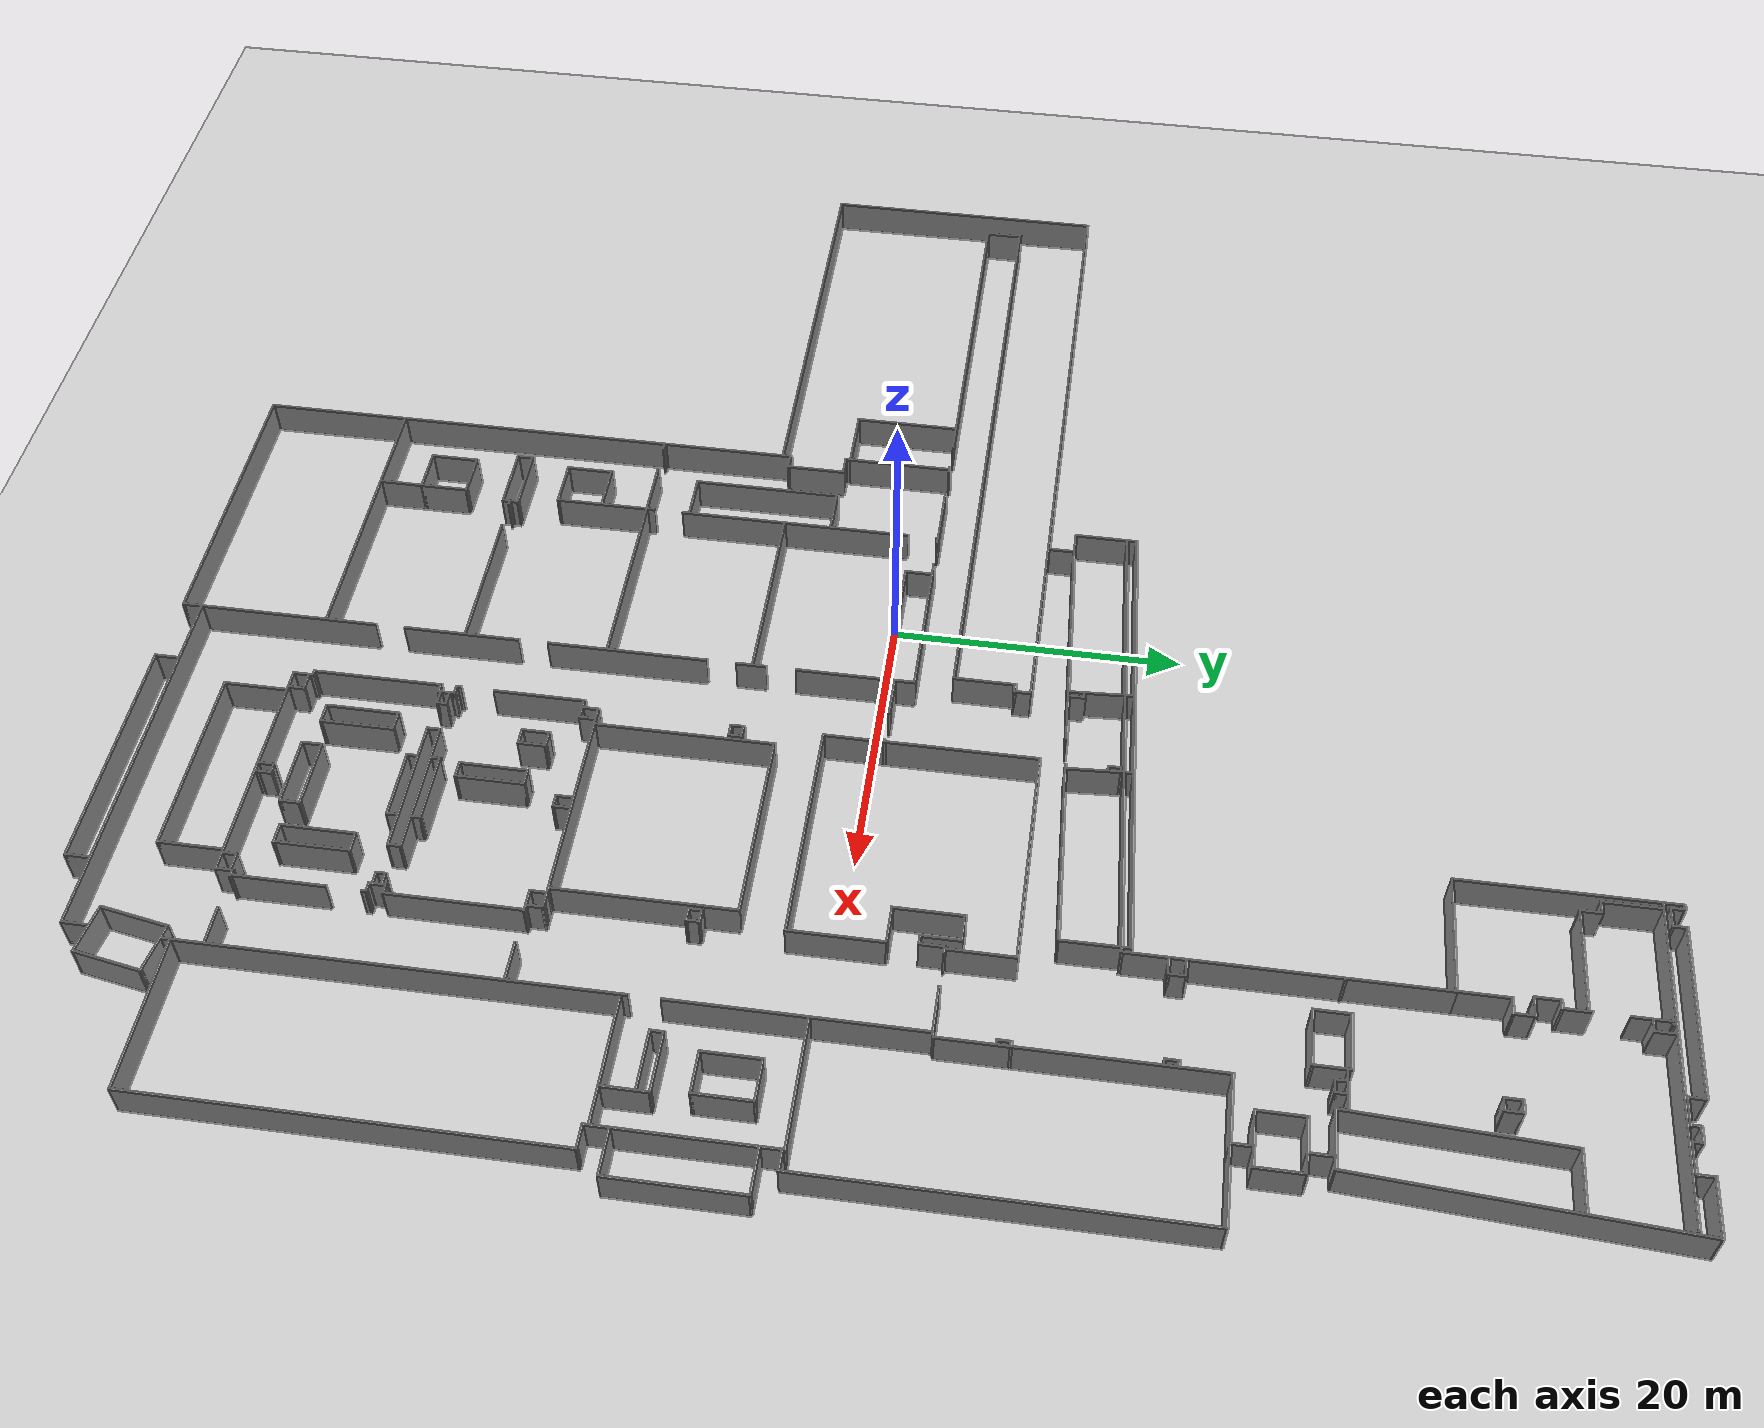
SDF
<sdf version="1.6">
 <world name="default">
  <light name="sun" type="directional">
   <pose>0 0 10 0 -0 0</pose>
   <diffuse>0.8 0.8 0.8 1</diffuse>
   <specular>0.2 0.2 0.2 1</specular>
   <attenuation>
    <range>1000</range>
    <constant>0.9</constant>
    <linear>0.01</linear>
    <quadratic>0.001</quadratic>
   </attenuation>
   <direction>-0.5 0.1 -0.9</direction>
  </light>
  <model name="ground_plane">
   <static>1</static>
   <link name="link">
    <collision name="collision">
     <geometry><plane><normal>0 0 1</normal><size>100 100</size></plane></geometry>
     <surface><friction><ode><mu>100</mu><mu2>50</mu2></ode></friction></surface>
    </collision>
    <visual name="visual">
     <cast_shadows>0</cast_shadows>
     <geometry><plane><normal>0 0 1</normal><size>100 100</size></plane></geometry>
     <material>
      <script><uri>file://media/materials/scripts/gazebo.material</uri><name>Gazebo/Grey</name></script>
     </material>
    </visual>
   </link>
  </model>
  <gravity>0 0 -9.8</gravity>
  <magnetic_field>6e-06 2.3e-05 -4.2e-05</magnetic_field>
  <atmosphere type="adiabatic"/>
  <physics name="default_physics" default="0" type="ode">
   <max_step_size>0.001</max_step_size>
   <real_time_factor>1</real_time_factor>
   <real_time_update_rate>1000</real_time_update_rate>
  </physics>
  <scene><ambient>0.4 0.4 0.4 1</ambient><background>0.7 0.7 0.7 1</background><shadows>1</shadows></scene>
  <spherical_coordinates>
   <surface_model>EARTH_WGS84</surface_model>
   <latitude_deg>0</latitude_deg>
   <longitude_deg>0</longitude_deg>
   <elevation>0</elevation>
   <heading_deg>0</heading_deg>
  </spherical_coordinates>
  <model name="SEH_v11">
   <pose>0.537033 1.18809 0 0 -0 0</pose>
   <link name="Wall_1">
    <collision name="Wall_1_Collision">
     <geometry><box><size>39.75 0.15 2.5</size></box></geometry>
     <pose>0 0 1.25 0 -0 0</pose>
    </collision>
    <visual name="Wall_1_Visual">
     <pose>0 0 1.25 0 -0 0</pose>
     <geometry><box><size>39.75 0.15 2.5</size></box></geometry>
     <material>
      <script><uri>file://media/materials/scripts/gazebo.material</uri><name>Gazebo/Grey</name></script>
      <ambient>1 1 1 1</ambient>
     </material>
     <meta><layer>0</layer></meta>
    </visual>
    <pose>-14.7042 -30.8362 0 0 0 -1.5708</pose>
   </link>
   <link name="Wall_101">
    <pose>8.32083 -0.436183 0 0 -0 0</pose>
    <visual name="Wall_101_Visual_0">
     <pose>-1.24875 0 1.25 0 -0 0</pose>
     <geometry><box><size>3.0025 0.15 2.5</size></box></geometry>
     <material>
      <script><uri>file://media/materials/scripts/gazebo.material</uri><name>Gazebo/Grey</name></script>
      <ambient>1 1 1 1</ambient>
     </material>
     <meta><layer>0</layer></meta>
    </visual>
    <collision name="Wall_101_Collision_0">
     <geometry><box><size>3.0025 0.15 2.5</size></box></geometry>
     <pose>-1.24875 0 1.25 0 -0 0</pose>
    </collision>
    <visual name="Wall_101_Visual_1">
     <pose>2.61125 0 1.25 0 -0 0</pose>
     <geometry><box><size>0.277496 0.15 2.5</size></box></geometry>
     <material>
      <script><uri>file://media/materials/scripts/gazebo.material</uri><name>Gazebo/Grey</name></script>
      <ambient>1 1 1 1</ambient>
     </material>
     <meta><layer>0</layer></meta>
    </visual>
    <collision name="Wall_101_Collision_1">
     <geometry><box><size>0.277496 0.15 2.5</size></box></geometry>
     <pose>2.61125 0 1.25 0 -0 0</pose>
    </collision>
   </link>
   <link name="Wall_102">
    <collision name="Wall_102_Collision">
     <geometry><box><size>4.25 0.15 2.5</size></box></geometry>
     <pose>0 0 1.25 0 -0 0</pose>
    </collision>
    <visual name="Wall_102_Visual">
     <pose>0 0 1.25 0 -0 0</pose>
     <geometry><box><size>4.25 0.15 2.5</size></box></geometry>
     <material>
      <script><uri>file://media/materials/scripts/gazebo.material</uri><name>Gazebo/Grey</name></script>
      <ambient>1 1 1 1</ambient>
     </material>
     <meta><layer>0</layer></meta>
    </visual>
    <pose>10.9958 -2.48618 0 0 0 -1.5708</pose>
   </link>
   <link name="Wall_103">
    <collision name="Wall_103_Collision">
     <geometry><box><size>15.75 0.15 2.5</size></box></geometry>
     <pose>0 0 1.25 0 -0 0</pose>
    </collision>
    <visual name="Wall_103_Visual">
     <pose>0 0 1.25 0 -0 0</pose>
     <geometry><box><size>15.75 0.15 2.5</size></box></geometry>
     <material>
      <script><uri>file://media/materials/scripts/gazebo.material</uri><name>Gazebo/Grey</name></script>
      <ambient>1 1 1 1</ambient>
     </material>
     <meta><layer>0</layer></meta>
    </visual>
    <pose>18.7958 -4.53618 0 0 -0 0</pose>
   </link>
   <link name="Wall_104">
    <collision name="Wall_104_Collision">
     <geometry><box><size>6.5 0.15 2.5</size></box></geometry>
     <pose>0 0 1.25 0 -0 0</pose>
    </collision>
    <visual name="Wall_104_Visual">
     <pose>0 0 1.25 0 -0 0</pose>
     <geometry><box><size>6.5 0.15 2.5</size></box></geometry>
     <material>
      <script><uri>file://media/materials/scripts/gazebo.material</uri><name>Gazebo/Grey</name></script>
      <ambient>1 1 1 1</ambient>
     </material>
     <meta><layer>0</layer></meta>
    </visual>
    <pose>26.5958 -1.36118 0 0 -0 1.5708</pose>
   </link>
   <link name="Wall_105">
    <collision name="Wall_105_Collision">
     <geometry><box><size>2.75 0.15 2.5</size></box></geometry>
     <pose>0 0 1.25 0 -0 0</pose>
    </collision>
    <visual name="Wall_105_Visual">
     <pose>0 0 1.25 0 -0 0</pose>
     <geometry><box><size>2.75 0.15 2.5</size></box></geometry>
     <material>
      <script><uri>file://media/materials/scripts/gazebo.material</uri><name>Gazebo/Grey</name></script>
      <ambient>1 1 1 1</ambient>
     </material>
     <meta><layer>0</layer></meta>
    </visual>
    <pose>25.2958 1.81382 0 0 -0 3.14159</pose>
   </link>
   <link name="Wall_106">
    <collision name="Wall_106_Collision">
     <geometry><box><size>4.75 0.15 2.5</size></box></geometry>
     <pose>0 0 1.25 0 -0 0</pose>
    </collision>
    <visual name="Wall_106_Visual">
     <pose>0 0 1.25 0 -0 0</pose>
     <geometry><box><size>4.75 0.15 2.5</size></box></geometry>
     <material>
      <script><uri>file://media/materials/scripts/gazebo.material</uri><name>Gazebo/Grey</name></script>
      <ambient>1 1 1 1</ambient>
     </material>
     <meta><layer>0</layer></meta>
    </visual>
    <pose>23.9958 4.11382 0 0 -0 1.5708</pose>
   </link>
   <link name="Wall_107">
    <collision name="Wall_107_Collision">
     <geometry><box><size>2 0.15 2.5</size></box></geometry>
     <pose>0 0 1.25 0 -0 0</pose>
    </collision>
    <visual name="Wall_107_Visual">
     <pose>0 0 1.25 0 -0 0</pose>
     <geometry><box><size>2 0.15 2.5</size></box></geometry>
     <material>
      <script><uri>file://media/materials/scripts/gazebo.material</uri><name>Gazebo/Grey</name></script>
      <ambient>1 1 1 1</ambient>
     </material>
     <meta><layer>0</layer></meta>
    </visual>
    <pose>24.9208 6.41382 0 0 -0 0</pose>
   </link>
   <link name="Wall_108">
    <collision name="Wall_108_Collision">
     <geometry><box><size>2.75 0.15 2.5</size></box></geometry>
     <pose>0 0 1.25 0 -0 0</pose>
    </collision>
    <visual name="Wall_108_Visual">
     <pose>0 0 1.25 0 -0 0</pose>
     <geometry><box><size>2.75 0.15 2.5</size></box></geometry>
     <material>
      <script><uri>file://media/materials/scripts/gazebo.material</uri><name>Gazebo/Grey</name></script>
      <ambient>1 1 1 1</ambient>
     </material>
     <meta><layer>0</layer></meta>
    </visual>
    <pose>25.8458 5.11382 0 0 0 -1.5708</pose>
   </link>
   <link name="Wall_111">
    <collision name="Wall_111_Collision">
     <geometry><box><size>0.75 0.15 2.5</size></box></geometry>
     <pose>0 0 1.25 0 -0 0</pose>
    </collision>
    <visual name="Wall_111_Visual">
     <pose>0 0 1.25 0 -0 0</pose>
     <geometry><box><size>0.75 0.15 2.5</size></box></geometry>
     <material>
      <script><uri>file://media/materials/scripts/gazebo.material</uri><name>Gazebo/Grey</name></script>
      <ambient>1 1 1 1</ambient>
     </material>
     <meta><layer>0</layer></meta>
    </visual>
    <pose>26.1458 3.81382 0 0 -0 0</pose>
   </link>
   <link name="Wall_112">
    <collision name="Wall_112_Collision">
     <geometry><box><size>1.75 0.15 2.5</size></box></geometry>
     <pose>0 0 1.25 0 -0 0</pose>
    </collision>
    <visual name="Wall_112_Visual">
     <pose>0 0 1.25 0 -0 0</pose>
     <geometry><box><size>1.75 0.15 2.5</size></box></geometry>
     <material>
      <script><uri>file://media/materials/scripts/gazebo.material</uri><name>Gazebo/Grey</name></script>
      <ambient>1 1 1 1</ambient>
     </material>
     <meta><layer>0</layer></meta>
    </visual>
    <pose>26.4458 4.61382 0 0 -0 1.5708</pose>
   </link>
   <link name="Wall_113">
    <pose>29.4958 5.41382 0 0 -0 0</pose>
    <visual name="Wall_113_Visual_0">
     <pose>-2.84048 0 1.25 0 -0 0</pose>
     <geometry><box><size>0.569046 0.15 2.5</size></box></geometry>
     <material>
      <script><uri>file://media/materials/scripts/gazebo.material</uri><name>Gazebo/Grey</name></script>
      <ambient>1 1 1 1</ambient>
     </material>
     <meta><layer>0</layer></meta>
    </visual>
    <collision name="Wall_113_Collision_0">
     <geometry><box><size>0.569046 0.15 2.5</size></box></geometry>
     <pose>-2.84048 0 1.25 0 -0 0</pose>
    </collision>
    <visual name="Wall_113_Visual_1">
     <pose>1.45452 0 1.25 0 -0 0</pose>
     <geometry><box><size>3.34095 0.15 2.5</size></box></geometry>
     <material>
      <script><uri>file://media/materials/scripts/gazebo.material</uri><name>Gazebo/Grey</name></script>
      <ambient>1 1 1 1</ambient>
     </material>
     <meta><layer>0</layer></meta>
    </visual>
    <collision name="Wall_113_Collision_1">
     <geometry><box><size>3.34095 0.15 2.5</size></box></geometry>
     <pose>1.45452 0 1.25 0 -0 0</pose>
    </collision>
   </link>
   <link name="Wall_114">
    <pose>32.5458 -18.3862 0 0 0 -1.5708</pose>
    <visual name="Wall_114_Visual_0">
     <pose>-15.5143 0 1.25 0 -0 0</pose>
     <geometry><box><size>16.7215 0.15 2.5</size></box></geometry>
     <material>
      <script><uri>file://media/materials/scripts/gazebo.material</uri><name>Gazebo/Grey</name></script>
      <ambient>1 1 1 1</ambient>
     </material>
     <meta><layer>0</layer></meta>
    </visual>
    <collision name="Wall_114_Collision_0">
     <geometry><box><size>16.7215 0.15 2.5</size></box></geometry>
     <pose>-15.5143 0 1.25 0 -0 0</pose>
    </collision>
    <visual name="Wall_114_Visual_1">
     <pose>9.36074 0 1.25 0 -0 0</pose>
     <geometry><box><size>29.0285 0.15 2.5</size></box></geometry>
     <material>
      <script><uri>file://media/materials/scripts/gazebo.material</uri><name>Gazebo/Grey</name></script>
      <ambient>1 1 1 1</ambient>
     </material>
     <meta><layer>0</layer></meta>
    </visual>
    <collision name="Wall_114_Collision_1">
     <geometry><box><size>29.0285 0.15 2.5</size></box></geometry>
     <pose>9.36074 0 1.25 0 -0 0</pose>
    </collision>
   </link>
   <link name="Wall_116">
    <collision name="Wall_116_Collision">
     <geometry><box><size>16 0.15 2.5</size></box></geometry>
     <pose>0 0 1.25 0 -0 0</pose>
    </collision>
    <visual name="Wall_116_Visual">
     <pose>0 0 1.25 0 -0 0</pose>
     <geometry><box><size>16 0.15 2.5</size></box></geometry>
     <material>
      <script><uri>file://media/materials/scripts/gazebo.material</uri><name>Gazebo/Grey</name></script>
      <ambient>1 1 1 1</ambient>
     </material>
     <meta><layer>0</layer></meta>
    </visual>
    <pose>18.846 -19.8363 0 0 -0 3.14159</pose>
   </link>
   <link name="Wall_117">
    <collision name="Wall_117_Collision">
     <geometry><box><size>1.25 0.15 2.5</size></box></geometry>
     <pose>0 0 1.25 0 -0 0</pose>
    </collision>
    <visual name="Wall_117_Visual">
     <pose>0 0 1.25 0 -0 0</pose>
     <geometry><box><size>1.25 0.15 2.5</size></box></geometry>
     <material>
      <script><uri>file://media/materials/scripts/gazebo.material</uri><name>Gazebo/Grey</name></script>
      <ambient>1 1 1 1</ambient>
     </material>
     <meta><layer>0</layer></meta>
    </visual>
    <pose>10.921 -20.3863 0 0 0 -1.5708</pose>
   </link>
   <link name="Wall_119">
    <collision name="Wall_119_Collision">
     <geometry><box><size>0.75 0.15 2.5</size></box></geometry>
     <pose>0 0 1.25 0 -0 0</pose>
    </collision>
    <visual name="Wall_119_Visual">
     <pose>0 0 1.25 0 -0 0</pose>
     <geometry><box><size>0.75 0.15 2.5</size></box></geometry>
     <material>
      <script><uri>file://media/materials/scripts/gazebo.material</uri><name>Gazebo/Grey</name></script>
      <ambient>1 1 1 1</ambient>
     </material>
     <meta><layer>0</layer></meta>
    </visual>
    <pose>10.621 -20.9363 0 0 -0 3.14159</pose>
   </link>
   <link name="Wall_120">
    <pose>10.321 -25.3613 0 0 0 -1.5708</pose>
    <visual name="Wall_120_Visual_0">
     <pose>-1.31579 0 1.25 0 -0 0</pose>
     <geometry><box><size>6.36842 0.15 2.5</size></box></geometry>
     <material>
      <script><uri>file://media/materials/scripts/gazebo.material</uri><name>Gazebo/Grey</name></script>
      <ambient>1 1 1 1</ambient>
     </material>
     <meta><layer>0</layer></meta>
    </visual>
    <collision name="Wall_120_Collision_0">
     <geometry><box><size>6.36842 0.15 2.5</size></box></geometry>
     <pose>-1.31579 0 1.25 0 -0 0</pose>
    </collision>
    <visual name="Wall_120_Visual_1">
     <pose>4.29921 0 1.25 0 -0 0</pose>
     <geometry><box><size>0.401581 0.15 2.5</size></box></geometry>
     <material>
      <script><uri>file://media/materials/scripts/gazebo.material</uri><name>Gazebo/Grey</name></script>
      <ambient>1 1 1 1</ambient>
     </material>
     <meta><layer>0</layer></meta>
    </visual>
    <collision name="Wall_120_Collision_1">
     <geometry><box><size>0.401581 0.15 2.5</size></box></geometry>
     <pose>4.29921 0 1.25 0 -0 0</pose>
    </collision>
   </link>
   <link name="Wall_121">
    <collision name="Wall_121_Collision">
     <geometry><box><size>0.75 0.15 2.5</size></box></geometry>
     <pose>0 0 1.25 0 -0 0</pose>
    </collision>
    <visual name="Wall_121_Visual">
     <pose>0 0 1.25 0 -0 0</pose>
     <geometry><box><size>0.75 0.15 2.5</size></box></geometry>
     <material>
      <script><uri>file://media/materials/scripts/gazebo.material</uri><name>Gazebo/Grey</name></script>
      <ambient>1 1 1 1</ambient>
     </material>
     <meta><layer>0</layer></meta>
    </visual>
    <pose>10.621 -29.7863 0 0 -0 0</pose>
   </link>
   <link name="Wall_122">
    <collision name="Wall_122_Collision">
     <geometry><box><size>1.25 0.15 2.5</size></box></geometry>
     <pose>0 0 1.25 0 -0 0</pose>
    </collision>
    <visual name="Wall_122_Visual">
     <pose>0 0 1.25 0 -0 0</pose>
     <geometry><box><size>1.25 0.15 2.5</size></box></geometry>
     <material>
      <script><uri>file://media/materials/scripts/gazebo.material</uri><name>Gazebo/Grey</name></script>
      <ambient>1 1 1 1</ambient>
     </material>
     <meta><layer>0</layer></meta>
    </visual>
    <pose>10.921 -30.3363 0 0 0 -1.5708</pose>
   </link>
   <link name="Wall_123">
    <collision name="Wall_123_Collision">
     <geometry><box><size>0.75 0.15 2.5</size></box></geometry>
     <pose>0 0 1.25 0 -0 0</pose>
    </collision>
    <visual name="Wall_123_Visual">
     <pose>0 0 1.25 0 -0 0</pose>
     <geometry><box><size>0.75 0.15 2.5</size></box></geometry>
     <material>
      <script><uri>file://media/materials/scripts/gazebo.material</uri><name>Gazebo/Grey</name></script>
      <ambient>1 1 1 1</ambient>
     </material>
     <meta><layer>0</layer></meta>
    </visual>
    <pose>10.621 -30.8863 0 0 -0 3.14159</pose>
   </link>
   <link name="Wall_124">
    <collision name="Wall_124_Collision">
     <geometry><box><size>9 0.15 2.5</size></box></geometry>
     <pose>0 0 1.25 0 -0 0</pose>
    </collision>
    <visual name="Wall_124_Visual">
     <pose>0 0 1.25 0 -0 0</pose>
     <geometry><box><size>9 0.15 2.5</size></box></geometry>
     <material>
      <script><uri>file://media/materials/scripts/gazebo.material</uri><name>Gazebo/Grey</name></script>
      <ambient>1 1 1 1</ambient>
     </material>
     <meta><layer>0</layer></meta>
    </visual>
    <pose>10.321 -35.3113 0 0 0 -1.5708</pose>
   </link>
   <link name="Wall_125">
    <collision name="Wall_125_Collision">
     <geometry><box><size>0.5 0.15 2.5</size></box></geometry>
     <pose>0 0 1.25 0 -0 0</pose>
    </collision>
    <visual name="Wall_125_Visual">
     <pose>0 0 1.25 0 -0 0</pose>
     <geometry><box><size>0.5 0.15 2.5</size></box></geometry>
     <material>
      <script><uri>file://media/materials/scripts/gazebo.material</uri><name>Gazebo/Grey</name></script>
      <ambient>1 1 1 1</ambient>
     </material>
     <meta><layer>0</layer></meta>
    </visual>
    <pose>10.496 -39.7363 0 0 -0 0</pose>
   </link>
   <link name="Wall_126">
    <collision name="Wall_126_Collision">
     <geometry><box><size>1.5 0.15 2.5</size></box></geometry>
     <pose>0 0 1.25 0 -0 0</pose>
    </collision>
    <visual name="Wall_126_Visual">
     <pose>0 0 1.25 0 -0 0</pose>
     <geometry><box><size>1.5 0.15 2.5</size></box></geometry>
     <material>
      <script><uri>file://media/materials/scripts/gazebo.material</uri><name>Gazebo/Grey</name></script>
      <ambient>1 1 1 1</ambient>
     </material>
     <meta><layer>0</layer></meta>
    </visual>
    <pose>10.671 -40.4113 0 0 0 -1.5708</pose>
   </link>
   <link name="Wall_127">
    <collision name="Wall_127_Collision">
     <geometry><box><size>16.5 0.15 2.5</size></box></geometry>
     <pose>0 0 1.25 0 -0 0</pose>
    </collision>
    <visual name="Wall_127_Visual">
     <pose>0 0 1.25 0 -0 0</pose>
     <geometry><box><size>16.5 0.15 2.5</size></box></geometry>
     <material>
      <script><uri>file://media/materials/scripts/gazebo.material</uri><name>Gazebo/Grey</name></script>
      <ambient>1 1 1 1</ambient>
     </material>
     <meta><layer>0</layer></meta>
    </visual>
    <pose>18.846 -41.0863 0 0 -0 0</pose>
   </link>
   <link name="Wall_128">
    <collision name="Wall_128_Collision">
     <geometry><box><size>1.25 0.15 2.5</size></box></geometry>
     <pose>0 0 1.25 0 -0 0</pose>
    </collision>
    <visual name="Wall_128_Visual">
     <pose>0 0 1.25 0 -0 0</pose>
     <geometry><box><size>1.25 0.15 2.5</size></box></geometry>
     <material>
      <script><uri>file://media/materials/scripts/gazebo.material</uri><name>Gazebo/Grey</name></script>
      <ambient>1 1 1 1</ambient>
     </material>
     <meta><layer>0</layer></meta>
    </visual>
    <pose>27.021 -40.5363 0 0 -0 1.5708</pose>
   </link>
   <link name="Wall_131">
    <collision name="Wall_131_Collision">
     <geometry><box><size>0.5 0.15 2.5</size></box></geometry>
     <pose>0 0 1.25 0 -0 0</pose>
    </collision>
    <visual name="Wall_131_Visual">
     <pose>0 0 1.25 0 -0 0</pose>
     <geometry><box><size>0.5 0.15 2.5</size></box></geometry>
     <material>
      <script><uri>file://media/materials/scripts/gazebo.material</uri><name>Gazebo/Grey</name></script>
      <ambient>1 1 1 1</ambient>
     </material>
     <meta><layer>0</layer></meta>
    </visual>
    <pose>27.196 -39.9863 0 0 -0 0</pose>
   </link>
   <link name="Wall_132">
    <pose>27.371 -35.5613 0 0 -0 1.5708</pose>
    <visual name="Wall_132_Visual_0">
     <pose>-1.34301 0 1.25 0 -0 0</pose>
     <geometry><box><size>6.31398 0.15 2.5</size></box></geometry>
     <material>
      <script><uri>file://media/materials/scripts/gazebo.material</uri><name>Gazebo/Grey</name></script>
      <ambient>1 1 1 1</ambient>
     </material>
     <meta><layer>0</layer></meta>
    </visual>
    <collision name="Wall_132_Collision_0">
     <geometry><box><size>6.31398 0.15 2.5</size></box></geometry>
     <pose>-1.34301 0 1.25 0 -0 0</pose>
    </collision>
    <visual name="Wall_132_Visual_1">
     <pose>4.28349 0 1.25 0 -0 0</pose>
     <geometry><box><size>0.433021 0.15 2.5</size></box></geometry>
     <material>
      <script><uri>file://media/materials/scripts/gazebo.material</uri><name>Gazebo/Grey</name></script>
      <ambient>1 1 1 1</ambient>
     </material>
     <meta><layer>0</layer></meta>
    </visual>
    <collision name="Wall_132_Collision_1">
     <geometry><box><size>0.433021 0.15 2.5</size></box></geometry>
     <pose>4.28349 0 1.25 0 -0 0</pose>
    </collision>
   </link>
   <link name="Wall_133">
    <collision name="Wall_133_Collision">
     <geometry><box><size>0.75 0.15 2.5</size></box></geometry>
     <pose>0 0 1.25 0 -0 0</pose>
    </collision>
    <visual name="Wall_133_Visual">
     <pose>0 0 1.25 0 -0 0</pose>
     <geometry><box><size>0.75 0.15 2.5</size></box></geometry>
     <material>
      <script><uri>file://media/materials/scripts/gazebo.material</uri><name>Gazebo/Grey</name></script>
      <ambient>1 1 1 1</ambient>
     </material>
     <meta><layer>0</layer></meta>
    </visual>
    <pose>27.071 -31.1363 0 0 -0 3.14159</pose>
   </link>
   <link name="Wall_134">
    <collision name="Wall_134_Collision">
     <geometry><box><size>1.25 0.15 2.5</size></box></geometry>
     <pose>0 0 1.25 0 -0 0</pose>
    </collision>
    <visual name="Wall_134_Visual">
     <pose>0 0 1.25 0 -0 0</pose>
     <geometry><box><size>1.25 0.15 2.5</size></box></geometry>
     <material>
      <script><uri>file://media/materials/scripts/gazebo.material</uri><name>Gazebo/Grey</name></script>
      <ambient>1 1 1 1</ambient>
     </material>
     <meta><layer>0</layer></meta>
    </visual>
    <pose>26.771 -30.5863 0 0 -0 1.5708</pose>
   </link>
   <link name="Wall_135">
    <collision name="Wall_135_Collision">
     <geometry><box><size>0.75 0.15 2.5</size></box></geometry>
     <pose>0 0 1.25 0 -0 0</pose>
    </collision>
    <visual name="Wall_135_Visual">
     <pose>0 0 1.25 0 -0 0</pose>
     <geometry><box><size>0.75 0.15 2.5</size></box></geometry>
     <material>
      <script><uri>file://media/materials/scripts/gazebo.material</uri><name>Gazebo/Grey</name></script>
      <ambient>1 1 1 1</ambient>
     </material>
     <meta><layer>0</layer></meta>
    </visual>
    <pose>27.071 -30.0362 0 0 -0 0.000333</pose>
   </link>
   <link name="Wall_147">
    <pose>29.921 -39.9863 0 0 -0 0</pose>
    <visual name="Wall_147_Visual_0">
     <pose>-2.49623 0 1.25 0 -0 0</pose>
     <geometry><box><size>0.257534 0.15 2.5</size></box></geometry>
     <material>
      <script><uri>file://media/materials/scripts/gazebo.material</uri><name>Gazebo/Grey</name></script>
      <ambient>1 1 1 1</ambient>
     </material>
     <meta><layer>0</layer></meta>
    </visual>
    <collision name="Wall_147_Collision_0">
     <geometry><box><size>0.257534 0.15 2.5</size></box></geometry>
     <pose>-2.49623 0 1.25 0 -0 0</pose>
    </collision>
    <visual name="Wall_147_Visual_1">
     <pose>1.27377 0 1.25 0 -0 0</pose>
     <geometry><box><size>2.70247 0.15 2.5</size></box></geometry>
     <material>
      <script><uri>file://media/materials/scripts/gazebo.material</uri><name>Gazebo/Grey</name></script>
      <ambient>1 1 1 1</ambient>
     </material>
     <meta><layer>0</layer></meta>
    </visual>
    <collision name="Wall_147_Collision_1">
     <geometry><box><size>2.70247 0.15 2.5</size></box></geometry>
     <pose>1.27377 0 1.25 0 -0 0</pose>
    </collision>
   </link>
   <link name="Wall_149">
    <collision name="Wall_149_Collision">
     <geometry><box><size>9.75 0.15 2.5</size></box></geometry>
     <pose>0 0 1.25 0 -0 0</pose>
    </collision>
    <visual name="Wall_149_Visual">
     <pose>0 0 1.25 0 -0 0</pose>
     <geometry><box><size>9.75 0.15 2.5</size></box></geometry>
     <material>
      <script><uri>file://media/materials/scripts/gazebo.material</uri><name>Gazebo/Grey</name></script>
      <ambient>1 1 1 1</ambient>
     </material>
     <meta><layer>0</layer></meta>
    </visual>
    <pose>18.8923 -29.9408 0 0 -0 0</pose>
   </link>
   <link name="Wall_150">
    <collision name="Wall_150_Collision">
     <geometry><box><size>1 0.15 2.5</size></box></geometry>
     <pose>0 0 1.25 0 -0 0</pose>
    </collision>
    <visual name="Wall_150_Visual">
     <pose>0 0 1.25 0 -0 0</pose>
     <geometry><box><size>1 0.15 2.5</size></box></geometry>
     <material>
      <script><uri>file://media/materials/scripts/gazebo.material</uri><name>Gazebo/Grey</name></script>
      <ambient>1 1 1 1</ambient>
     </material>
     <meta><layer>0</layer></meta>
    </visual>
    <pose>23.6923 -30.3658 0 0 0 -1.5708</pose>
   </link>
   <link name="Wall_151">
    <collision name="Wall_151_Collision">
     <geometry><box><size>9.75 0.15 2.5</size></box></geometry>
     <pose>0 0 1.25 0 -0 0</pose>
    </collision>
    <visual name="Wall_151_Visual">
     <pose>0 0 1.25 0 -0 0</pose>
     <geometry><box><size>9.75 0.15 2.5</size></box></geometry>
     <material>
      <script><uri>file://media/materials/scripts/gazebo.material</uri><name>Gazebo/Grey</name></script>
      <ambient>1 1 1 1</ambient>
     </material>
     <meta><layer>0</layer></meta>
    </visual>
    <pose>18.8923 -30.7908 0 0 -0 3.14159</pose>
   </link>
   <link name="Wall_152">
    <collision name="Wall_152_Collision">
     <geometry><box><size>1 0.15 2.5</size></box></geometry>
     <pose>0 0 1.25 0 -0 0</pose>
    </collision>
    <visual name="Wall_152_Visual">
     <pose>0 0 1.25 0 -0 0</pose>
     <geometry><box><size>1 0.15 2.5</size></box></geometry>
     <material>
      <script><uri>file://media/materials/scripts/gazebo.material</uri><name>Gazebo/Grey</name></script>
      <ambient>1 1 1 1</ambient>
     </material>
     <meta><layer>0</layer></meta>
    </visual>
    <pose>14.0923 -30.3658 0 0 -0 1.5708</pose>
   </link>
   <link name="Wall_154">
    <collision name="Wall_154_Collision">
     <geometry><box><size>0.75 0.15 2.5</size></box></geometry>
     <pose>0 0 1.25 0 -0 0</pose>
    </collision>
    <visual name="Wall_154_Visual">
     <pose>0 0 1.25 0 -0 0</pose>
     <geometry><box><size>0.75 0.15 2.5</size></box></geometry>
     <material>
      <script><uri>file://media/materials/scripts/gazebo.material</uri><name>Gazebo/Grey</name></script>
      <ambient>1 1 1 1</ambient>
     </material>
     <meta><layer>0</layer></meta>
    </visual>
    <pose>16.4749 -29.6084 0 0 -0 1.5708</pose>
   </link>
   <link name="Wall_155">
    <collision name="Wall_155_Collision">
     <geometry><box><size>5 0.15 2.5</size></box></geometry>
     <pose>0 0 1.25 0 -0 0</pose>
    </collision>
    <visual name="Wall_155_Visual">
     <pose>0 0 1.25 0 -0 0</pose>
     <geometry><box><size>5 0.15 2.5</size></box></geometry>
     <material>
      <script><uri>file://media/materials/scripts/gazebo.material</uri><name>Gazebo/Grey</name></script>
      <ambient>1 1 1 1</ambient>
     </material>
     <meta><layer>0</layer></meta>
    </visual>
    <pose>18.8999 -29.3084 0 0 -0 0</pose>
   </link>
   <link name="Wall_156">
    <collision name="Wall_156_Collision">
     <geometry><box><size>0.75 0.15 2.5</size></box></geometry>
     <pose>0 0 1.25 0 -0 0</pose>
    </collision>
    <visual name="Wall_156_Visual">
     <pose>0 0 1.25 0 -0 0</pose>
     <geometry><box><size>0.75 0.15 2.5</size></box></geometry>
     <material>
      <script><uri>file://media/materials/scripts/gazebo.material</uri><name>Gazebo/Grey</name></script>
      <ambient>1 1 1 1</ambient>
     </material>
     <meta><layer>0</layer></meta>
    </visual>
    <pose>21.3249 -29.6084 0 0 0 -1.5708</pose>
   </link>
   <link name="Wall_158">
    <collision name="Wall_158_Collision">
     <geometry><box><size>0.75 0.15 2.5</size></box></geometry>
     <pose>0 0 1.25 0 -0 0</pose>
    </collision>
    <visual name="Wall_158_Visual">
     <pose>0 0 1.25 0 -0 0</pose>
     <geometry><box><size>0.75 0.15 2.5</size></box></geometry>
     <material>
      <script><uri>file://media/materials/scripts/gazebo.material</uri><name>Gazebo/Grey</name></script>
      <ambient>1 1 1 1</ambient>
     </material>
     <meta><layer>0</layer></meta>
    </visual>
    <pose>16.4587 -31.2295 0 0 0 -1.5708</pose>
   </link>
   <link name="Wall_163">
    <collision name="Wall_163_Collision">
     <geometry><box><size>5 0.15 2.5</size></box></geometry>
     <pose>0 0 1.25 0 -0 0</pose>
    </collision>
    <visual name="Wall_163_Visual">
     <pose>0 0 1.25 0 -0 0</pose>
     <geometry><box><size>5 0.15 2.5</size></box></geometry>
     <material>
      <script><uri>file://media/materials/scripts/gazebo.material</uri><name>Gazebo/Grey</name></script>
      <ambient>1 1 1 1</ambient>
     </material>
     <meta><layer>0</layer></meta>
    </visual>
    <pose>18.8837 -31.5295 0 0 -0 0</pose>
   </link>
   <link name="Wall_164">
    <collision name="Wall_164_Collision">
     <geometry><box><size>0.75 0.15 2.5</size></box></geometry>
     <pose>0 0 1.25 0 -0 0</pose>
    </collision>
    <visual name="Wall_164_Visual">
     <pose>0 0 1.25 0 -0 0</pose>
     <geometry><box><size>0.75 0.15 2.5</size></box></geometry>
     <material>
      <script><uri>file://media/materials/scripts/gazebo.material</uri><name>Gazebo/Grey</name></script>
      <ambient>1 1 1 1</ambient>
     </material>
     <meta><layer>0</layer></meta>
    </visual>
    <pose>21.3087 -31.2295 0 0 -0 1.5708</pose>
   </link>
   <link name="Wall_166">
    <collision name="Wall_166_Collision">
     <geometry><box><size>12.25 0.15 2.5</size></box></geometry>
     <pose>0 0 1.25 0 -0 0</pose>
    </collision>
    <visual name="Wall_166_Visual">
     <pose>0 0 1.25 0 -0 0</pose>
     <geometry><box><size>12.25 0.15 2.5</size></box></geometry>
     <material>
      <script><uri>file://media/materials/scripts/gazebo.material</uri><name>Gazebo/Grey</name></script>
      <ambient>1 1 1 1</ambient>
     </material>
     <meta><layer>0</layer></meta>
    </visual>
    <pose>12.1961 -13.6978 0 0 -0 1.5708</pose>
   </link>
   <link name="Wall_167">
    <collision name="Wall_167_Collision">
     <geometry><box><size>13.5 0.15 2.5</size></box></geometry>
     <pose>0 0 1.25 0 -0 0</pose>
    </collision>
    <visual name="Wall_167_Visual">
     <pose>0 0 1.25 0 -0 0</pose>
     <geometry><box><size>13.5 0.15 2.5</size></box></geometry>
     <material>
      <script><uri>file://media/materials/scripts/gazebo.material</uri><name>Gazebo/Grey</name></script>
      <ambient>1 1 1 1</ambient>
     </material>
     <meta><layer>0</layer></meta>
    </visual>
    <pose>18.8711 -7.64779 0 0 -0 0</pose>
   </link>
   <link name="Wall_168">
    <collision name="Wall_168_Collision">
     <geometry><box><size>12.25 0.15 2.5</size></box></geometry>
     <pose>0 0 1.25 0 -0 0</pose>
    </collision>
    <visual name="Wall_168_Visual">
     <pose>0 0 1.25 0 -0 0</pose>
     <geometry><box><size>12.25 0.15 2.5</size></box></geometry>
     <material>
      <script><uri>file://media/materials/scripts/gazebo.material</uri><name>Gazebo/Grey</name></script>
      <ambient>1 1 1 1</ambient>
     </material>
     <meta><layer>0</layer></meta>
    </visual>
    <pose>25.5461 -13.6978 0 0 0 -1.5708</pose>
   </link>
   <link name="Wall_17">
    <collision name="Wall_17_Collision">
     <geometry><box><size>4.84109 0.15 2.5</size></box></geometry>
     <pose>0 0 1.25 0 -0 0</pose>
    </collision>
    <visual name="Wall_17_Visual">
     <pose>0 0 1.25 0 -0 0</pose>
     <geometry><box><size>4.84109 0.15 2.5</size></box></geometry>
     <material>
      <script><uri>file://media/materials/scripts/gazebo.material</uri><name>Gazebo/Grey</name></script>
      <ambient>1 1 1 1</ambient>
     </material>
     <meta><layer>0</layer></meta>
    </visual>
    <pose>34.5912 -45.4997 0 0 -0 1.39856</pose>
   </link>
   <link name="Wall_170">
    <collision name="Wall_170_Collision">
     <geometry><box><size>1 0.15 2.5</size></box></geometry>
     <pose>0 0 1.25 0 -0 0</pose>
    </collision>
    <visual name="Wall_170_Visual">
     <pose>0 0 1.25 0 -0 0</pose>
     <geometry><box><size>1 0.15 2.5</size></box></geometry>
     <material>
      <script><uri>file://media/materials/scripts/gazebo.material</uri><name>Gazebo/Grey</name></script>
      <ambient>1 1 1 1</ambient>
     </material>
     <meta><layer>0</layer></meta>
    </visual>
    <pose>11.4592 -9.91088 0 0 -0 3.14159</pose>
   </link>
   <link name="Wall_171">
    <collision name="Wall_171_Collision">
     <geometry><box><size>1 0.15 2.5</size></box></geometry>
     <pose>0 0 1.25 0 -0 0</pose>
    </collision>
    <visual name="Wall_171_Visual">
     <pose>0 0 1.25 0 -0 0</pose>
     <geometry><box><size>1 0.15 2.5</size></box></geometry>
     <material>
      <script><uri>file://media/materials/scripts/gazebo.material</uri><name>Gazebo/Grey</name></script>
      <ambient>1 1 1 1</ambient>
     </material>
     <meta><layer>0</layer></meta>
    </visual>
    <pose>11.0342 -10.3359 0 0 0 -1.5708</pose>
   </link>
   <link name="Wall_172">
    <collision name="Wall_172_Collision">
     <geometry><box><size>1 0.15 2.5</size></box></geometry>
     <pose>0 0 1.25 0 -0 0</pose>
    </collision>
    <visual name="Wall_172_Visual">
     <pose>0 0 1.25 0 -0 0</pose>
     <geometry><box><size>1 0.15 2.5</size></box></geometry>
     <material>
      <script><uri>file://media/materials/scripts/gazebo.material</uri><name>Gazebo/Grey</name></script>
      <ambient>1 1 1 1</ambient>
     </material>
     <meta><layer>0</layer></meta>
    </visual>
    <pose>11.4592 -10.7609 0 0 -0 0</pose>
   </link>
   <link name="Wall_173">
    <collision name="Wall_173_Collision">
     <geometry><box><size>1 0.15 2.5</size></box></geometry>
     <pose>0 0 1.25 0 -0 0</pose>
    </collision>
    <visual name="Wall_173_Visual">
     <pose>0 0 1.25 0 -0 0</pose>
     <geometry><box><size>1 0.15 2.5</size></box></geometry>
     <material>
      <script><uri>file://media/materials/scripts/gazebo.material</uri><name>Gazebo/Grey</name></script>
      <ambient>1 1 1 1</ambient>
     </material>
     <meta><layer>0</layer></meta>
    </visual>
    <pose>11.8842 -10.3359 0 0 -0 1.5708</pose>
   </link>
   <link name="Wall_177">
    <collision name="Wall_177_Collision">
     <geometry><box><size>1 0.15 2.5</size></box></geometry>
     <pose>0 0 1.25 0 -0 0</pose>
    </collision>
    <visual name="Wall_177_Visual">
     <pose>0 0 1.25 0 -0 0</pose>
     <geometry><box><size>1 0.15 2.5</size></box></geometry>
     <material>
      <script><uri>file://media/materials/scripts/gazebo.material</uri><name>Gazebo/Grey</name></script>
      <ambient>1 1 1 1</ambient>
     </material>
     <meta><layer>0</layer></meta>
    </visual>
    <pose>25.8684 -10.3601 0 0 0 -1.5708</pose>
   </link>
   <link name="Wall_178">
    <collision name="Wall_178_Collision">
     <geometry><box><size>1 0.15 2.5</size></box></geometry>
     <pose>0 0 1.25 0 -0 0</pose>
    </collision>
    <visual name="Wall_178_Visual">
     <pose>0 0 1.25 0 -0 0</pose>
     <geometry><box><size>1 0.15 2.5</size></box></geometry>
     <material>
      <script><uri>file://media/materials/scripts/gazebo.material</uri><name>Gazebo/Grey</name></script>
      <ambient>1 1 1 1</ambient>
     </material>
     <meta><layer>0</layer></meta>
    </visual>
    <pose>26.2934 -10.7851 0 0 -0 0</pose>
   </link>
   <link name="Wall_179">
    <collision name="Wall_179_Collision">
     <geometry><box><size>1 0.15 2.5</size></box></geometry>
     <pose>0 0 1.25 0 -0 0</pose>
    </collision>
    <visual name="Wall_179_Visual">
     <pose>0 0 1.25 0 -0 0</pose>
     <geometry><box><size>1 0.15 2.5</size></box></geometry>
     <material>
      <script><uri>file://media/materials/scripts/gazebo.material</uri><name>Gazebo/Grey</name></script>
      <ambient>1 1 1 1</ambient>
     </material>
     <meta><layer>0</layer></meta>
    </visual>
    <pose>26.7184 -10.3601 0 0 -0 1.5708</pose>
   </link>
   <link name="Wall_180">
    <collision name="Wall_180_Collision">
     <geometry><box><size>1 0.15 2.5</size></box></geometry>
     <pose>0 0 1.25 0 -0 0</pose>
    </collision>
    <visual name="Wall_180_Visual">
     <pose>0 0 1.25 0 -0 0</pose>
     <geometry><box><size>1 0.15 2.5</size></box></geometry>
     <material>
      <script><uri>file://media/materials/scripts/gazebo.material</uri><name>Gazebo/Grey</name></script>
      <ambient>1 1 1 1</ambient>
     </material>
     <meta><layer>0</layer></meta>
    </visual>
    <pose>26.2934 -9.93506 0 0 -0 3.14159</pose>
   </link>
   <link name="Wall_182">
    <collision name="Wall_182_Collision">
     <geometry><box><size>1.5 0.15 2.5</size></box></geometry>
     <pose>0 0 1.25 0 -0 0</pose>
    </collision>
    <visual name="Wall_182_Visual">
     <pose>0 0 1.25 0 -0 0</pose>
     <geometry><box><size>1.5 0.15 2.5</size></box></geometry>
     <material>
      <script><uri>file://media/materials/scripts/gazebo.material</uri><name>Gazebo/Grey</name></script>
      <ambient>1 1 1 1</ambient>
     </material>
     <meta><layer>0</layer></meta>
    </visual>
    <pose>5.64583 0.238817 0 0 -0 1.5708</pose>
   </link>
   <link name="Wall_183">
    <pose>-18.4042 0.913817 0 0 -0 3.14159</pose>
    <visual name="Wall_183_Visual_0">
     <pose>-18.5546 0 1.25 0 -0 0</pose>
     <geometry><box><size>11.1407 0.15 2.5</size></box></geometry>
     <material>
      <script><uri>file://media/materials/scripts/gazebo.material</uri><name>Gazebo/Grey</name></script>
      <ambient>1 1 1 1</ambient>
     </material>
     <meta><layer>0</layer></meta>
    </visual>
    <collision name="Wall_183_Collision_0">
     <geometry><box><size>11.1407 0.15 2.5</size></box></geometry>
     <pose>-18.5546 0 1.25 0 -0 0</pose>
    </collision>
    <visual name="Wall_183_Visual_1">
     <pose>-8.37783 0 1.25 0 -0 0</pose>
     <geometry><box><size>5.21291 0.15 2.5</size></box></geometry>
     <material>
      <script><uri>file://media/materials/scripts/gazebo.material</uri><name>Gazebo/Grey</name></script>
      <ambient>1 1 1 1</ambient>
     </material>
     <meta><layer>0</layer></meta>
    </visual>
    <collision name="Wall_183_Collision_1">
     <geometry><box><size>5.21291 0.15 2.5</size></box></geometry>
     <pose>-8.37783 0 1.25 0 -0 0</pose>
    </collision>
    <visual name="Wall_183_Visual_2">
     <pose>-3.46175 0 1.25 0 -0 0</pose>
     <geometry><box><size>0.619251 0.15 2.5</size></box></geometry>
     <material>
      <script><uri>file://media/materials/scripts/gazebo.material</uri><name>Gazebo/Grey</name></script>
      <ambient>1 1 1 1</ambient>
     </material>
     <meta><layer>0</layer></meta>
    </visual>
    <collision name="Wall_183_Collision_2">
     <geometry><box><size>0.619251 0.15 2.5</size></box></geometry>
     <pose>-3.46175 0 1.25 0 -0 0</pose>
    </collision>
    <visual name="Wall_183_Visual_3">
     <pose>11.4864 0 1.25 0 -0 0</pose>
     <geometry><box><size>25.2771 0.15 2.5</size></box></geometry>
     <material>
      <script><uri>file://media/materials/scripts/gazebo.material</uri><name>Gazebo/Grey</name></script>
      <ambient>1 1 1 1</ambient>
     </material>
     <meta><layer>0</layer></meta>
    </visual>
    <collision name="Wall_183_Collision_3">
     <geometry><box><size>25.2771 0.15 2.5</size></box></geometry>
     <pose>11.4864 0 1.25 0 -0 0</pose>
    </collision>
   </link>
   <link name="Wall_184">
    <collision name="Wall_184_Collision">
     <geometry><box><size>2.75 0.15 2.5</size></box></geometry>
     <pose>0 0 1.25 0 -0 0</pose>
    </collision>
    <visual name="Wall_184_Visual">
     <pose>0 0 1.25 0 -0 0</pose>
     <geometry><box><size>2.75 0.15 2.5</size></box></geometry>
     <material>
      <script><uri>file://media/materials/scripts/gazebo.material</uri><name>Gazebo/Grey</name></script>
      <ambient>1 1 1 1</ambient>
     </material>
     <meta><layer>0</layer></meta>
    </visual>
    <pose>-42.4542 2.21382 0 0 -0 1.5708</pose>
   </link>
   <link name="Wall_185">
    <collision name="Wall_185_Collision">
     <geometry><box><size>47.5 0.15 2.5</size></box></geometry>
     <pose>0 0 1.25 0 -0 0</pose>
    </collision>
    <visual name="Wall_185_Visual">
     <pose>0 0 1.25 0 -0 0</pose>
     <geometry><box><size>47.5 0.15 2.5</size></box></geometry>
     <material>
      <script><uri>file://media/materials/scripts/gazebo.material</uri><name>Gazebo/Grey</name></script>
      <ambient>1 1 1 1</ambient>
     </material>
     <meta><layer>0</layer></meta>
    </visual>
    <pose>-18.7792 3.51382 0 0 -0 0</pose>
   </link>
   <link name="Wall_186">
    <collision name="Wall_186_Collision">
     <geometry><box><size>4.25 0.15 2.5</size></box></geometry>
     <pose>0 0 1.25 0 -0 0</pose>
    </collision>
    <visual name="Wall_186_Visual">
     <pose>0 0 1.25 0 -0 0</pose>
     <geometry><box><size>4.25 0.15 2.5</size></box></geometry>
     <material>
      <script><uri>file://media/materials/scripts/gazebo.material</uri><name>Gazebo/Grey</name></script>
      <ambient>1 1 1 1</ambient>
     </material>
     <meta><layer>0</layer></meta>
    </visual>
    <pose>4.89583 5.56382 0 0 -0 1.5708</pose>
   </link>
   <link name="Wall_188">
    <collision name="Wall_188_Collision">
     <geometry><box><size>0.25 0.15 2.5</size></box></geometry>
     <pose>0 0 1.25 0 -0 0</pose>
    </collision>
    <visual name="Wall_188_Visual">
     <pose>0 0 1.25 0 -0 0</pose>
     <geometry><box><size>0.25 0.15 2.5</size></box></geometry>
     <material>
      <script><uri>file://media/materials/scripts/gazebo.material</uri><name>Gazebo/Grey</name></script>
      <ambient>1 1 1 1</ambient>
     </material>
     <meta><layer>0</layer></meta>
    </visual>
    <pose>4.89583 7.66382 0 0 -0 1.5708</pose>
   </link>
   <link name="Wall_189">
    <collision name="Wall_189_Collision">
     <geometry><box><size>0.75 0.15 2.5</size></box></geometry>
     <pose>0 0 1.25 0 -0 0</pose>
    </collision>
    <visual name="Wall_189_Visual">
     <pose>0 0 1.25 0 -0 0</pose>
     <geometry><box><size>0.75 0.15 2.5</size></box></geometry>
     <material>
      <script><uri>file://media/materials/scripts/gazebo.material</uri><name>Gazebo/Grey</name></script>
      <ambient>1 1 1 1</ambient>
     </material>
     <meta><layer>0</layer></meta>
    </visual>
    <pose>5.19583 7.71382 0 0 -0 0</pose>
   </link>
   <link name="Wall_190">
    <collision name="Wall_190_Collision">
     <geometry><box><size>1.25 0.15 2.5</size></box></geometry>
     <pose>0 0 1.25 0 -0 0</pose>
    </collision>
    <visual name="Wall_190_Visual">
     <pose>0 0 1.25 0 -0 0</pose>
     <geometry><box><size>1.25 0.15 2.5</size></box></geometry>
     <material>
      <script><uri>file://media/materials/scripts/gazebo.material</uri><name>Gazebo/Grey</name></script>
      <ambient>1 1 1 1</ambient>
     </material>
     <meta><layer>0</layer></meta>
    </visual>
    <pose>5.49583 8.26382 0 0 -0 1.5708</pose>
   </link>
   <link name="Wall_191">
    <collision name="Wall_191_Collision">
     <geometry><box><size>13.6365 0.15 2.5</size></box></geometry>
     <pose>0 0 1.25 0 -0 0</pose>
    </collision>
    <visual name="Wall_191_Visual">
     <pose>0 0 1.25 0 -0 0</pose>
     <geometry><box><size>13.6365 0.15 2.5</size></box></geometry>
     <material>
      <script><uri>file://media/materials/scripts/gazebo.material</uri><name>Gazebo/Grey</name></script>
      <ambient>1 1 1 1</ambient>
     </material>
     <meta><layer>0</layer></meta>
    </visual>
    <pose>-1.24739 8.82623 0 0 -0 3.13975</pose>
   </link>
   <link name="Wall_194">
    <pose>8.49359 11.5096 0 0 0 -3.09183</pose>
    <visual name="Wall_194_Visual_0">
     <pose>-9.63088 0 1.25 0 -0 0</pose>
     <geometry><box><size>13.8975 0.15 2.5</size></box></geometry>
     <material>
      <script><uri>file://media/materials/scripts/gazebo.material</uri><name>Gazebo/Grey</name></script>
      <ambient>1 1 1 1</ambient>
     </material>
     <meta><layer>0</layer></meta>
    </visual>
    <collision name="Wall_194_Collision_0">
     <geometry><box><size>13.8975 0.15 2.5</size></box></geometry>
     <pose>-9.63088 0 1.25 0 -0 0</pose>
    </collision>
    <visual name="Wall_194_Visual_1">
     <pose>7.94874 0 1.25 0 -0 0</pose>
     <geometry><box><size>17.2618 0.15 2.5</size></box></geometry>
     <material>
      <script><uri>file://media/materials/scripts/gazebo.material</uri><name>Gazebo/Grey</name></script>
      <ambient>1 1 1 1</ambient>
     </material>
     <meta><layer>0</layer></meta>
    </visual>
    <collision name="Wall_194_Collision_1">
     <geometry><box><size>17.2618 0.15 2.5</size></box></geometry>
     <pose>7.94874 0 1.25 0 -0 0</pose>
    </collision>
   </link>
   <link name="Wall_196">
    <collision name="Wall_196_Collision">
     <geometry><box><size>4.07841 0.15 2.5</size></box></geometry>
     <pose>0 0 1.25 0 -0 0</pose>
    </collision>
    <visual name="Wall_196_Visual">
     <pose>0 0 1.25 0 -0 0</pose>
     <geometry><box><size>4.07841 0.15 2.5</size></box></geometry>
     <material>
      <script><uri>file://media/materials/scripts/gazebo.material</uri><name>Gazebo/Grey</name></script>
      <ambient>1 1 1 1</ambient>
     </material>
     <meta><layer>0</layer></meta>
    </visual>
    <pose>24.9651 14.2947 0 0 0 -1.56432</pose>
   </link>
   <link name="Wall_198">
    <collision name="Wall_198_Collision">
     <geometry><box><size>2.5 0.15 2.5</size></box></geometry>
     <pose>0 0 1.25 0 -0 0</pose>
    </collision>
    <visual name="Wall_198_Visual">
     <pose>0 0 1.25 0 -0 0</pose>
     <geometry><box><size>2.5 0.15 2.5</size></box></geometry>
     <material>
      <script><uri>file://media/materials/scripts/gazebo.material</uri><name>Gazebo/Grey</name></script>
      <ambient>1 1 1 1</ambient>
     </material>
     <meta><layer>0</layer></meta>
    </visual>
    <pose>36.3156 24.6976 0 0 -0 3.14159</pose>
   </link>
   <link name="Wall_199">
    <collision name="Wall_199_Collision">
     <geometry><box><size>3.25 0.15 2.5</size></box></geometry>
     <pose>0 0 1.25 0 -0 0</pose>
    </collision>
    <visual name="Wall_199_Visual">
     <pose>0 0 1.25 0 -0 0</pose>
     <geometry><box><size>3.25 0.15 2.5</size></box></geometry>
     <material>
      <script><uri>file://media/materials/scripts/gazebo.material</uri><name>Gazebo/Grey</name></script>
      <ambient>1 1 1 1</ambient>
     </material>
     <meta><layer>0</layer></meta>
    </visual>
    <pose>35.1406 26.2476 0 0 -0 1.5708</pose>
   </link>
   <link name="Wall_2">
    <collision name="Wall_2_Collision">
     <geometry><box><size>20.5 0.15 2.5</size></box></geometry>
     <pose>0 0 1.25 0 -0 0</pose>
    </collision>
    <visual name="Wall_2_Visual">
     <pose>0 0 1.25 0 -0 0</pose>
     <geometry><box><size>20.5 0.15 2.5</size></box></geometry>
     <material>
      <script><uri>file://media/materials/scripts/gazebo.material</uri><name>Gazebo/Grey</name></script>
      <ambient>1 1 1 1</ambient>
     </material>
     <meta><layer>0</layer></meta>
    </visual>
    <pose>-4.52917 -50.6362 0 0 -0 0</pose>
   </link>
   <link name="Wall_200">
    <collision name="Wall_200_Collision">
     <geometry><box><size>2.5 0.15 2.5</size></box></geometry>
     <pose>0 0 1.25 0 -0 0</pose>
    </collision>
    <visual name="Wall_200_Visual">
     <pose>0 0 1.25 0 -0 0</pose>
     <geometry><box><size>2.5 0.15 2.5</size></box></geometry>
     <material>
      <script><uri>file://media/materials/scripts/gazebo.material</uri><name>Gazebo/Grey</name></script>
      <ambient>1 1 1 1</ambient>
     </material>
     <meta><layer>0</layer></meta>
    </visual>
    <pose>36.3156 27.7976 0 0 -0 0</pose>
   </link>
   <link name="Wall_203">
    <collision name="Wall_203_Collision">
     <geometry><box><size>3.25 0.15 2.5</size></box></geometry>
     <pose>0 0 1.25 0 -0 0</pose>
    </collision>
    <visual name="Wall_203_Visual">
     <pose>0 0 1.25 0 -0 0</pose>
     <geometry><box><size>3.25 0.15 2.5</size></box></geometry>
     <material>
      <script><uri>file://media/materials/scripts/gazebo.material</uri><name>Gazebo/Grey</name></script>
      <ambient>1 1 1 1</ambient>
     </material>
     <meta><layer>0</layer></meta>
    </visual>
    <pose>35.9406 29.3976 0 0 -0 3.14159</pose>
   </link>
   <link name="Wall_207">
    <collision name="Wall_207_Collision">
     <geometry><box><size>4.25 0.15 2.5</size></box></geometry>
     <pose>0 0 1.25 0 -0 0</pose>
    </collision>
    <visual name="Wall_207_Visual">
     <pose>0 0 1.25 0 -0 0</pose>
     <geometry><box><size>4.25 0.15 2.5</size></box></geometry>
     <material>
      <script><uri>file://media/materials/scripts/gazebo.material</uri><name>Gazebo/Grey</name></script>
      <ambient>1 1 1 1</ambient>
     </material>
     <meta><layer>0</layer></meta>
    </visual>
    <pose>37.0768 43.4917 0 0 -0 9.9e-05</pose>
   </link>
   <link name="Wall_209">
    <collision name="Wall_209_Collision">
     <geometry><box><size>14.2582 0.15 2.5</size></box></geometry>
     <pose>0 0 1.25 0 -0 0</pose>
    </collision>
    <visual name="Wall_209_Visual">
     <pose>0 0 1.25 0 -0 0</pose>
     <geometry><box><size>14.2582 0.15 2.5</size></box></geometry>
     <material>
      <script><uri>file://media/materials/scripts/gazebo.material</uri><name>Gazebo/Grey</name></script>
      <ambient>1 1 1 1</ambient>
     </material>
     <meta><layer>0</layer></meta>
    </visual>
    <pose>34.7086 36.4446 0 0 0 -1.61589</pose>
   </link>
   <link name="Wall_211">
    <collision name="Wall_211_Collision">
     <geometry><box><size>22.5 0.15 2.5</size></box></geometry>
     <pose>0 0 1.25 0 -0 0</pose>
    </collision>
    <visual name="Wall_211_Visual">
     <pose>0 0 1.25 0 -0 0</pose>
     <geometry><box><size>22.5 0.15 2.5</size></box></geometry>
     <material>
      <script><uri>file://media/materials/scripts/gazebo.material</uri><name>Gazebo/Grey</name></script>
      <ambient>1 1 1 1</ambient>
     </material>
     <meta><layer>0</layer></meta>
    </visual>
    <pose>28.196 49.6845 0 0 -0 0</pose>
   </link>
   <link name="Wall_214">
    <collision name="Wall_214_Collision">
     <geometry><box><size>3.5 0.15 2.5</size></box></geometry>
     <pose>0 0 1.25 0 -0 0</pose>
    </collision>
    <visual name="Wall_214_Visual">
     <pose>0 0 1.25 0 -0 0</pose>
     <geometry><box><size>3.5 0.15 2.5</size></box></geometry>
     <material>
      <script><uri>file://media/materials/scripts/gazebo.material</uri><name>Gazebo/Grey</name></script>
      <ambient>1 1 1 1</ambient>
     </material>
     <meta><layer>0</layer></meta>
    </visual>
    <pose>25.3023 38.2839 0 0 -0 1.5708</pose>
   </link>
   <link name="Wall_215">
    <collision name="Wall_215_Collision">
     <geometry><box><size>1.25 0.15 2.5</size></box></geometry>
     <pose>0 0 1.25 0 -0 0</pose>
    </collision>
    <visual name="Wall_215_Visual">
     <pose>0 0 1.25 0 -0 0</pose>
     <geometry><box><size>1.25 0.15 2.5</size></box></geometry>
     <material>
      <script><uri>file://media/materials/scripts/gazebo.material</uri><name>Gazebo/Grey</name></script>
      <ambient>1 1 1 1</ambient>
     </material>
     <meta><layer>0</layer></meta>
    </visual>
    <pose>25.8523 39.9589 0 0 -0 0</pose>
   </link>
   <link name="Wall_216">
    <collision name="Wall_216_Collision">
     <geometry><box><size>1.5 0.15 2.5</size></box></geometry>
     <pose>0 0 1.25 0 -0 0</pose>
    </collision>
    <visual name="Wall_216_Visual">
     <pose>0 0 1.25 0 -0 0</pose>
     <geometry><box><size>1.5 0.15 2.5</size></box></geometry>
     <material>
      <script><uri>file://media/materials/scripts/gazebo.material</uri><name>Gazebo/Grey</name></script>
      <ambient>1 1 1 1</ambient>
     </material>
     <meta><layer>0</layer></meta>
    </visual>
    <pose>26.4023 40.6339 0 0 -0 1.5708</pose>
   </link>
   <link name="Wall_217">
    <collision name="Wall_217_Collision">
     <geometry><box><size>1.5 0.15 2.5</size></box></geometry>
     <pose>0 0 1.25 0 -0 0</pose>
    </collision>
    <visual name="Wall_217_Visual">
     <pose>0 0 1.25 0 -0 0</pose>
     <geometry><box><size>1.5 0.15 2.5</size></box></geometry>
     <material>
      <script><uri>file://media/materials/scripts/gazebo.material</uri><name>Gazebo/Grey</name></script>
      <ambient>1 1 1 1</ambient>
     </material>
     <meta><layer>0</layer></meta>
    </visual>
    <pose>25.7273 41.3089 0 0 -0 3.14159</pose>
   </link>
   <link name="Wall_218">
    <collision name="Wall_218_Collision">
     <geometry><box><size>1.75 0.15 2.5</size></box></geometry>
     <pose>0 0 1.25 0 -0 0</pose>
    </collision>
    <visual name="Wall_218_Visual">
     <pose>0 0 1.25 0 -0 0</pose>
     <geometry><box><size>1.75 0.15 2.5</size></box></geometry>
     <material>
      <script><uri>file://media/materials/scripts/gazebo.material</uri><name>Gazebo/Grey</name></script>
      <ambient>1 1 1 1</ambient>
     </material>
     <meta><layer>0</layer></meta>
    </visual>
    <pose>25.0523 42.1089 0 0 -0 1.5708</pose>
   </link>
   <link name="Wall_220">
    <pose>25.6412 45.6743 0 0 -0 1.5708</pose>
    <visual name="Wall_220_Visual_0">
     <pose>-1.83918 0 1.25 0 -0 0</pose>
     <geometry><box><size>1.82164 0.15 2.5</size></box></geometry>
     <material>
      <script><uri>file://media/materials/scripts/gazebo.material</uri><name>Gazebo/Grey</name></script>
      <ambient>1 1 1 1</ambient>
     </material>
     <meta><layer>0</layer></meta>
    </visual>
    <collision name="Wall_220_Collision_0">
     <geometry><box><size>1.82164 0.15 2.5</size></box></geometry>
     <pose>-1.83918 0 1.25 0 -0 0</pose>
    </collision>
    <visual name="Wall_220_Visual_1">
     <pose>2.02732 0 1.25 0 -0 0</pose>
     <geometry><box><size>1.44535 0.15 2.5</size></box></geometry>
     <material>
      <script><uri>file://media/materials/scripts/gazebo.material</uri><name>Gazebo/Grey</name></script>
      <ambient>1 1 1 1</ambient>
     </material>
     <meta><layer>0</layer></meta>
    </visual>
    <collision name="Wall_220_Collision_1">
     <geometry><box><size>1.44535 0.15 2.5</size></box></geometry>
     <pose>2.02732 0 1.25 0 -0 0</pose>
    </collision>
   </link>
   <link name="Wall_226">
    <collision name="Wall_226_Collision">
     <geometry><box><size>0.15 0.15 2.5</size></box></geometry>
     <pose>0 0 1.25 0 -0 0</pose>
    </collision>
    <visual name="Wall_226_Visual">
     <pose>0 0 1.25 0 -0 0</pose>
     <geometry><box><size>0.15 0.15 2.5</size></box></geometry>
     <material>
      <script><uri>file://media/materials/scripts/gazebo.material</uri><name>Gazebo/Grey</name></script>
      <ambient>1 1 1 1</ambient>
     </material>
     <meta><layer>0</layer></meta>
    </visual>
    <pose>25.8819 49.5142 0 0 -0 0</pose>
   </link>
   <link name="Wall_228">
    <collision name="Wall_228_Collision">
     <geometry><box><size>1.34271 0.15 2.5</size></box></geometry>
     <pose>0 0 1.25 0 -0 0</pose>
    </collision>
    <visual name="Wall_228_Visual">
     <pose>0 0 1.25 0 -0 0</pose>
     <geometry><box><size>1.34271 0.15 2.5</size></box></geometry>
     <material>
      <script><uri>file://media/materials/scripts/gazebo.material</uri><name>Gazebo/Grey</name></script>
      <ambient>1 1 1 1</ambient>
     </material>
     <meta><layer>0</layer></meta>
    </visual>
    <pose>25.6365 48.9178 0 0 -0 1.57857</pose>
   </link>
   <link name="Wall_231">
    <collision name="Wall_231_Collision">
     <geometry><box><size>0.15 0.15 2.5</size></box></geometry>
     <pose>0 0 1.25 0 -0 0</pose>
    </collision>
    <visual name="Wall_231_Visual">
     <pose>0 0 1.25 0 -0 0</pose>
     <geometry><box><size>0.15 0.15 2.5</size></box></geometry>
     <material>
      <script><uri>file://media/materials/scripts/gazebo.material</uri><name>Gazebo/Grey</name></script>
      <ambient>1 1 1 1</ambient>
     </material>
     <meta><layer>0</layer></meta>
    </visual>
    <pose>25.6319 49.5142 0 0 -0 0</pose>
   </link>
   <link name="Wall_232">
    <collision name="Wall_232_Collision">
     <geometry><box><size>0.25 0.15 2.5</size></box></geometry>
     <pose>0 0 1.25 0 -0 0</pose>
    </collision>
    <visual name="Wall_232_Visual">
     <pose>0 0 1.25 0 -0 0</pose>
     <geometry><box><size>0.25 0.15 2.5</size></box></geometry>
     <material>
      <script><uri>file://media/materials/scripts/gazebo.material</uri><name>Gazebo/Grey</name></script>
      <ambient>1 1 1 1</ambient>
     </material>
     <meta><layer>0</layer></meta>
    </visual>
    <pose>25.619 49.5625 0 0 -0 1.8326</pose>
   </link>
   <link name="Wall_234">
    <collision name="Wall_234_Collision">
     <geometry><box><size>4.75 0.15 2.5</size></box></geometry>
     <pose>0 0 1.25 0 -0 0</pose>
    </collision>
    <visual name="Wall_234_Visual">
     <pose>0 0 1.25 0 -0 0</pose>
     <geometry><box><size>4.75 0.15 2.5</size></box></geometry>
     <material>
      <script><uri>file://media/materials/scripts/gazebo.material</uri><name>Gazebo/Grey</name></script>
      <ambient>1 1 1 1</ambient>
     </material>
     <meta><layer>0</layer></meta>
    </visual>
    <pose>35.1906 23.3476 0 0 -0 3.14159</pose>
   </link>
   <link name="Wall_235">
    <collision name="Wall_235_Collision">
     <geometry><box><size>18 0.15 2.5</size></box></geometry>
     <pose>0 0 1.25 0 -0 0</pose>
    </collision>
    <visual name="Wall_235_Visual">
     <pose>0 0 1.25 0 -0 0</pose>
     <geometry><box><size>18 0.15 2.5</size></box></geometry>
     <material>
      <script><uri>file://media/materials/scripts/gazebo.material</uri><name>Gazebo/Grey</name></script>
      <ambient>1 1 1 1</ambient>
     </material>
     <meta><layer>0</layer></meta>
    </visual>
    <pose>32.8906 14.4226 0 0 0 -1.5708</pose>
   </link>
   <link name="Wall_236">
    <collision name="Wall_236_Collision">
     <geometry><box><size>0.504818 0.15 2.5</size></box></geometry>
     <pose>0 0 1.25 0 -0 0</pose>
    </collision>
    <visual name="Wall_236_Visual">
     <pose>0 0 1.25 0 -0 0</pose>
     <geometry><box><size>0.504818 0.15 2.5</size></box></geometry>
     <material>
      <script><uri>file://media/materials/scripts/gazebo.material</uri><name>Gazebo/Grey</name></script>
      <ambient>1 1 1 1</ambient>
     </material>
     <meta><layer>0</layer></meta>
    </visual>
    <pose>32.7182 5.45573 0 0 0 -2.90311</pose>
   </link>
   <link name="Wall_238">
    <collision name="Wall_238_Collision">
     <geometry><box><size>0.5 0.15 2.5</size></box></geometry>
     <pose>0 0 1.25 0 -0 0</pose>
    </collision>
    <visual name="Wall_238_Visual">
     <pose>0 0 1.25 0 -0 0</pose>
     <geometry><box><size>0.5 0.15 2.5</size></box></geometry>
     <material>
      <script><uri>file://media/materials/scripts/gazebo.material</uri><name>Gazebo/Grey</name></script>
      <ambient>1 1 1 1</ambient>
     </material>
     <meta><layer>0</layer></meta>
    </visual>
    <pose>32.6399 20.15 0 0 -0 3.14159</pose>
   </link>
   <link name="Wall_239">
    <collision name="Wall_239_Collision">
     <geometry><box><size>1 0.15 2.5</size></box></geometry>
     <pose>0 0 1.25 0 -0 0</pose>
    </collision>
    <visual name="Wall_239_Visual">
     <pose>0 0 1.25 0 -0 0</pose>
     <geometry><box><size>1 0.15 2.5</size></box></geometry>
     <material>
      <script><uri>file://media/materials/scripts/gazebo.material</uri><name>Gazebo/Grey</name></script>
      <ambient>1 1 1 1</ambient>
     </material>
     <meta><layer>0</layer></meta>
    </visual>
    <pose>32.4649 19.725 0 0 0 -1.5708</pose>
   </link>
   <link name="Wall_240">
    <collision name="Wall_240_Collision">
     <geometry><box><size>0.5 0.15 2.5</size></box></geometry>
     <pose>0 0 1.25 0 -0 0</pose>
    </collision>
    <visual name="Wall_240_Visual">
     <pose>0 0 1.25 0 -0 0</pose>
     <geometry><box><size>0.5 0.15 2.5</size></box></geometry>
     <material>
      <script><uri>file://media/materials/scripts/gazebo.material</uri><name>Gazebo/Grey</name></script>
      <ambient>1 1 1 1</ambient>
     </material>
     <meta><layer>0</layer></meta>
    </visual>
    <pose>32.6399 19.3 0 0 -0 0</pose>
   </link>
   <link name="Wall_242">
    <collision name="Wall_242_Collision">
     <geometry><box><size>0.5 0.15 2.5</size></box></geometry>
     <pose>0 0 1.25 0 -0 0</pose>
    </collision>
    <visual name="Wall_242_Visual">
     <pose>0 0 1.25 0 -0 0</pose>
     <geometry><box><size>0.5 0.15 2.5</size></box></geometry>
     <material>
      <script><uri>file://media/materials/scripts/gazebo.material</uri><name>Gazebo/Grey</name></script>
      <ambient>1 1 1 1</ambient>
     </material>
     <meta><layer>0</layer></meta>
    </visual>
    <pose>32.7254 10.1432 0 0 -0 3.14159</pose>
   </link>
   <link name="Wall_243">
    <collision name="Wall_243_Collision">
     <geometry><box><size>1 0.15 2.5</size></box></geometry>
     <pose>0 0 1.25 0 -0 0</pose>
    </collision>
    <visual name="Wall_243_Visual">
     <pose>0 0 1.25 0 -0 0</pose>
     <geometry><box><size>1 0.15 2.5</size></box></geometry>
     <material>
      <script><uri>file://media/materials/scripts/gazebo.material</uri><name>Gazebo/Grey</name></script>
      <ambient>1 1 1 1</ambient>
     </material>
     <meta><layer>0</layer></meta>
    </visual>
    <pose>32.5504 9.71818 0 0 0 -1.5708</pose>
   </link>
   <link name="Wall_244">
    <collision name="Wall_244_Collision">
     <geometry><box><size>0.25 0.15 2.5</size></box></geometry>
     <pose>0 0 1.25 0 -0 0</pose>
    </collision>
    <visual name="Wall_244_Visual">
     <pose>0 0 1.25 0 -0 0</pose>
     <geometry><box><size>0.25 0.15 2.5</size></box></geometry>
     <material>
      <script><uri>file://media/materials/scripts/gazebo.material</uri><name>Gazebo/Grey</name></script>
      <ambient>1 1 1 1</ambient>
     </material>
     <meta><layer>0</layer></meta>
    </visual>
    <pose>32.6004 9.29318 0 0 -0 0</pose>
   </link>
   <link name="Wall_245">
    <collision name="Wall_245_Collision">
     <geometry><box><size>0.25 0.15 2.5</size></box></geometry>
     <pose>0 0 1.25 0 -0 0</pose>
    </collision>
    <visual name="Wall_245_Visual">
     <pose>0 0 1.25 0 -0 0</pose>
     <geometry><box><size>0.25 0.15 2.5</size></box></geometry>
     <material>
      <script><uri>file://media/materials/scripts/gazebo.material</uri><name>Gazebo/Grey</name></script>
      <ambient>1 1 1 1</ambient>
     </material>
     <meta><layer>0</layer></meta>
    </visual>
    <pose>32.7004 9.29318 0 0 -0 0</pose>
   </link>
   <link name="Wall_247">
    <collision name="Wall_247_Collision">
     <geometry><box><size>1.25 0.15 2.5</size></box></geometry>
     <pose>0 0 1.25 0 -0 0</pose>
    </collision>
    <visual name="Wall_247_Visual">
     <pose>0 0 1.25 0 -0 0</pose>
     <geometry><box><size>1.25 0.15 2.5</size></box></geometry>
     <material>
      <script><uri>file://media/materials/scripts/gazebo.material</uri><name>Gazebo/Grey</name></script>
      <ambient>1 1 1 1</ambient>
     </material>
     <meta><layer>0</layer></meta>
    </visual>
    <pose>32.2998 39.7308 0 0 0 -1.5708</pose>
   </link>
   <link name="Wall_248">
    <collision name="Wall_248_Collision">
     <geometry><box><size>1 0.15 2.5</size></box></geometry>
     <pose>0 0 1.25 0 -0 0</pose>
    </collision>
    <visual name="Wall_248_Visual">
     <pose>0 0 1.25 0 -0 0</pose>
     <geometry><box><size>1 0.15 2.5</size></box></geometry>
     <material>
      <script><uri>file://media/materials/scripts/gazebo.material</uri><name>Gazebo/Grey</name></script>
      <ambient>1 1 1 1</ambient>
     </material>
     <meta><layer>0</layer></meta>
    </visual>
    <pose>32.7248 39.1808 0 0 -0 0</pose>
   </link>
   <link name="Wall_249">
    <collision name="Wall_249_Collision">
     <geometry><box><size>1.25 0.15 2.5</size></box></geometry>
     <pose>0 0 1.25 0 -0 0</pose>
    </collision>
    <visual name="Wall_249_Visual">
     <pose>0 0 1.25 0 -0 0</pose>
     <geometry><box><size>1.25 0.15 2.5</size></box></geometry>
     <material>
      <script><uri>file://media/materials/scripts/gazebo.material</uri><name>Gazebo/Grey</name></script>
      <ambient>1 1 1 1</ambient>
     </material>
     <meta><layer>0</layer></meta>
    </visual>
    <pose>33.1498 39.7308 0 0 -0 1.5708</pose>
   </link>
   <link name="Wall_250">
    <collision name="Wall_250_Collision">
     <geometry><box><size>1 0.15 2.5</size></box></geometry>
     <pose>0 0 1.25 0 -0 0</pose>
    </collision>
    <visual name="Wall_250_Visual">
     <pose>0 0 1.25 0 -0 0</pose>
     <geometry><box><size>1 0.15 2.5</size></box></geometry>
     <material>
      <script><uri>file://media/materials/scripts/gazebo.material</uri><name>Gazebo/Grey</name></script>
      <ambient>1 1 1 1</ambient>
     </material>
     <meta><layer>0</layer></meta>
    </visual>
    <pose>32.7248 40.2808 0 0 -0 3.14159</pose>
   </link>
   <link name="Wall_255">
    <collision name="Wall_255_Collision">
     <geometry><box><size>1.25 0.15 2.5</size></box></geometry>
     <pose>0 0 1.25 0 -0 0</pose>
    </collision>
    <visual name="Wall_255_Visual">
     <pose>0 0 1.25 0 -0 0</pose>
     <geometry><box><size>1.25 0.15 2.5</size></box></geometry>
     <material>
      <script><uri>file://media/materials/scripts/gazebo.material</uri><name>Gazebo/Grey</name></script>
      <ambient>1 1 1 1</ambient>
     </material>
     <meta><layer>0</layer></meta>
    </visual>
    <pose>25.9414 19.1971 0 0 -0 0</pose>
   </link>
   <link name="Wall_256">
    <collision name="Wall_256_Collision">
     <geometry><box><size>1.25 0.15 2.5</size></box></geometry>
     <pose>0 0 1.25 0 -0 0</pose>
    </collision>
    <visual name="Wall_256_Visual">
     <pose>0 0 1.25 0 -0 0</pose>
     <geometry><box><size>1.25 0.15 2.5</size></box></geometry>
     <material>
      <script><uri>file://media/materials/scripts/gazebo.material</uri><name>Gazebo/Grey</name></script>
      <ambient>1 1 1 1</ambient>
     </material>
     <meta><layer>0</layer></meta>
    </visual>
    <pose>26.4914 19.7471 0 0 -0 1.5708</pose>
   </link>
   <link name="Wall_257">
    <collision name="Wall_257_Collision">
     <geometry><box><size>1.25 0.15 2.5</size></box></geometry>
     <pose>0 0 1.25 0 -0 0</pose>
    </collision>
    <visual name="Wall_257_Visual">
     <pose>0 0 1.25 0 -0 0</pose>
     <geometry><box><size>1.25 0.15 2.5</size></box></geometry>
     <material>
      <script><uri>file://media/materials/scripts/gazebo.material</uri><name>Gazebo/Grey</name></script>
      <ambient>1 1 1 1</ambient>
     </material>
     <meta><layer>0</layer></meta>
    </visual>
    <pose>25.9414 20.2971 0 0 -0 3.14159</pose>
   </link>
   <link name="Wall_259">
    <collision name="Wall_259_Collision">
     <geometry><box><size>2.75 0.15 2.5</size></box></geometry>
     <pose>0 0 1.25 0 -0 0</pose>
    </collision>
    <visual name="Wall_259_Visual">
     <pose>0 0 1.25 0 -0 0</pose>
     <geometry><box><size>2.75 0.15 2.5</size></box></geometry>
     <material>
      <script><uri>file://media/materials/scripts/gazebo.material</uri><name>Gazebo/Grey</name></script>
      <ambient>1 1 1 1</ambient>
     </material>
     <meta><layer>0</layer></meta>
    </visual>
    <pose>33.0966 30.1227 0 0 -0 3.14159</pose>
   </link>
   <link name="Wall_261">
    <collision name="Wall_261_Collision">
     <geometry><box><size>2.5 0.15 2.5</size></box></geometry>
     <pose>0 0 1.25 0 -0 0</pose>
    </collision>
    <visual name="Wall_261_Visual">
     <pose>0 0 1.25 0 -0 0</pose>
     <geometry><box><size>2.5 0.15 2.5</size></box></geometry>
     <material>
      <script><uri>file://media/materials/scripts/gazebo.material</uri><name>Gazebo/Grey</name></script>
      <ambient>1 1 1 1</ambient>
     </material>
     <meta><layer>0</layer></meta>
    </visual>
    <pose>31.6425 29.1567 0 0 0 -1.5708</pose>
   </link>
   <link name="Wall_262">
    <collision name="Wall_262_Collision">
     <geometry><box><size>4 0.15 2.5</size></box></geometry>
     <pose>0 0 1.25 0 -0 0</pose>
    </collision>
    <visual name="Wall_262_Visual">
     <pose>0 0 1.25 0 -0 0</pose>
     <geometry><box><size>4 0.15 2.5</size></box></geometry>
     <material>
      <script><uri>file://media/materials/scripts/gazebo.material</uri><name>Gazebo/Grey</name></script>
      <ambient>1 1 1 1</ambient>
     </material>
     <meta><layer>0</layer></meta>
    </visual>
    <pose>29.7175 27.9817 0 0 -0 3.14159</pose>
   </link>
   <link name="Wall_263">
    <collision name="Wall_263_Collision">
     <geometry><box><size>2.5 0.15 2.5</size></box></geometry>
     <pose>0 0 1.25 0 -0 0</pose>
    </collision>
    <visual name="Wall_263_Visual">
     <pose>0 0 1.25 0 -0 0</pose>
     <geometry><box><size>2.5 0.15 2.5</size></box></geometry>
     <material>
      <script><uri>file://media/materials/scripts/gazebo.material</uri><name>Gazebo/Grey</name></script>
      <ambient>1 1 1 1</ambient>
     </material>
     <meta><layer>0</layer></meta>
    </visual>
    <pose>27.7925 29.1567 0 0 -0 1.5708</pose>
   </link>
   <link name="Wall_264">
    <collision name="Wall_264_Collision">
     <geometry><box><size>4 0.15 2.5</size></box></geometry>
     <pose>0 0 1.25 0 -0 0</pose>
    </collision>
    <visual name="Wall_264_Visual">
     <pose>0 0 1.25 0 -0 0</pose>
     <geometry><box><size>4 0.15 2.5</size></box></geometry>
     <material>
      <script><uri>file://media/materials/scripts/gazebo.material</uri><name>Gazebo/Grey</name></script>
      <ambient>1 1 1 1</ambient>
     </material>
     <meta><layer>0</layer></meta>
    </visual>
    <pose>29.7175 30.3317 0 0 -0 0</pose>
   </link>
   <link name="Wall_268">
    <pose>26.5693 29.9353 0 0 -0 3.14159</pose>
    <visual name="Wall_268_Visual_0">
     <pose>-1.18861 0 1.25 0 -0 0</pose>
     <geometry><box><size>0.12278 0.15 2.5</size></box></geometry>
     <material>
      <script><uri>file://media/materials/scripts/gazebo.material</uri><name>Gazebo/Grey</name></script>
      <ambient>1 1 1 1</ambient>
     </material>
     <meta><layer>0</layer></meta>
    </visual>
    <collision name="Wall_268_Collision_0">
     <geometry><box><size>0.12278 0.15 2.5</size></box></geometry>
     <pose>-1.18861 0 1.25 0 -0 0</pose>
    </collision>
    <visual name="Wall_268_Visual_1">
     <pose>1.18172 0 1.25 0 -0 0</pose>
     <geometry><box><size>0.136554 0.15 2.5</size></box></geometry>
     <material>
      <script><uri>file://media/materials/scripts/gazebo.material</uri><name>Gazebo/Grey</name></script>
      <ambient>1 1 1 1</ambient>
     </material>
     <meta><layer>0</layer></meta>
    </visual>
    <collision name="Wall_268_Collision_1">
     <geometry><box><size>0.136554 0.15 2.5</size></box></geometry>
     <pose>1.18172 0 1.25 0 -0 0</pose>
    </collision>
   </link>
   <link name="Wall_270">
    <collision name="Wall_270_Collision">
     <geometry><box><size>0.75 0.15 2.5</size></box></geometry>
     <pose>0 0 1.25 0 -0 0</pose>
    </collision>
    <visual name="Wall_270_Visual">
     <pose>0 0 1.25 0 -0 0</pose>
     <geometry><box><size>0.75 0.15 2.5</size></box></geometry>
     <material>
      <script><uri>file://media/materials/scripts/gazebo.material</uri><name>Gazebo/Grey</name></script>
      <ambient>1 1 1 1</ambient>
     </material>
     <meta><layer>0</layer></meta>
    </visual>
    <pose>32.4591 29.6641 0 0 0 -1.5708</pose>
   </link>
   <link name="Wall_273">
    <collision name="Wall_273_Collision">
     <geometry><box><size>1 0.15 2.5</size></box></geometry>
     <pose>0 0 1.25 0 -0 0</pose>
    </collision>
    <visual name="Wall_273_Visual">
     <pose>0 0 1.25 0 -0 0</pose>
     <geometry><box><size>1 0.15 2.5</size></box></geometry>
     <material>
      <script><uri>file://media/materials/scripts/gazebo.material</uri><name>Gazebo/Grey</name></script>
      <ambient>1 1 1 1</ambient>
     </material>
     <meta><layer>0</layer></meta>
    </visual>
    <pose>32.8841 29.3641 0 0 -0 0</pose>
   </link>
   <link name="Wall_274">
    <collision name="Wall_274_Collision">
     <geometry><box><size>0.75 0.15 2.5</size></box></geometry>
     <pose>0 0 1.25 0 -0 0</pose>
    </collision>
    <visual name="Wall_274_Visual">
     <pose>0 0 1.25 0 -0 0</pose>
     <geometry><box><size>0.75 0.15 2.5</size></box></geometry>
     <material>
      <script><uri>file://media/materials/scripts/gazebo.material</uri><name>Gazebo/Grey</name></script>
      <ambient>1 1 1 1</ambient>
     </material>
     <meta><layer>0</layer></meta>
    </visual>
    <pose>33.3091 29.6641 0 0 -0 1.5708</pose>
   </link>
   <link name="Wall_276">
    <collision name="Wall_276_Collision">
     <geometry><box><size>7.5 0.15 2.5</size></box></geometry>
     <pose>0 0 1.25 0 -0 0</pose>
    </collision>
    <visual name="Wall_276_Visual">
     <pose>0 0 1.25 0 -0 0</pose>
     <geometry><box><size>7.5 0.15 2.5</size></box></geometry>
     <material>
      <script><uri>file://media/materials/scripts/gazebo.material</uri><name>Gazebo/Grey</name></script>
      <ambient>1 1 1 1</ambient>
     </material>
     <meta><layer>0</layer></meta>
    </visual>
    <pose>21.9293 44.4714 0 0 -0 3.14159</pose>
   </link>
   <link name="Wall_277">
    <collision name="Wall_277_Collision">
     <geometry><box><size>1.5 0.15 2.5</size></box></geometry>
     <pose>0 0 1.25 0 -0 0</pose>
    </collision>
    <visual name="Wall_277_Visual">
     <pose>0 0 1.25 0 -0 0</pose>
     <geometry><box><size>1.5 0.15 2.5</size></box></geometry>
     <material>
      <script><uri>file://media/materials/scripts/gazebo.material</uri><name>Gazebo/Grey</name></script>
      <ambient>1 1 1 1</ambient>
     </material>
     <meta><layer>0</layer></meta>
    </visual>
    <pose>18.2543 45.1464 0 0 -0 1.5708</pose>
   </link>
   <link name="Wall_278">
    <collision name="Wall_278_Collision">
     <geometry><box><size>1 0.15 2.5</size></box></geometry>
     <pose>0 0 1.25 0 -0 0</pose>
    </collision>
    <visual name="Wall_278_Visual">
     <pose>0 0 1.25 0 -0 0</pose>
     <geometry><box><size>1 0.15 2.5</size></box></geometry>
     <material>
      <script><uri>file://media/materials/scripts/gazebo.material</uri><name>Gazebo/Grey</name></script>
      <ambient>1 1 1 1</ambient>
     </material>
     <meta><layer>0</layer></meta>
    </visual>
    <pose>17.8293 45.8214 0 0 -0 3.14159</pose>
   </link>
   <link name="Wall_279">
    <collision name="Wall_279_Collision">
     <geometry><box><size>4 0.15 2.5</size></box></geometry>
     <pose>0 0 1.25 0 -0 0</pose>
    </collision>
    <visual name="Wall_279_Visual">
     <pose>0 0 1.25 0 -0 0</pose>
     <geometry><box><size>4 0.15 2.5</size></box></geometry>
     <material>
      <script><uri>file://media/materials/scripts/gazebo.material</uri><name>Gazebo/Grey</name></script>
      <ambient>1 1 1 1</ambient>
     </material>
     <meta><layer>0</layer></meta>
    </visual>
    <pose>17.4043 47.7464 0 0 -0 1.5708</pose>
   </link>
   <link name="Wall_281">
    <collision name="Wall_281_Collision">
     <geometry><box><size>0.75 0.15 2.5</size></box></geometry>
     <pose>0 0 1.25 0 -0 0</pose>
    </collision>
    <visual name="Wall_281_Visual">
     <pose>0 0 1.25 0 -0 0</pose>
     <geometry><box><size>0.75 0.15 2.5</size></box></geometry>
     <material>
      <script><uri>file://media/materials/scripts/gazebo.material</uri><name>Gazebo/Grey</name></script>
      <ambient>1 1 1 1</ambient>
     </material>
     <meta><layer>0</layer></meta>
    </visual>
    <pose>25.3523 42.9089 0 0 -0 0</pose>
   </link>
   <link name="Wall_283">
    <collision name="Wall_283_Collision">
     <geometry><box><size>10.5 0.15 2.5</size></box></geometry>
     <pose>0 0 1.25 0 -0 0</pose>
    </collision>
    <visual name="Wall_283_Visual">
     <pose>0 0 1.25 0 -0 0</pose>
     <geometry><box><size>10.5 0.15 2.5</size></box></geometry>
     <material>
      <script><uri>file://media/materials/scripts/gazebo.material</uri><name>Gazebo/Grey</name></script>
      <ambient>1 1 1 1</ambient>
     </material>
     <meta><layer>0</layer></meta>
    </visual>
    <pose>10.9958 4.73882 0 0 -0 1.5708</pose>
   </link>
   <link name="Wall_284">
    <collision name="Wall_284_Collision">
     <geometry><box><size>15.75 0.15 2.5</size></box></geometry>
     <pose>0 0 1.25 0 -0 0</pose>
    </collision>
    <visual name="Wall_284_Visual">
     <pose>0 0 1.25 0 -0 0</pose>
     <geometry><box><size>15.75 0.15 2.5</size></box></geometry>
     <material>
      <script><uri>file://media/materials/scripts/gazebo.material</uri><name>Gazebo/Grey</name></script>
      <ambient>1 1 1 1</ambient>
     </material>
     <meta><layer>0</layer></meta>
    </visual>
    <pose>18.7958 9.91382 0 0 -0 0</pose>
   </link>
   <link name="Wall_285">
    <collision name="Wall_285_Collision">
     <geometry><box><size>4.5 0.15 2.5</size></box></geometry>
     <pose>0 0 1.25 0 -0 0</pose>
    </collision>
    <visual name="Wall_285_Visual">
     <pose>0 0 1.25 0 -0 0</pose>
     <geometry><box><size>4.5 0.15 2.5</size></box></geometry>
     <material>
      <script><uri>file://media/materials/scripts/gazebo.material</uri><name>Gazebo/Grey</name></script>
      <ambient>1 1 1 1</ambient>
     </material>
     <meta><layer>0</layer></meta>
    </visual>
    <pose>26.5958 7.73882 0 0 0 -1.5708</pose>
   </link>
   <link name="Wall_291">
    <collision name="Wall_291_Collision">
     <geometry><box><size>3.55888 0.15 2.5</size></box></geometry>
     <pose>0 0 1.25 0 -0 0</pose>
    </collision>
    <visual name="Wall_291_Visual">
     <pose>0 0 1.25 0 -0 0</pose>
     <geometry><box><size>3.55888 0.15 2.5</size></box></geometry>
     <material>
      <script><uri>file://media/materials/scripts/gazebo.material</uri><name>Gazebo/Grey</name></script>
      <ambient>1 1 1 1</ambient>
     </material>
     <meta><layer>0</layer></meta>
    </visual>
    <pose>32.5056 -47.545 0 0 -0 2.98521</pose>
   </link>
   <link name="Wall_293">
    <collision name="Wall_293_Collision">
     <geometry><box><size>3.55324 0.15 2.5</size></box></geometry>
     <pose>0 0 1.25 0 -0 0</pose>
    </collision>
    <visual name="Wall_293_Visual">
     <pose>0 0 1.25 0 -0 0</pose>
     <geometry><box><size>3.55324 0.15 2.5</size></box></geometry>
     <material>
      <script><uri>file://media/materials/scripts/gazebo.material</uri><name>Gazebo/Grey</name></script>
      <ambient>1 1 1 1</ambient>
     </material>
     <meta><layer>0</layer></meta>
    </visual>
    <pose>33.3149 -42.9084 0 0 0 -0.165528</pose>
   </link>
   <link name="Wall_295">
    <collision name="Wall_295_Collision">
     <geometry><box><size>4.87228 0.15 2.5</size></box></geometry>
     <pose>0 0 1.25 0 -0 0</pose>
    </collision>
    <visual name="Wall_295_Visual">
     <pose>0 0 1.25 0 -0 0</pose>
     <geometry><box><size>4.87228 0.15 2.5</size></box></geometry>
     <material>
      <script><uri>file://media/materials/scripts/gazebo.material</uri><name>Gazebo/Grey</name></script>
      <ambient>1 1 1 1</ambient>
     </material>
     <meta><layer>0</layer></meta>
    </visual>
    <pose>31.2292 -44.9538 0 0 0 -1.74415</pose>
   </link>
   <link name="Wall_297">
    <collision name="Wall_297_Collision">
     <geometry><box><size>0.75 0.15 2.5</size></box></geometry>
     <pose>0 0 1.25 0 -0 0</pose>
    </collision>
    <visual name="Wall_297_Visual">
     <pose>0 0 1.25 0 -0 0</pose>
     <geometry><box><size>0.75 0.15 2.5</size></box></geometry>
     <material>
      <script><uri>file://media/materials/scripts/gazebo.material</uri><name>Gazebo/Grey</name></script>
      <ambient>1 1 1 1</ambient>
     </material>
     <meta><layer>0</layer></meta>
    </visual>
    <pose>32.5458 -42.4862 0 0 0 -1.5708</pose>
   </link>
   <link name="Wall_3">
    <collision name="Wall_3_Collision">
     <geometry><box><size>1.5 0.15 2.5</size></box></geometry>
     <pose>0 0 1.25 0 -0 0</pose>
    </collision>
    <visual name="Wall_3_Visual">
     <pose>0 0 1.25 0 -0 0</pose>
     <geometry><box><size>1.5 0.15 2.5</size></box></geometry>
     <material>
      <script><uri>file://media/materials/scripts/gazebo.material</uri><name>Gazebo/Grey</name></script>
      <ambient>1 1 1 1</ambient>
     </material>
     <meta><layer>0</layer></meta>
    </visual>
    <pose>5.64583 -49.9612 0 0 -0 1.5708</pose>
   </link>
   <link name="Wall_306">
    <collision name="Wall_306_Collision">
     <geometry><box><size>1 0.15 2.5</size></box></geometry>
     <pose>0 0 1.25 0 -0 0</pose>
    </collision>
    <visual name="Wall_306_Visual">
     <pose>0 0 1.25 0 -0 0</pose>
     <geometry><box><size>1 0.15 2.5</size></box></geometry>
     <material>
      <script><uri>file://media/materials/scripts/gazebo.material</uri><name>Gazebo/Grey</name></script>
      <ambient>1 1 1 1</ambient>
     </material>
     <meta><layer>0</layer></meta>
    </visual>
    <pose>26.0662 48.3215 0 0 -0 0</pose>
   </link>
   <link name="Wall_307">
    <collision name="Wall_307_Collision">
     <geometry><box><size>1.5 0.15 2.5</size></box></geometry>
     <pose>0 0 1.25 0 -0 0</pose>
    </collision>
    <visual name="Wall_307_Visual">
     <pose>0 0 1.25 0 -0 0</pose>
     <geometry><box><size>1.5 0.15 2.5</size></box></geometry>
     <material>
      <script><uri>file://media/materials/scripts/gazebo.material</uri><name>Gazebo/Grey</name></script>
      <ambient>1 1 1 1</ambient>
     </material>
     <meta><layer>0</layer></meta>
    </visual>
    <pose>26.4912 48.9965 0 0 -0 1.5708</pose>
   </link>
   <link name="Wall_309">
    <collision name="Wall_309_Collision">
     <geometry><box><size>0.15 0.15 2.5</size></box></geometry>
     <pose>0 0 1.25 0 -0 0</pose>
    </collision>
    <visual name="Wall_309_Visual">
     <pose>0 0 1.25 0 -0 0</pose>
     <geometry><box><size>0.15 0.15 2.5</size></box></geometry>
     <material>
      <script><uri>file://media/materials/scripts/gazebo.material</uri><name>Gazebo/Grey</name></script>
      <ambient>1 1 1 1</ambient>
     </material>
     <meta><layer>0</layer></meta>
    </visual>
    <pose>26.4912 49.6715 0 0 -0 0</pose>
   </link>
   <link name="Wall_311">
    <collision name="Wall_311_Collision">
     <geometry><box><size>1 0.15 2.5</size></box></geometry>
     <pose>0 0 1.25 0 -0 0</pose>
    </collision>
    <visual name="Wall_311_Visual">
     <pose>0 0 1.25 0 -0 0</pose>
     <geometry><box><size>1 0.15 2.5</size></box></geometry>
     <material>
      <script><uri>file://media/materials/scripts/gazebo.material</uri><name>Gazebo/Grey</name></script>
      <ambient>1 1 1 1</ambient>
     </material>
     <meta><layer>0</layer></meta>
    </visual>
    <pose>11.346 -20.9363 0 0 -0 0</pose>
   </link>
   <link name="Wall_312">
    <collision name="Wall_312_Collision">
     <geometry><box><size>1.25 0.15 2.5</size></box></geometry>
     <pose>0 0 1.25 0 -0 0</pose>
    </collision>
    <visual name="Wall_312_Visual">
     <pose>0 0 1.25 0 -0 0</pose>
     <geometry><box><size>1.25 0.15 2.5</size></box></geometry>
     <material>
      <script><uri>file://media/materials/scripts/gazebo.material</uri><name>Gazebo/Grey</name></script>
      <ambient>1 1 1 1</ambient>
     </material>
     <meta><layer>0</layer></meta>
    </visual>
    <pose>11.771 -20.3863 0 0 -0 1.5708</pose>
   </link>
   <link name="Wall_322">
    <collision name="Wall_322_Collision">
     <geometry><box><size>9.25 0.15 2.5</size></box></geometry>
     <pose>0 0 1.25 0 -0 0</pose>
    </collision>
    <visual name="Wall_322_Visual">
     <pose>0 0 1.25 0 -0 0</pose>
     <geometry><box><size>9.25 0.15 2.5</size></box></geometry>
     <material>
      <script><uri>file://media/materials/scripts/gazebo.material</uri><name>Gazebo/Grey</name></script>
      <ambient>1 1 1 1</ambient>
     </material>
     <meta><layer>0</layer></meta>
    </visual>
    <pose>27.371 -25.4861 0 0 -0 1.5708</pose>
   </link>
   <link name="Wall_323">
    <collision name="Wall_323_Collision">
     <geometry><box><size>0.5 0.15 2.5</size></box></geometry>
     <pose>0 0 1.25 0 -0 0</pose>
    </collision>
    <visual name="Wall_323_Visual">
     <pose>0 0 1.25 0 -0 0</pose>
     <geometry><box><size>0.5 0.15 2.5</size></box></geometry>
     <material>
      <script><uri>file://media/materials/scripts/gazebo.material</uri><name>Gazebo/Grey</name></script>
      <ambient>1 1 1 1</ambient>
     </material>
     <meta><layer>0</layer></meta>
    </visual>
    <pose>27.196 -20.9361 0 0 -0 3.14159</pose>
   </link>
   <link name="Wall_324">
    <collision name="Wall_324_Collision">
     <geometry><box><size>1.25 0.15 2.5</size></box></geometry>
     <pose>0 0 1.25 0 -0 0</pose>
    </collision>
    <visual name="Wall_324_Visual">
     <pose>0 0 1.25 0 -0 0</pose>
     <geometry><box><size>1.25 0.15 2.5</size></box></geometry>
     <material>
      <script><uri>file://media/materials/scripts/gazebo.material</uri><name>Gazebo/Grey</name></script>
      <ambient>1 1 1 1</ambient>
     </material>
     <meta><layer>0</layer></meta>
    </visual>
    <pose>27.021 -20.3861 0 0 -0 1.5708</pose>
   </link>
   <link name="Wall_325">
    <collision name="Wall_325_Collision">
     <geometry><box><size>0.399926 0.15 2.5</size></box></geometry>
     <pose>0 0 1.25 0 -0 0</pose>
    </collision>
    <visual name="Wall_325_Visual">
     <pose>0 0 1.25 0 -0 0</pose>
     <geometry><box><size>0.399926 0.15 2.5</size></box></geometry>
     <material>
      <script><uri>file://media/materials/scripts/gazebo.material</uri><name>Gazebo/Grey</name></script>
      <ambient>1 1 1 1</ambient>
     </material>
     <meta><layer>0</layer></meta>
    </visual>
    <pose>26.896 -19.8362 0 0 0 -3.14079</pose>
   </link>
   <link name="Wall_329">
    <collision name="Wall_329_Collision">
     <geometry><box><size>1.25 0.15 2.5</size></box></geometry>
     <pose>0 0 1.25 0 -0 0</pose>
    </collision>
    <visual name="Wall_329_Visual">
     <pose>0 0 1.25 0 -0 0</pose>
     <geometry><box><size>1.25 0.15 2.5</size></box></geometry>
     <material>
      <script><uri>file://media/materials/scripts/gazebo.material</uri><name>Gazebo/Grey</name></script>
      <ambient>1 1 1 1</ambient>
     </material>
     <meta><layer>0</layer></meta>
    </visual>
    <pose>26.471 -20.9361 0 0 -0 3.14159</pose>
   </link>
   <link name="Wall_330">
    <collision name="Wall_330_Collision">
     <geometry><box><size>1.25 0.15 2.5</size></box></geometry>
     <pose>0 0 1.25 0 -0 0</pose>
    </collision>
    <visual name="Wall_330_Visual">
     <pose>0 0 1.25 0 -0 0</pose>
     <geometry><box><size>1.25 0.15 2.5</size></box></geometry>
     <material>
      <script><uri>file://media/materials/scripts/gazebo.material</uri><name>Gazebo/Grey</name></script>
      <ambient>1 1 1 1</ambient>
     </material>
     <meta><layer>0</layer></meta>
    </visual>
    <pose>25.921 -20.3861 0 0 -0 1.5708</pose>
   </link>
   <link name="Wall_332">
    <pose>29.921 -20.9361 0 0 -0 0</pose>
    <visual name="Wall_332_Visual_0">
     <pose>-2.52207 0 1.25 0 -0 0</pose>
     <geometry><box><size>0.205864 0.15 2.5</size></box></geometry>
     <material>
      <script><uri>file://media/materials/scripts/gazebo.material</uri><name>Gazebo/Grey</name></script>
      <ambient>1 1 1 1</ambient>
     </material>
     <meta><layer>0</layer></meta>
    </visual>
    <collision name="Wall_332_Collision_0">
     <geometry><box><size>0.205864 0.15 2.5</size></box></geometry>
     <pose>-2.52207 0 1.25 0 -0 0</pose>
    </collision>
    <visual name="Wall_332_Visual_1">
     <pose>1.22677 0 1.25 0 -0 0</pose>
     <geometry><box><size>2.79647 0.15 2.5</size></box></geometry>
     <material>
      <script><uri>file://media/materials/scripts/gazebo.material</uri><name>Gazebo/Grey</name></script>
      <ambient>1 1 1 1</ambient>
     </material>
     <meta><layer>0</layer></meta>
    </visual>
    <collision name="Wall_332_Collision_1">
     <geometry><box><size>2.79647 0.15 2.5</size></box></geometry>
     <pose>1.22677 0 1.25 0 -0 0</pose>
    </collision>
   </link>
   <link name="Wall_334">
    <collision name="Wall_334_Collision">
     <geometry><box><size>1 0.15 2.5</size></box></geometry>
     <pose>0 0 1.25 0 -0 0</pose>
    </collision>
    <visual name="Wall_334_Visual">
     <pose>0 0 1.25 0 -0 0</pose>
     <geometry><box><size>1 0.15 2.5</size></box></geometry>
     <material>
      <script><uri>file://media/materials/scripts/gazebo.material</uri><name>Gazebo/Grey</name></script>
      <ambient>1 1 1 1</ambient>
     </material>
     <meta><layer>0</layer></meta>
    </visual>
    <pose>11.464 -30.1067 0 0 -0 0</pose>
   </link>
   <link name="Wall_335">
    <collision name="Wall_335_Collision">
     <geometry><box><size>0.75 0.15 2.5</size></box></geometry>
     <pose>0 0 1.25 0 -0 0</pose>
    </collision>
    <visual name="Wall_335_Visual">
     <pose>0 0 1.25 0 -0 0</pose>
     <geometry><box><size>0.75 0.15 2.5</size></box></geometry>
     <material>
      <script><uri>file://media/materials/scripts/gazebo.material</uri><name>Gazebo/Grey</name></script>
      <ambient>1 1 1 1</ambient>
     </material>
     <meta><layer>0</layer></meta>
    </visual>
    <pose>11.889 -30.4067 0 0 0 -1.5708</pose>
   </link>
   <link name="Wall_336">
    <collision name="Wall_336_Collision">
     <geometry><box><size>1 0.15 2.5</size></box></geometry>
     <pose>0 0 1.25 0 -0 0</pose>
    </collision>
    <visual name="Wall_336_Visual">
     <pose>0 0 1.25 0 -0 0</pose>
     <geometry><box><size>1 0.15 2.5</size></box></geometry>
     <material>
      <script><uri>file://media/materials/scripts/gazebo.material</uri><name>Gazebo/Grey</name></script>
      <ambient>1 1 1 1</ambient>
     </material>
     <meta><layer>0</layer></meta>
    </visual>
    <pose>11.464 -30.7067 0 0 -0 3.14159</pose>
   </link>
   <link name="Wall_34">
    <collision name="Wall_34_Collision">
     <geometry><box><size>10.75 0.15 2.5</size></box></geometry>
     <pose>0 0 1.25 0 -0 0</pose>
    </collision>
    <visual name="Wall_34_Visual">
     <pose>0 0 1.25 0 -0 0</pose>
     <geometry><box><size>10.75 0.15 2.5</size></box></geometry>
     <material>
      <script><uri>file://media/materials/scripts/gazebo.material</uri><name>Gazebo/Grey</name></script>
      <ambient>1 1 1 1</ambient>
     </material>
     <meta><layer>0</layer></meta>
    </visual>
    <pose>37.7906 -42.1524 0 0 -0 0</pose>
   </link>
   <link name="Wall_340">
    <collision name="Wall_340_Collision">
     <geometry><box><size>1 0.15 2.5</size></box></geometry>
     <pose>0 0 1.25 0 -0 0</pose>
    </collision>
    <visual name="Wall_340_Visual">
     <pose>0 0 1.25 0 -0 0</pose>
     <geometry><box><size>1 0.15 2.5</size></box></geometry>
     <material>
      <script><uri>file://media/materials/scripts/gazebo.material</uri><name>Gazebo/Grey</name></script>
      <ambient>1 1 1 1</ambient>
     </material>
     <meta><layer>0</layer></meta>
    </visual>
    <pose>26.3352 -30.9156 0 0 -0 0</pose>
   </link>
   <link name="Wall_343">
    <collision name="Wall_343_Collision">
     <geometry><box><size>0.75 0.15 2.5</size></box></geometry>
     <pose>0 0 1.25 0 -0 0</pose>
    </collision>
    <visual name="Wall_343_Visual">
     <pose>0 0 1.25 0 -0 0</pose>
     <geometry><box><size>0.75 0.15 2.5</size></box></geometry>
     <material>
      <script><uri>file://media/materials/scripts/gazebo.material</uri><name>Gazebo/Grey</name></script>
      <ambient>1 1 1 1</ambient>
     </material>
     <meta><layer>0</layer></meta>
    </visual>
    <pose>25.9102 -30.6156 0 0 -0 1.5708</pose>
   </link>
   <link name="Wall_344">
    <collision name="Wall_344_Collision">
     <geometry><box><size>1 0.15 2.5</size></box></geometry>
     <pose>0 0 1.25 0 -0 0</pose>
    </collision>
    <visual name="Wall_344_Visual">
     <pose>0 0 1.25 0 -0 0</pose>
     <geometry><box><size>1 0.15 2.5</size></box></geometry>
     <material>
      <script><uri>file://media/materials/scripts/gazebo.material</uri><name>Gazebo/Grey</name></script>
      <ambient>1 1 1 1</ambient>
     </material>
     <meta><layer>0</layer></meta>
    </visual>
    <pose>26.3352 -30.3156 0 0 -0 0</pose>
   </link>
   <link name="Wall_346">
    <collision name="Wall_346_Collision">
     <geometry><box><size>1.25 0.15 2.5</size></box></geometry>
     <pose>0 0 1.25 0 -0 0</pose>
    </collision>
    <visual name="Wall_346_Visual">
     <pose>0 0 1.25 0 -0 0</pose>
     <geometry><box><size>1.25 0.15 2.5</size></box></geometry>
     <material>
      <script><uri>file://media/materials/scripts/gazebo.material</uri><name>Gazebo/Grey</name></script>
      <ambient>1 1 1 1</ambient>
     </material>
     <meta><layer>0</layer></meta>
    </visual>
    <pose>18.3905 -20.4581 0 0 0 -1.5708</pose>
   </link>
   <link name="Wall_347">
    <collision name="Wall_347_Collision">
     <geometry><box><size>1 0.15 2.5</size></box></geometry>
     <pose>0 0 1.25 0 -0 0</pose>
    </collision>
    <visual name="Wall_347_Visual">
     <pose>0 0 1.25 0 -0 0</pose>
     <geometry><box><size>1 0.15 2.5</size></box></geometry>
     <material>
      <script><uri>file://media/materials/scripts/gazebo.material</uri><name>Gazebo/Grey</name></script>
      <ambient>1 1 1 1</ambient>
     </material>
     <meta><layer>0</layer></meta>
    </visual>
    <pose>18.8155 -21.0081 0 0 -0 0</pose>
   </link>
   <link name="Wall_348">
    <collision name="Wall_348_Collision">
     <geometry><box><size>1.25 0.15 2.5</size></box></geometry>
     <pose>0 0 1.25 0 -0 0</pose>
    </collision>
    <visual name="Wall_348_Visual">
     <pose>0 0 1.25 0 -0 0</pose>
     <geometry><box><size>1.25 0.15 2.5</size></box></geometry>
     <material>
      <script><uri>file://media/materials/scripts/gazebo.material</uri><name>Gazebo/Grey</name></script>
      <ambient>1 1 1 1</ambient>
     </material>
     <meta><layer>0</layer></meta>
    </visual>
    <pose>19.2405 -20.4581 0 0 -0 1.5708</pose>
   </link>
   <link name="Wall_35">
    <collision name="Wall_35_Collision">
     <geometry><box><size>28.25 0.15 2.5</size></box></geometry>
     <pose>0 0 1.25 0 -0 0</pose>
    </collision>
    <visual name="Wall_35_Visual">
     <pose>0 0 1.25 0 -0 0</pose>
     <geometry><box><size>28.25 0.15 2.5</size></box></geometry>
     <material>
      <script><uri>file://media/materials/scripts/gazebo.material</uri><name>Gazebo/Grey</name></script>
      <ambient>1 1 1 1</ambient>
     </material>
     <meta><layer>0</layer></meta>
    </visual>
    <pose>43.0906 -28.1024 0 0 -0 1.5708</pose>
   </link>
   <link name="Wall_352">
    <collision name="Wall_352_Collision">
     <geometry><box><size>1.25 0.15 2.5</size></box></geometry>
     <pose>0 0 1.25 0 -0 0</pose>
    </collision>
    <visual name="Wall_352_Visual">
     <pose>0 0 1.25 0 -0 0</pose>
     <geometry><box><size>1.25 0.15 2.5</size></box></geometry>
     <material>
      <script><uri>file://media/materials/scripts/gazebo.material</uri><name>Gazebo/Grey</name></script>
      <ambient>1 1 1 1</ambient>
     </material>
     <meta><layer>0</layer></meta>
    </visual>
    <pose>11.9149 -40.5402 0 0 0 -1.5708</pose>
   </link>
   <link name="Wall_354">
    <collision name="Wall_354_Collision">
     <geometry><box><size>1.25 0.15 2.5</size></box></geometry>
     <pose>0 0 1.25 0 -0 0</pose>
    </collision>
    <visual name="Wall_354_Visual">
     <pose>0 0 1.25 0 -0 0</pose>
     <geometry><box><size>1.25 0.15 2.5</size></box></geometry>
     <material>
      <script><uri>file://media/materials/scripts/gazebo.material</uri><name>Gazebo/Grey</name></script>
      <ambient>1 1 1 1</ambient>
     </material>
     <meta><layer>0</layer></meta>
    </visual>
    <pose>11.3649 -39.9902 0 0 -0 3.14159</pose>
   </link>
   <link name="Wall_356">
    <collision name="Wall_356_Collision">
     <geometry><box><size>1.25 0.15 2.5</size></box></geometry>
     <pose>0 0 1.25 0 -0 0</pose>
    </collision>
    <visual name="Wall_356_Visual">
     <pose>0 0 1.25 0 -0 0</pose>
     <geometry><box><size>1.25 0.15 2.5</size></box></geometry>
     <material>
      <script><uri>file://media/materials/scripts/gazebo.material</uri><name>Gazebo/Grey</name></script>
      <ambient>1 1 1 1</ambient>
     </material>
     <meta><layer>0</layer></meta>
    </visual>
    <pose>18.4639 -40.5402 0 0 0 -1.5708</pose>
   </link>
   <link name="Wall_36">
    <collision name="Wall_36_Collision">
     <geometry><box><size>1.75 0.15 2.5</size></box></geometry>
     <pose>0 0 1.25 0 -0 0</pose>
    </collision>
    <visual name="Wall_36_Visual">
     <pose>0 0 1.25 0 -0 0</pose>
     <geometry><box><size>1.75 0.15 2.5</size></box></geometry>
     <material>
      <script><uri>file://media/materials/scripts/gazebo.material</uri><name>Gazebo/Grey</name></script>
      <ambient>1 1 1 1</ambient>
     </material>
     <meta><layer>0</layer></meta>
    </visual>
    <pose>42.2906 -14.0524 0 0 -0 3.14159</pose>
   </link>
   <link name="Wall_360">
    <collision name="Wall_360_Collision">
     <geometry><box><size>0.75 0.15 2.5</size></box></geometry>
     <pose>0 0 1.25 0 -0 0</pose>
    </collision>
    <visual name="Wall_360_Visual">
     <pose>0 0 1.25 0 -0 0</pose>
     <geometry><box><size>0.75 0.15 2.5</size></box></geometry>
     <material>
      <script><uri>file://media/materials/scripts/gazebo.material</uri><name>Gazebo/Grey</name></script>
      <ambient>1 1 1 1</ambient>
     </material>
     <meta><layer>0</layer></meta>
    </visual>
    <pose>18.7639 -39.9902 0 0 -0 0</pose>
   </link>
   <link name="Wall_361">
    <collision name="Wall_361_Collision">
     <geometry><box><size>0.25 0.15 2.5</size></box></geometry>
     <pose>0 0 1.25 0 -0 0</pose>
    </collision>
    <visual name="Wall_361_Visual">
     <pose>0 0 1.25 0 -0 0</pose>
     <geometry><box><size>0.25 0.15 2.5</size></box></geometry>
     <material>
      <script><uri>file://media/materials/scripts/gazebo.material</uri><name>Gazebo/Grey</name></script>
      <ambient>1 1 1 1</ambient>
     </material>
     <meta><layer>0</layer></meta>
    </visual>
    <pose>19.1139 -39.9902 0 0 -0 0</pose>
   </link>
   <link name="Wall_362">
    <collision name="Wall_362_Collision">
     <geometry><box><size>1 0.15 2.5</size></box></geometry>
     <pose>0 0 1.25 0 -0 0</pose>
    </collision>
    <visual name="Wall_362_Visual">
     <pose>0 0 1.25 0 -0 0</pose>
     <geometry><box><size>1 0.15 2.5</size></box></geometry>
     <material>
      <script><uri>file://media/materials/scripts/gazebo.material</uri><name>Gazebo/Grey</name></script>
      <ambient>1 1 1 1</ambient>
     </material>
     <meta><layer>0</layer></meta>
    </visual>
    <pose>19.1639 -40.4152 0 0 0 -1.5708</pose>
   </link>
   <link name="Wall_363">
    <collision name="Wall_363_Collision">
     <geometry><box><size>0.15 0.15 2.5</size></box></geometry>
     <pose>0 0 1.25 0 -0 0</pose>
    </collision>
    <visual name="Wall_363_Visual">
     <pose>0 0 1.25 0 -0 0</pose>
     <geometry><box><size>0.15 0.15 2.5</size></box></geometry>
     <material>
      <script><uri>file://media/materials/scripts/gazebo.material</uri><name>Gazebo/Grey</name></script>
      <ambient>1 1 1 1</ambient>
     </material>
     <meta><layer>0</layer></meta>
    </visual>
    <pose>19.1639 -40.8402 0 0 -0 0</pose>
   </link>
   <link name="Wall_364">
    <collision name="Wall_364_Collision">
     <geometry><box><size>0.25 0.15 2.5</size></box></geometry>
     <pose>0 0 1.25 0 -0 0</pose>
    </collision>
    <visual name="Wall_364_Visual">
     <pose>0 0 1.25 0 -0 0</pose>
     <geometry><box><size>0.25 0.15 2.5</size></box></geometry>
     <material>
      <script><uri>file://media/materials/scripts/gazebo.material</uri><name>Gazebo/Grey</name></script>
      <ambient>1 1 1 1</ambient>
     </material>
     <meta><layer>0</layer></meta>
    </visual>
    <pose>19.1639 -40.8902 0 0 0 -1.5708</pose>
   </link>
   <link name="Wall_366">
    <collision name="Wall_366_Collision">
     <geometry><box><size>1.25 0.15 2.5</size></box></geometry>
     <pose>0 0 1.25 0 -0 0</pose>
    </collision>
    <visual name="Wall_366_Visual">
     <pose>0 0 1.25 0 -0 0</pose>
     <geometry><box><size>1.25 0.15 2.5</size></box></geometry>
     <material>
      <script><uri>file://media/materials/scripts/gazebo.material</uri><name>Gazebo/Grey</name></script>
      <ambient>1 1 1 1</ambient>
     </material>
     <meta><layer>0</layer></meta>
    </visual>
    <pose>26.3289 -40.1298 0 0 -0 0</pose>
   </link>
   <link name="Wall_368">
    <collision name="Wall_368_Collision">
     <geometry><box><size>1 0.15 2.5</size></box></geometry>
     <pose>0 0 1.25 0 -0 0</pose>
    </collision>
    <visual name="Wall_368_Visual">
     <pose>0 0 1.25 0 -0 0</pose>
     <geometry><box><size>1 0.15 2.5</size></box></geometry>
     <material>
      <script><uri>file://media/materials/scripts/gazebo.material</uri><name>Gazebo/Grey</name></script>
      <ambient>1 1 1 1</ambient>
     </material>
     <meta><layer>0</layer></meta>
    </visual>
    <pose>25.7789 -40.5548 0 0 0 -1.5708</pose>
   </link>
   <link name="Wall_37">
    <collision name="Wall_37_Collision">
     <geometry><box><size>1.75 0.15 2.5</size></box></geometry>
     <pose>0 0 1.25 0 -0 0</pose>
    </collision>
    <visual name="Wall_37_Visual">
     <pose>0 0 1.25 0 -0 0</pose>
     <geometry><box><size>1.75 0.15 2.5</size></box></geometry>
     <material>
      <script><uri>file://media/materials/scripts/gazebo.material</uri><name>Gazebo/Grey</name></script>
      <ambient>1 1 1 1</ambient>
     </material>
     <meta><layer>0</layer></meta>
    </visual>
    <pose>41.4906 -13.2524 0 0 -0 1.5708</pose>
   </link>
   <link name="Wall_376">
    <collision name="Wall_376_Collision">
     <geometry><box><size>4.59436 0.15 2.5</size></box></geometry>
     <pose>0 0 1.25 0 -0 0</pose>
    </collision>
    <visual name="Wall_376_Visual">
     <pose>0 0 1.25 0 -0 0</pose>
     <geometry><box><size>4.59436 0.15 2.5</size></box></geometry>
     <material>
      <script><uri>file://media/materials/scripts/gazebo.material</uri><name>Gazebo/Grey</name></script>
      <ambient>1 1 1 1</ambient>
     </material>
     <meta><layer>0</layer></meta>
    </visual>
    <pose>11.4293 13.8971 0 0 0 -1.51333</pose>
   </link>
   <link name="Wall_38">
    <collision name="Wall_38_Collision">
     <geometry><box><size>3.25 0.15 2.5</size></box></geometry>
     <pose>0 0 1.25 0 -0 0</pose>
    </collision>
    <visual name="Wall_38_Visual">
     <pose>0 0 1.25 0 -0 0</pose>
     <geometry><box><size>3.25 0.15 2.5</size></box></geometry>
     <material>
      <script><uri>file://media/materials/scripts/gazebo.material</uri><name>Gazebo/Grey</name></script>
      <ambient>1 1 1 1</ambient>
     </material>
     <meta><layer>0</layer></meta>
    </visual>
    <pose>43.0406 -12.4524 0 0 -0 0</pose>
   </link>
   <link name="Wall_382">
    <collision name="Wall_382_Collision">
     <geometry><box><size>4.6298 0.15 2.5</size></box></geometry>
     <pose>0 0 1.25 0 -0 0</pose>
    </collision>
    <visual name="Wall_382_Visual">
     <pose>0 0 1.25 0 -0 0</pose>
     <geometry><box><size>4.6298 0.15 2.5</size></box></geometry>
     <material>
      <script><uri>file://media/materials/scripts/gazebo.material</uri><name>Gazebo/Grey</name></script>
      <ambient>1 1 1 1</ambient>
     </material>
     <meta><layer>0</layer></meta>
    </visual>
    <pose>4.88889 13.546 0 0 0 -1.51772</pose>
   </link>
   <link name="Wall_384">
    <collision name="Wall_384_Collision">
     <geometry><box><size>0.5 0.15 2.5</size></box></geometry>
     <pose>0 0 1.25 0 -0 0</pose>
    </collision>
    <visual name="Wall_384_Visual">
     <pose>0 0 1.25 0 -0 0</pose>
     <geometry><box><size>0.5 0.15 2.5</size></box></geometry>
     <material>
      <script><uri>file://media/materials/scripts/gazebo.material</uri><name>Gazebo/Grey</name></script>
      <ambient>1 1 1 1</ambient>
     </material>
     <meta><layer>0</layer></meta>
    </visual>
    <pose>5.21068 12.4416 0 0 -0 0</pose>
   </link>
   <link name="Wall_385">
    <collision name="Wall_385_Collision">
     <geometry><box><size>1.25 0.15 2.5</size></box></geometry>
     <pose>0 0 1.25 0 -0 0</pose>
    </collision>
    <visual name="Wall_385_Visual">
     <pose>0 0 1.25 0 -0 0</pose>
     <geometry><box><size>1.25 0.15 2.5</size></box></geometry>
     <material>
      <script><uri>file://media/materials/scripts/gazebo.material</uri><name>Gazebo/Grey</name></script>
      <ambient>1 1 1 1</ambient>
     </material>
     <meta><layer>0</layer></meta>
    </visual>
    <pose>5.38568 11.8916 0 0 0 -1.5708</pose>
   </link>
   <link name="Wall_387">
    <collision name="Wall_387_Collision">
     <geometry><box><size>0.5 0.15 2.5</size></box></geometry>
     <pose>0 0 1.25 0 -0 0</pose>
    </collision>
    <visual name="Wall_387_Visual">
     <pose>0 0 1.25 0 -0 0</pose>
     <geometry><box><size>0.5 0.15 2.5</size></box></geometry>
     <material>
      <script><uri>file://media/materials/scripts/gazebo.material</uri><name>Gazebo/Grey</name></script>
      <ambient>1 1 1 1</ambient>
     </material>
     <meta><layer>0</layer></meta>
    </visual>
    <pose>11.1795 15.3074 0 0 -0 3.14159</pose>
   </link>
   <link name="Wall_388">
    <collision name="Wall_388_Collision">
     <geometry><box><size>1 0.15 2.5</size></box></geometry>
     <pose>0 0 1.25 0 -0 0</pose>
    </collision>
    <visual name="Wall_388_Visual">
     <pose>0 0 1.25 0 -0 0</pose>
     <geometry><box><size>1 0.15 2.5</size></box></geometry>
     <material>
      <script><uri>file://media/materials/scripts/gazebo.material</uri><name>Gazebo/Grey</name></script>
      <ambient>1 1 1 1</ambient>
     </material>
     <meta><layer>0</layer></meta>
    </visual>
    <pose>11.0045 14.8824 0 0 0 -1.5708</pose>
   </link>
   <link name="Wall_389">
    <collision name="Wall_389_Collision">
     <geometry><box><size>0.5 0.15 2.5</size></box></geometry>
     <pose>0 0 1.25 0 -0 0</pose>
    </collision>
    <visual name="Wall_389_Visual">
     <pose>0 0 1.25 0 -0 0</pose>
     <geometry><box><size>0.5 0.15 2.5</size></box></geometry>
     <material>
      <script><uri>file://media/materials/scripts/gazebo.material</uri><name>Gazebo/Grey</name></script>
      <ambient>1 1 1 1</ambient>
     </material>
     <meta><layer>0</layer></meta>
    </visual>
    <pose>11.1795 14.4574 0 0 -0 0</pose>
   </link>
   <link name="Wall_39">
    <collision name="Wall_39_Collision">
     <geometry><box><size>9 0.15 2.5</size></box></geometry>
     <pose>0 0 1.25 0 -0 0</pose>
    </collision>
    <visual name="Wall_39_Visual">
     <pose>0 0 1.25 0 -0 0</pose>
     <geometry><box><size>9 0.15 2.5</size></box></geometry>
     <material>
      <script><uri>file://media/materials/scripts/gazebo.material</uri><name>Gazebo/Grey</name></script>
      <ambient>1 1 1 1</ambient>
     </material>
     <meta><layer>0</layer></meta>
    </visual>
    <pose>44.5906 -8.02736 0 0 -0 1.5708</pose>
   </link>
   <link name="Wall_391">
    <collision name="Wall_391_Collision">
     <geometry><box><size>34.6725 0.15 2.5</size></box></geometry>
     <pose>0 0 1.25 0 -0 0</pose>
    </collision>
    <visual name="Wall_391_Visual">
     <pose>0 0 1.25 0 -0 0</pose>
     <geometry><box><size>34.6725 0.15 2.5</size></box></geometry>
     <material>
      <script><uri>file://media/materials/scripts/gazebo.material</uri><name>Gazebo/Grey</name></script>
      <ambient>1 1 1 1</ambient>
     </material>
     <meta><layer>0</layer></meta>
    </visual>
    <pose>7.71616 15.3288 0 0 -0 0.053907</pose>
   </link>
   <link name="Wall_393">
    <collision name="Wall_393_Collision">
     <geometry><box><size>4.5 0.15 2.5</size></box></geometry>
     <pose>0 0 1.25 0 -0 0</pose>
    </collision>
    <visual name="Wall_393_Visual">
     <pose>0 0 1.25 0 -0 0</pose>
     <geometry><box><size>4.5 0.15 2.5</size></box></geometry>
     <material>
      <script><uri>file://media/materials/scripts/gazebo.material</uri><name>Gazebo/Grey</name></script>
      <ambient>1 1 1 1</ambient>
     </material>
     <meta><layer>0</layer></meta>
    </visual>
    <pose>12.1692 -43.2872 0 0 0 -1.5708</pose>
   </link>
   <link name="Wall_394">
    <collision name="Wall_394_Collision">
     <geometry><box><size>13.5 0.15 2.5</size></box></geometry>
     <pose>0 0 1.25 0 -0 0</pose>
    </collision>
    <visual name="Wall_394_Visual">
     <pose>0 0 1.25 0 -0 0</pose>
     <geometry><box><size>13.5 0.15 2.5</size></box></geometry>
     <material>
      <script><uri>file://media/materials/scripts/gazebo.material</uri><name>Gazebo/Grey</name></script>
      <ambient>1 1 1 1</ambient>
     </material>
     <meta><layer>0</layer></meta>
    </visual>
    <pose>18.8442 -45.4622 0 0 -0 0</pose>
   </link>
   <link name="Wall_395">
    <collision name="Wall_395_Collision">
     <geometry><box><size>4.5 0.15 2.5</size></box></geometry>
     <pose>0 0 1.25 0 -0 0</pose>
    </collision>
    <visual name="Wall_395_Visual">
     <pose>0 0 1.25 0 -0 0</pose>
     <geometry><box><size>4.5 0.15 2.5</size></box></geometry>
     <material>
      <script><uri>file://media/materials/scripts/gazebo.material</uri><name>Gazebo/Grey</name></script>
      <ambient>1 1 1 1</ambient>
     </material>
     <meta><layer>0</layer></meta>
    </visual>
    <pose>25.5192 -43.2872 0 0 -0 1.5708</pose>
   </link>
   <link name="Wall_399">
    <collision name="Wall_399_Collision">
     <geometry><box><size>1.5 0.15 2.5</size></box></geometry>
     <pose>0 0 1.25 0 -0 0</pose>
    </collision>
    <visual name="Wall_399_Visual">
     <pose>0 0 1.25 0 -0 0</pose>
     <geometry><box><size>1.5 0.15 2.5</size></box></geometry>
     <material>
      <script><uri>file://media/materials/scripts/gazebo.material</uri><name>Gazebo/Grey</name></script>
      <ambient>1 1 1 1</ambient>
     </material>
     <meta><layer>0</layer></meta>
    </visual>
    <pose>23.8114 -33.0723 0 0 -0 3.14159</pose>
   </link>
   <link name="Wall_40">
    <collision name="Wall_40_Collision">
     <geometry><box><size>3.25 0.15 2.5</size></box></geometry>
     <pose>0 0 1.25 0 -0 0</pose>
    </collision>
    <visual name="Wall_40_Visual">
     <pose>0 0 1.25 0 -0 0</pose>
     <geometry><box><size>3.25 0.15 2.5</size></box></geometry>
     <material>
      <script><uri>file://media/materials/scripts/gazebo.material</uri><name>Gazebo/Grey</name></script>
      <ambient>1 1 1 1</ambient>
     </material>
     <meta><layer>0</layer></meta>
    </visual>
    <pose>43.0406 -3.60236 0 0 -0 3.14159</pose>
   </link>
   <link name="Wall_401">
    <collision name="Wall_401_Collision">
     <geometry><box><size>5.17459 0.15 2.5</size></box></geometry>
     <pose>0 0 1.25 0 -0 0</pose>
    </collision>
    <visual name="Wall_401_Visual">
     <pose>0 0 1.25 0 -0 0</pose>
     <geometry><box><size>5.17459 0.15 2.5</size></box></geometry>
     <material>
      <script><uri>file://media/materials/scripts/gazebo.material</uri><name>Gazebo/Grey</name></script>
      <ambient>1 1 1 1</ambient>
     </material>
     <meta><layer>0</layer></meta>
    </visual>
    <pose>23.1364 -35.5846 0 0 0 -1.5708</pose>
   </link>
   <link name="Wall_402">
    <collision name="Wall_402_Collision">
     <geometry><box><size>1.5 0.15 2.5</size></box></geometry>
     <pose>0 0 1.25 0 -0 0</pose>
    </collision>
    <visual name="Wall_402_Visual">
     <pose>0 0 1.25 0 -0 0</pose>
     <geometry><box><size>1.5 0.15 2.5</size></box></geometry>
     <material>
      <script><uri>file://media/materials/scripts/gazebo.material</uri><name>Gazebo/Grey</name></script>
      <ambient>1 1 1 1</ambient>
     </material>
     <meta><layer>0</layer></meta>
    </visual>
    <pose>23.8436 -38.0968 0 0 -0 0</pose>
   </link>
   <link name="Wall_403">
    <collision name="Wall_403_Collision">
     <geometry><box><size>5.17459 0.15 2.5</size></box></geometry>
     <pose>0 0 1.25 0 -0 0</pose>
    </collision>
    <visual name="Wall_403_Visual">
     <pose>0 0 1.25 0 -0 0</pose>
     <geometry><box><size>5.17459 0.15 2.5</size></box></geometry>
     <material>
      <script><uri>file://media/materials/scripts/gazebo.material</uri><name>Gazebo/Grey</name></script>
      <ambient>1 1 1 1</ambient>
     </material>
     <meta><layer>0</layer></meta>
    </visual>
    <pose>24.4864 -35.5846 0 0 -0 1.5708</pose>
   </link>
   <link name="Wall_406">
    <collision name="Wall_406_Collision">
     <geometry><box><size>1.5 0.15 2.5</size></box></geometry>
     <pose>0 0 1.25 0 -0 0</pose>
    </collision>
    <visual name="Wall_406_Visual">
     <pose>0 0 1.25 0 -0 0</pose>
     <geometry><box><size>1.5 0.15 2.5</size></box></geometry>
     <material>
      <script><uri>file://media/materials/scripts/gazebo.material</uri><name>Gazebo/Grey</name></script>
      <ambient>1 1 1 1</ambient>
     </material>
     <meta><layer>0</layer></meta>
    </visual>
    <pose>13.7951 -33.0565 0 0 -0 0</pose>
   </link>
   <link name="Wall_407">
    <collision name="Wall_407_Collision">
     <geometry><box><size>5.11112 0.15 2.5</size></box></geometry>
     <pose>0 0 1.25 0 -0 0</pose>
    </collision>
    <visual name="Wall_407_Visual">
     <pose>0 0 1.25 0 -0 0</pose>
     <geometry><box><size>5.11112 0.15 2.5</size></box></geometry>
     <material>
      <script><uri>file://media/materials/scripts/gazebo.material</uri><name>Gazebo/Grey</name></script>
      <ambient>1 1 1 1</ambient>
     </material>
     <meta><layer>0</layer></meta>
    </visual>
    <pose>14.4701 -35.5366 0 0 0 -1.5708</pose>
   </link>
   <link name="Wall_408">
    <collision name="Wall_408_Collision">
     <geometry><box><size>1.5 0.15 2.5</size></box></geometry>
     <pose>0 0 1.25 0 -0 0</pose>
    </collision>
    <visual name="Wall_408_Visual">
     <pose>0 0 1.25 0 -0 0</pose>
     <geometry><box><size>1.5 0.15 2.5</size></box></geometry>
     <material>
      <script><uri>file://media/materials/scripts/gazebo.material</uri><name>Gazebo/Grey</name></script>
      <ambient>1 1 1 1</ambient>
     </material>
     <meta><layer>0</layer></meta>
    </visual>
    <pose>13.8272 -38.0167 0 0 -0 3.14159</pose>
   </link>
   <link name="Wall_409">
    <collision name="Wall_409_Collision">
     <geometry><box><size>5.11112 0.15 2.5</size></box></geometry>
     <pose>0 0 1.25 0 -0 0</pose>
    </collision>
    <visual name="Wall_409_Visual">
     <pose>0 0 1.25 0 -0 0</pose>
     <geometry><box><size>5.11112 0.15 2.5</size></box></geometry>
     <material>
      <script><uri>file://media/materials/scripts/gazebo.material</uri><name>Gazebo/Grey</name></script>
      <ambient>1 1 1 1</ambient>
     </material>
     <meta><layer>0</layer></meta>
    </visual>
    <pose>13.1201 -35.5366 0 0 -0 1.5708</pose>
   </link>
   <link name="Wall_411">
    <collision name="Wall_411_Collision">
     <geometry><box><size>1.5 0.15 2.5</size></box></geometry>
     <pose>0 0 1.25 0 -0 0</pose>
    </collision>
    <visual name="Wall_411_Visual">
     <pose>0 0 1.25 0 -0 0</pose>
     <geometry><box><size>1.5 0.15 2.5</size></box></geometry>
     <material>
      <script><uri>file://media/materials/scripts/gazebo.material</uri><name>Gazebo/Grey</name></script>
      <ambient>1 1 1 1</ambient>
     </material>
     <meta><layer>0</layer></meta>
    </visual>
    <pose>16.4158 -38.0471 0 0 0 -1.5708</pose>
   </link>
   <link name="Wall_414">
    <collision name="Wall_414_Collision">
     <geometry><box><size>5 0.15 2.5</size></box></geometry>
     <pose>0 0 1.25 0 -0 0</pose>
    </collision>
    <visual name="Wall_414_Visual">
     <pose>0 0 1.25 0 -0 0</pose>
     <geometry><box><size>5 0.15 2.5</size></box></geometry>
     <material>
      <script><uri>file://media/materials/scripts/gazebo.material</uri><name>Gazebo/Grey</name></script>
      <ambient>1 1 1 1</ambient>
     </material>
     <meta><layer>0</layer></meta>
    </visual>
    <pose>18.8408 -38.7221 0 0 -0 0</pose>
   </link>
   <link name="Wall_415">
    <collision name="Wall_415_Collision">
     <geometry><box><size>1.5 0.15 2.5</size></box></geometry>
     <pose>0 0 1.25 0 -0 0</pose>
    </collision>
    <visual name="Wall_415_Visual">
     <pose>0 0 1.25 0 -0 0</pose>
     <geometry><box><size>1.5 0.15 2.5</size></box></geometry>
     <material>
      <script><uri>file://media/materials/scripts/gazebo.material</uri><name>Gazebo/Grey</name></script>
      <ambient>1 1 1 1</ambient>
     </material>
     <meta><layer>0</layer></meta>
    </visual>
    <pose>21.2658 -38.0471 0 0 -0 1.5708</pose>
   </link>
   <link name="Wall_416">
    <collision name="Wall_416_Collision">
     <geometry><box><size>5 0.15 2.5</size></box></geometry>
     <pose>0 0 1.25 0 -0 0</pose>
    </collision>
    <visual name="Wall_416_Visual">
     <pose>0 0 1.25 0 -0 0</pose>
     <geometry><box><size>5 0.15 2.5</size></box></geometry>
     <material>
      <script><uri>file://media/materials/scripts/gazebo.material</uri><name>Gazebo/Grey</name></script>
      <ambient>1 1 1 1</ambient>
     </material>
     <meta><layer>0</layer></meta>
    </visual>
    <pose>18.8408 -37.3721 0 0 -0 3.14159</pose>
   </link>
   <link name="Wall_421">
    <collision name="Wall_421_Collision">
     <geometry><box><size>1.25 0.15 2.5</size></box></geometry>
     <pose>0 0 1.25 0 -0 0</pose>
    </collision>
    <visual name="Wall_421_Visual">
     <pose>0 0 1.25 0 -0 0</pose>
     <geometry><box><size>1.25 0.15 2.5</size></box></geometry>
     <material>
      <script><uri>file://media/materials/scripts/gazebo.material</uri><name>Gazebo/Grey</name></script>
      <ambient>1 1 1 1</ambient>
     </material>
     <meta><layer>0</layer></meta>
    </visual>
    <pose>13.9055 -24.496 0 0 -0 0</pose>
   </link>
   <link name="Wall_426">
    <collision name="Wall_426_Collision">
     <geometry><box><size>1.25 0.15 2.5</size></box></geometry>
     <pose>0 0 1.25 0 -0 0</pose>
    </collision>
    <visual name="Wall_426_Visual">
     <pose>0 0 1.25 0 -0 0</pose>
     <geometry><box><size>1.25 0.15 2.5</size></box></geometry>
     <material>
      <script><uri>file://media/materials/scripts/gazebo.material</uri><name>Gazebo/Grey</name></script>
      <ambient>1 1 1 1</ambient>
     </material>
     <meta><layer>0</layer></meta>
    </visual>
    <pose>17.1863 -27.9261 0 0 -0 3.14159</pose>
   </link>
   <link name="Wall_429">
    <collision name="Wall_429_Collision">
     <geometry><box><size>7.5 0.15 2.5</size></box></geometry>
     <pose>0 0 1.25 0 -0 0</pose>
    </collision>
    <visual name="Wall_429_Visual">
     <pose>0 0 1.25 0 -0 0</pose>
     <geometry><box><size>7.5 0.15 2.5</size></box></geometry>
     <material>
      <script><uri>file://media/materials/scripts/gazebo.material</uri><name>Gazebo/Grey</name></script>
      <ambient>1 1 1 1</ambient>
     </material>
     <meta><layer>0</layer></meta>
    </visual>
    <pose>-19.3349 -2.79531 0 0 0 -1.5708</pose>
   </link>
   <link name="Wall_430">
    <collision name="Wall_430_Collision">
     <geometry><box><size>4.5 0.15 2.5</size></box></geometry>
     <pose>0 0 1.25 0 -0 0</pose>
    </collision>
    <visual name="Wall_430_Visual">
     <pose>0 0 1.25 0 -0 0</pose>
     <geometry><box><size>4.5 0.15 2.5</size></box></geometry>
     <material>
      <script><uri>file://media/materials/scripts/gazebo.material</uri><name>Gazebo/Grey</name></script>
      <ambient>1 1 1 1</ambient>
     </material>
     <meta><layer>0</layer></meta>
    </visual>
    <pose>-17.1599 -6.47031 0 0 -0 0</pose>
   </link>
   <link name="Wall_431">
    <collision name="Wall_431_Collision">
     <geometry><box><size>7.5 0.15 2.5</size></box></geometry>
     <pose>0 0 1.25 0 -0 0</pose>
    </collision>
    <visual name="Wall_431_Visual">
     <pose>0 0 1.25 0 -0 0</pose>
     <geometry><box><size>7.5 0.15 2.5</size></box></geometry>
     <material>
      <script><uri>file://media/materials/scripts/gazebo.material</uri><name>Gazebo/Grey</name></script>
      <ambient>1 1 1 1</ambient>
     </material>
     <meta><layer>0</layer></meta>
    </visual>
    <pose>-14.9849 -2.79531 0 0 -0 1.5708</pose>
   </link>
   <link name="Wall_436">
    <pose>-7.92296 -13.064 0 0 0 -1.5708</pose>
    <visual name="Wall_436_Visual_0">
     <pose>-13.906 0 1.25 0 -0 0</pose>
     <geometry><box><size>0.187914 0.15 2.5</size></box></geometry>
     <material>
      <script><uri>file://media/materials/scripts/gazebo.material</uri><name>Gazebo/Grey</name></script>
      <ambient>1 1 1 1</ambient>
     </material>
     <meta><layer>0</layer></meta>
    </visual>
    <collision name="Wall_436_Collision_0">
     <geometry><box><size>0.187914 0.15 2.5</size></box></geometry>
     <pose>-13.906 0 1.25 0 -0 0</pose>
    </collision>
    <visual name="Wall_436_Visual_1">
     <pose>-3.54198 0 1.25 0 -0 0</pose>
     <geometry><box><size>16.5402 0.15 2.5</size></box></geometry>
     <material>
      <script><uri>file://media/materials/scripts/gazebo.material</uri><name>Gazebo/Grey</name></script>
      <ambient>1 1 1 1</ambient>
     </material>
     <meta><layer>0</layer></meta>
    </visual>
    <collision name="Wall_436_Collision_1">
     <geometry><box><size>16.5402 0.15 2.5</size></box></geometry>
     <pose>-3.54198 0 1.25 0 -0 0</pose>
    </collision>
    <visual name="Wall_436_Visual_2">
     <pose>10.3641 0 1.25 0 -0 0</pose>
     <geometry><box><size>7.27187 0.15 2.5</size></box></geometry>
     <material>
      <script><uri>file://media/materials/scripts/gazebo.material</uri><name>Gazebo/Grey</name></script>
      <ambient>1 1 1 1</ambient>
     </material>
     <meta><layer>0</layer></meta>
    </visual>
    <collision name="Wall_436_Collision_2">
     <geometry><box><size>7.27187 0.15 2.5</size></box></geometry>
     <pose>10.3641 0 1.25 0 -0 0</pose>
    </collision>
   </link>
   <link name="Wall_439">
    <collision name="Wall_439_Collision">
     <geometry><box><size>3.5 0.15 2.5</size></box></geometry>
     <pose>0 0 1.25 0 -0 0</pose>
    </collision>
    <visual name="Wall_439_Visual">
     <pose>0 0 1.25 0 -0 0</pose>
     <geometry><box><size>3.5 0.15 2.5</size></box></geometry>
     <material>
      <script><uri>file://media/materials/scripts/gazebo.material</uri><name>Gazebo/Grey</name></script>
      <ambient>1 1 1 1</ambient>
     </material>
     <meta><layer>0</layer></meta>
    </visual>
    <pose>-9.67191 -23.75 0 0 -0 0</pose>
   </link>
   <link name="Wall_44">
    <collision name="Wall_44_Collision">
     <geometry><box><size>1.5 0.15 2.5</size></box></geometry>
     <pose>0 0 1.25 0 -0 0</pose>
    </collision>
    <visual name="Wall_44_Visual">
     <pose>0 0 1.25 0 -0 0</pose>
     <geometry><box><size>1.5 0.15 2.5</size></box></geometry>
     <material>
      <script><uri>file://media/materials/scripts/gazebo.material</uri><name>Gazebo/Grey</name></script>
      <ambient>1 1 1 1</ambient>
     </material>
     <meta><layer>0</layer></meta>
    </visual>
    <pose>41.4906 -2.92736 0 0 -0 1.5708</pose>
   </link>
   <link name="Wall_441">
    <pose>-11.3199 -20.4056 0 0 -0 3.14159</pose>
    <visual name="Wall_441_Visual_0">
     <pose>-1.31377 0 1.25 0 -0 0</pose>
     <geometry><box><size>4.12247 0.15 2.5</size></box></geometry>
     <material>
      <script><uri>file://media/materials/scripts/gazebo.material</uri><name>Gazebo/Grey</name></script>
      <ambient>1 1 1 1</ambient>
     </material>
     <meta><layer>0</layer></meta>
    </visual>
    <collision name="Wall_441_Collision_0">
     <geometry><box><size>4.12247 0.15 2.5</size></box></geometry>
     <pose>-1.31377 0 1.25 0 -0 0</pose>
    </collision>
    <visual name="Wall_441_Visual_1">
     <pose>3.06123 0 1.25 0 -0 0</pose>
     <geometry><box><size>0.627535 0.15 2.5</size></box></geometry>
     <material>
      <script><uri>file://media/materials/scripts/gazebo.material</uri><name>Gazebo/Grey</name></script>
      <ambient>1 1 1 1</ambient>
     </material>
     <meta><layer>0</layer></meta>
    </visual>
    <collision name="Wall_441_Collision_1">
     <geometry><box><size>0.627535 0.15 2.5</size></box></geometry>
     <pose>3.06123 0 1.25 0 -0 0</pose>
    </collision>
   </link>
   <link name="Wall_445">
    <collision name="Wall_445_Collision">
     <geometry><box><size>3.25 0.15 2.5</size></box></geometry>
     <pose>0 0 1.25 0 -0 0</pose>
    </collision>
    <visual name="Wall_445_Visual">
     <pose>0 0 1.25 0 -0 0</pose>
     <geometry><box><size>3.25 0.15 2.5</size></box></geometry>
     <material>
      <script><uri>file://media/materials/scripts/gazebo.material</uri><name>Gazebo/Grey</name></script>
      <ambient>1 1 1 1</ambient>
     </material>
     <meta><layer>0</layer></meta>
    </visual>
    <pose>-9.61585 -17.2607 0 0 -0 0</pose>
   </link>
   <link name="Wall_449">
    <collision name="Wall_449_Collision">
     <geometry><box><size>10.5 0.15 2.5</size></box></geometry>
     <pose>0 0 1.25 0 -0 0</pose>
    </collision>
    <visual name="Wall_449_Visual">
     <pose>0 0 1.25 0 -0 0</pose>
     <geometry><box><size>10.5 0.15 2.5</size></box></geometry>
     <material>
      <script><uri>file://media/materials/scripts/gazebo.material</uri><name>Gazebo/Grey</name></script>
      <ambient>1 1 1 1</ambient>
     </material>
     <meta><layer>0</layer></meta>
    </visual>
    <pose>-11.1659 -12.0857 0 0 -0 1.5708</pose>
   </link>
   <link name="Wall_45">
    <collision name="Wall_45_Collision">
     <geometry><box><size>1.5 0.15 2.5</size></box></geometry>
     <pose>0 0 1.25 0 -0 0</pose>
    </collision>
    <visual name="Wall_45_Visual">
     <pose>0 0 1.25 0 -0 0</pose>
     <geometry><box><size>1.5 0.15 2.5</size></box></geometry>
     <material>
      <script><uri>file://media/materials/scripts/gazebo.material</uri><name>Gazebo/Grey</name></script>
      <ambient>1 1 1 1</ambient>
     </material>
     <meta><layer>0</layer></meta>
    </visual>
    <pose>42.1656 -2.25236 0 0 -0 0</pose>
   </link>
   <link name="Wall_450">
    <collision name="Wall_450_Collision">
     <geometry><box><size>3.25 0.15 2.5</size></box></geometry>
     <pose>0 0 1.25 0 -0 0</pose>
    </collision>
    <visual name="Wall_450_Visual">
     <pose>0 0 1.25 0 -0 0</pose>
     <geometry><box><size>3.25 0.15 2.5</size></box></geometry>
     <material>
      <script><uri>file://media/materials/scripts/gazebo.material</uri><name>Gazebo/Grey</name></script>
      <ambient>1 1 1 1</ambient>
     </material>
     <meta><layer>0</layer></meta>
    </visual>
    <pose>-9.61585 -6.91068 0 0 -0 0</pose>
   </link>
   <link name="Wall_452">
    <collision name="Wall_452_Collision">
     <geometry><box><size>0.5 0.15 2.5</size></box></geometry>
     <pose>0 0 1.25 0 -0 0</pose>
    </collision>
    <visual name="Wall_452_Visual">
     <pose>0 0 1.25 0 -0 0</pose>
     <geometry><box><size>0.5 0.15 2.5</size></box></geometry>
     <material>
      <script><uri>file://media/materials/scripts/gazebo.material</uri><name>Gazebo/Grey</name></script>
      <ambient>1 1 1 1</ambient>
     </material>
     <meta><layer>0</layer></meta>
    </visual>
    <pose>-14.9849 -6.64531 0 0 0 -1.5708</pose>
   </link>
   <link name="Wall_453">
    <collision name="Wall_453_Collision">
     <geometry><box><size>1.5 0.15 2.5</size></box></geometry>
     <pose>0 0 1.25 0 -0 0</pose>
    </collision>
    <visual name="Wall_453_Visual">
     <pose>0 0 1.25 0 -0 0</pose>
     <geometry><box><size>1.5 0.15 2.5</size></box></geometry>
     <material>
      <script><uri>file://media/materials/scripts/gazebo.material</uri><name>Gazebo/Grey</name></script>
      <ambient>1 1 1 1</ambient>
     </material>
     <meta><layer>0</layer></meta>
    </visual>
    <pose>-14.3099 -6.82031 0 0 -0 0</pose>
   </link>
   <link name="Wall_454">
    <collision name="Wall_454_Collision">
     <geometry><box><size>4.25 0.15 2.5</size></box></geometry>
     <pose>0 0 1.25 0 -0 0</pose>
    </collision>
    <visual name="Wall_454_Visual">
     <pose>0 0 1.25 0 -0 0</pose>
     <geometry><box><size>4.25 0.15 2.5</size></box></geometry>
     <material>
      <script><uri>file://media/materials/scripts/gazebo.material</uri><name>Gazebo/Grey</name></script>
      <ambient>1 1 1 1</ambient>
     </material>
     <meta><layer>0</layer></meta>
    </visual>
    <pose>-13.6349 -8.87031 0 0 0 -1.5708</pose>
   </link>
   <link name="Wall_455">
    <collision name="Wall_455_Collision">
     <geometry><box><size>1.25 0.15 2.5</size></box></geometry>
     <pose>0 0 1.25 0 -0 0</pose>
    </collision>
    <visual name="Wall_455_Visual">
     <pose>0 0 1.25 0 -0 0</pose>
     <geometry><box><size>1.25 0.15 2.5</size></box></geometry>
     <material>
      <script><uri>file://media/materials/scripts/gazebo.material</uri><name>Gazebo/Grey</name></script>
      <ambient>1 1 1 1</ambient>
     </material>
     <meta><layer>0</layer></meta>
    </visual>
    <pose>-14.1849 -10.9203 0 0 -0 3.14159</pose>
   </link>
   <link name="Wall_458">
    <collision name="Wall_458_Collision">
     <geometry><box><size>2 0.15 2.5</size></box></geometry>
     <pose>0 0 1.25 0 -0 0</pose>
    </collision>
    <visual name="Wall_458_Visual">
     <pose>0 0 1.25 0 -0 0</pose>
     <geometry><box><size>2 0.15 2.5</size></box></geometry>
     <material>
      <script><uri>file://media/materials/scripts/gazebo.material</uri><name>Gazebo/Grey</name></script>
      <ambient>1 1 1 1</ambient>
     </material>
     <meta><layer>0</layer></meta>
    </visual>
    <pose>-4.41341 -0.066268 0 0 0 -1.5708</pose>
   </link>
   <link name="Wall_459">
    <collision name="Wall_459_Collision">
     <geometry><box><size>10.25 0.15 2.5</size></box></geometry>
     <pose>0 0 1.25 0 -0 0</pose>
    </collision>
    <visual name="Wall_459_Visual">
     <pose>0 0 1.25 0 -0 0</pose>
     <geometry><box><size>10.25 0.15 2.5</size></box></geometry>
     <material>
      <script><uri>file://media/materials/scripts/gazebo.material</uri><name>Gazebo/Grey</name></script>
      <ambient>1 1 1 1</ambient>
     </material>
     <meta><layer>0</layer></meta>
    </visual>
    <pose>0.636592 -0.991268 0 0 -0 0</pose>
   </link>
   <link name="Wall_46">
    <collision name="Wall_46_Collision">
     <geometry><box><size>25.75 0.15 2.5</size></box></geometry>
     <pose>0 0 1.25 0 -0 0</pose>
    </collision>
    <visual name="Wall_46_Visual">
     <pose>0 0 1.25 0 -0 0</pose>
     <geometry><box><size>25.75 0.15 2.5</size></box></geometry>
     <material>
      <script><uri>file://media/materials/scripts/gazebo.material</uri><name>Gazebo/Grey</name></script>
      <ambient>1 1 1 1</ambient>
     </material>
     <meta><layer>0</layer></meta>
    </visual>
    <pose>42.8406 10.5476 0 0 -0 1.5708</pose>
   </link>
   <link name="Wall_461">
    <collision name="Wall_461_Collision">
     <geometry><box><size>13.5 0.15 2.5</size></box></geometry>
     <pose>0 0 1.25 0 -0 0</pose>
    </collision>
    <visual name="Wall_461_Visual">
     <pose>0 0 1.25 0 -0 0</pose>
     <geometry><box><size>13.5 0.15 2.5</size></box></geometry>
     <material>
      <script><uri>file://media/materials/scripts/gazebo.material</uri><name>Gazebo/Grey</name></script>
      <ambient>1 1 1 1</ambient>
     </material>
     <meta><layer>0</layer></meta>
    </visual>
    <pose>-1.12043 -10.2629 0 0 -0 0</pose>
   </link>
   <link name="Wall_463">
    <collision name="Wall_463_Collision">
     <geometry><box><size>13.75 0.15 2.5</size></box></geometry>
     <pose>0 0 1.25 0 -0 0</pose>
    </collision>
    <visual name="Wall_463_Visual">
     <pose>0 0 1.25 0 -0 0</pose>
     <geometry><box><size>13.75 0.15 2.5</size></box></geometry>
     <material>
      <script><uri>file://media/materials/scripts/gazebo.material</uri><name>Gazebo/Grey</name></script>
      <ambient>1 1 1 1</ambient>
     </material>
     <meta><layer>0</layer></meta>
    </visual>
    <pose>-1.21986 -20.4056 0 0 -0 0</pose>
   </link>
   <link name="Wall_465">
    <collision name="Wall_465_Collision">
     <geometry><box><size>1.25 0.15 2.5</size></box></geometry>
     <pose>0 0 1.25 0 -0 0</pose>
    </collision>
    <visual name="Wall_465_Visual">
     <pose>0 0 1.25 0 -0 0</pose>
     <geometry><box><size>1.25 0.15 2.5</size></box></geometry>
     <material>
      <script><uri>file://media/materials/scripts/gazebo.material</uri><name>Gazebo/Grey</name></script>
      <ambient>1 1 1 1</ambient>
     </material>
     <meta><layer>0</layer></meta>
    </visual>
    <pose>-11.9119 -30.4026 0 0 0 -1.5708</pose>
   </link>
   <link name="Wall_466">
    <collision name="Wall_466_Collision">
     <geometry><box><size>4.75 0.15 2.5</size></box></geometry>
     <pose>0 0 1.25 0 -0 0</pose>
    </collision>
    <visual name="Wall_466_Visual">
     <pose>0 0 1.25 0 -0 0</pose>
     <geometry><box><size>4.75 0.15 2.5</size></box></geometry>
     <material>
      <script><uri>file://media/materials/scripts/gazebo.material</uri><name>Gazebo/Grey</name></script>
      <ambient>1 1 1 1</ambient>
     </material>
     <meta><layer>0</layer></meta>
    </visual>
    <pose>-9.61189 -30.9526 0 0 -0 0</pose>
   </link>
   <link name="Wall_467">
    <collision name="Wall_467_Collision">
     <geometry><box><size>1.25 0.15 2.5</size></box></geometry>
     <pose>0 0 1.25 0 -0 0</pose>
    </collision>
    <visual name="Wall_467_Visual">
     <pose>0 0 1.25 0 -0 0</pose>
     <geometry><box><size>1.25 0.15 2.5</size></box></geometry>
     <material>
      <script><uri>file://media/materials/scripts/gazebo.material</uri><name>Gazebo/Grey</name></script>
      <ambient>1 1 1 1</ambient>
     </material>
     <meta><layer>0</layer></meta>
    </visual>
    <pose>-7.31189 -30.4026 0 0 -0 1.5708</pose>
   </link>
   <link name="Wall_468">
    <collision name="Wall_468_Collision">
     <geometry><box><size>4.75 0.15 2.5</size></box></geometry>
     <pose>0 0 1.25 0 -0 0</pose>
    </collision>
    <visual name="Wall_468_Visual">
     <pose>0 0 1.25 0 -0 0</pose>
     <geometry><box><size>4.75 0.15 2.5</size></box></geometry>
     <material>
      <script><uri>file://media/materials/scripts/gazebo.material</uri><name>Gazebo/Grey</name></script>
      <ambient>1 1 1 1</ambient>
     </material>
     <meta><layer>0</layer></meta>
    </visual>
    <pose>-9.61189 -29.8526 0 0 -0 3.14159</pose>
   </link>
   <link name="Wall_47">
    <collision name="Wall_47_Collision">
     <geometry><box><size>5.5 0.15 2.5</size></box></geometry>
     <pose>0 0 1.25 0 -0 0</pose>
    </collision>
    <visual name="Wall_47_Visual">
     <pose>0 0 1.25 0 -0 0</pose>
     <geometry><box><size>5.5 0.15 2.5</size></box></geometry>
     <material>
      <script><uri>file://media/materials/scripts/gazebo.material</uri><name>Gazebo/Grey</name></script>
      <ambient>1 1 1 1</ambient>
     </material>
     <meta><layer>0</layer></meta>
    </visual>
    <pose>40.1656 23.3476 0 0 -0 3.14159</pose>
   </link>
   <link name="Wall_470">
    <pose>-0.78596 -30.4235 0 0 -0 0</pose>
    <visual name="Wall_470_Visual_0">
     <pose>-6.31304 0 1.25 0 -0 0</pose>
     <geometry><box><size>0.373925 0.15 2.5</size></box></geometry>
     <material>
      <script><uri>file://media/materials/scripts/gazebo.material</uri><name>Gazebo/Grey</name></script>
      <ambient>1 1 1 1</ambient>
     </material>
     <meta><layer>0</layer></meta>
    </visual>
    <collision name="Wall_470_Collision_0">
     <geometry><box><size>0.373925 0.15 2.5</size></box></geometry>
     <pose>-6.31304 0 1.25 0 -0 0</pose>
    </collision>
    <visual name="Wall_470_Visual_1">
     <pose>1.18696 0 1.25 0 -0 0</pose>
     <geometry><box><size>10.6261 0.15 2.5</size></box></geometry>
     <material>
      <script><uri>file://media/materials/scripts/gazebo.material</uri><name>Gazebo/Grey</name></script>
      <ambient>1 1 1 1</ambient>
     </material>
     <meta><layer>0</layer></meta>
    </visual>
    <collision name="Wall_470_Collision_1">
     <geometry><box><size>10.6261 0.15 2.5</size></box></geometry>
     <pose>1.18696 0 1.25 0 -0 0</pose>
    </collision>
   </link>
   <link name="Wall_472">
    <collision name="Wall_472_Collision">
     <geometry><box><size>3.5 0.15 2.5</size></box></geometry>
     <pose>0 0 1.25 0 -0 0</pose>
    </collision>
    <visual name="Wall_472_Visual">
     <pose>0 0 1.25 0 -0 0</pose>
     <geometry><box><size>3.5 0.15 2.5</size></box></geometry>
     <material>
      <script><uri>file://media/materials/scripts/gazebo.material</uri><name>Gazebo/Grey</name></script>
      <ambient>1 1 1 1</ambient>
     </material>
     <meta><layer>0</layer></meta>
    </visual>
    <pose>-11.1011 -35.5544 0 0 0 -1.5708</pose>
   </link>
   <link name="Wall_473">
    <collision name="Wall_473_Collision">
     <geometry><box><size>3.25 0.15 2.5</size></box></geometry>
     <pose>0 0 1.25 0 -0 0</pose>
    </collision>
    <visual name="Wall_473_Visual">
     <pose>0 0 1.25 0 -0 0</pose>
     <geometry><box><size>3.25 0.15 2.5</size></box></geometry>
     <material>
      <script><uri>file://media/materials/scripts/gazebo.material</uri><name>Gazebo/Grey</name></script>
      <ambient>1 1 1 1</ambient>
     </material>
     <meta><layer>0</layer></meta>
    </visual>
    <pose>-9.55108 -37.2294 0 0 -0 0</pose>
   </link>
   <link name="Wall_474">
    <collision name="Wall_474_Collision">
     <geometry><box><size>3.5 0.15 2.5</size></box></geometry>
     <pose>0 0 1.25 0 -0 0</pose>
    </collision>
    <visual name="Wall_474_Visual">
     <pose>0 0 1.25 0 -0 0</pose>
     <geometry><box><size>3.5 0.15 2.5</size></box></geometry>
     <material>
      <script><uri>file://media/materials/scripts/gazebo.material</uri><name>Gazebo/Grey</name></script>
      <ambient>1 1 1 1</ambient>
     </material>
     <meta><layer>0</layer></meta>
    </visual>
    <pose>-8.00108 -35.5544 0 0 -0 1.5708</pose>
   </link>
   <link name="Wall_475">
    <collision name="Wall_475_Collision">
     <geometry><box><size>3.25 0.15 2.5</size></box></geometry>
     <pose>0 0 1.25 0 -0 0</pose>
    </collision>
    <visual name="Wall_475_Visual">
     <pose>0 0 1.25 0 -0 0</pose>
     <geometry><box><size>3.25 0.15 2.5</size></box></geometry>
     <material>
      <script><uri>file://media/materials/scripts/gazebo.material</uri><name>Gazebo/Grey</name></script>
      <ambient>1 1 1 1</ambient>
     </material>
     <meta><layer>0</layer></meta>
    </visual>
    <pose>-9.55108 -33.8794 0 0 -0 3.14159</pose>
   </link>
   <link name="Wall_477">
    <collision name="Wall_477_Collision">
     <geometry><box><size>3.25 0.15 2.5</size></box></geometry>
     <pose>0 0 1.25 0 -0 0</pose>
    </collision>
    <visual name="Wall_477_Visual">
     <pose>0 0 1.25 0 -0 0</pose>
     <geometry><box><size>3.25 0.15 2.5</size></box></geometry>
     <material>
      <script><uri>file://media/materials/scripts/gazebo.material</uri><name>Gazebo/Grey</name></script>
      <ambient>1 1 1 1</ambient>
     </material>
     <meta><layer>0</layer></meta>
    </visual>
    <pose>-8.00108 -38.7794 0 0 0 -1.5708</pose>
   </link>
   <link name="Wall_478">
    <collision name="Wall_478_Collision">
     <geometry><box><size>6.75 0.15 2.5</size></box></geometry>
     <pose>0 0 1.25 0 -0 0</pose>
    </collision>
    <visual name="Wall_478_Visual">
     <pose>0 0 1.25 0 -0 0</pose>
     <geometry><box><size>6.75 0.15 2.5</size></box></geometry>
     <material>
      <script><uri>file://media/materials/scripts/gazebo.material</uri><name>Gazebo/Grey</name></script>
      <ambient>1 1 1 1</ambient>
     </material>
     <meta><layer>0</layer></meta>
    </visual>
    <pose>-11.3011 -40.3294 0 0 -0 3.14159</pose>
   </link>
   <link name="Wall_48">
    <collision name="Wall_48_Collision">
     <geometry><box><size>1.5 0.15 2.5</size></box></geometry>
     <pose>0 0 1.25 0 -0 0</pose>
    </collision>
    <visual name="Wall_48_Visual">
     <pose>0 0 1.25 0 -0 0</pose>
     <geometry><box><size>1.5 0.15 2.5</size></box></geometry>
     <material>
      <script><uri>file://media/materials/scripts/gazebo.material</uri><name>Gazebo/Grey</name></script>
      <ambient>1 1 1 1</ambient>
     </material>
     <meta><layer>0</layer></meta>
    </visual>
    <pose>37.4906 24.0226 0 0 -0 1.5708</pose>
   </link>
   <link name="Wall_480">
    <collision name="Wall_480_Collision">
     <geometry><box><size>13.75 0.15 2.5</size></box></geometry>
     <pose>0 0 1.25 0 -0 0</pose>
    </collision>
    <visual name="Wall_480_Visual">
     <pose>0 0 1.25 0 -0 0</pose>
     <geometry><box><size>13.75 0.15 2.5</size></box></geometry>
     <material>
      <script><uri>file://media/materials/scripts/gazebo.material</uri><name>Gazebo/Grey</name></script>
      <ambient>1 1 1 1</ambient>
     </material>
     <meta><layer>0</layer></meta>
    </visual>
    <pose>-1.20108 -40.3294 0 0 -0 0</pose>
   </link>
   <link name="Wall_482">
    <collision name="Wall_482_Collision">
     <geometry><box><size>6.25 0.15 2.5</size></box></geometry>
     <pose>0 0 1.25 0 -0 0</pose>
    </collision>
    <visual name="Wall_482_Visual">
     <pose>0 0 1.25 0 -0 0</pose>
     <geometry><box><size>6.25 0.15 2.5</size></box></geometry>
     <material>
      <script><uri>file://media/materials/scripts/gazebo.material</uri><name>Gazebo/Grey</name></script>
      <ambient>1 1 1 1</ambient>
     </material>
     <meta><layer>0</layer></meta>
    </visual>
    <pose>35.8365 -13.6875 0 0 -0 0</pose>
   </link>
   <link name="Wall_483">
    <collision name="Wall_483_Collision">
     <geometry><box><size>3.25 0.15 2.5</size></box></geometry>
     <pose>0 0 1.25 0 -0 0</pose>
    </collision>
    <visual name="Wall_483_Visual">
     <pose>0 0 1.25 0 -0 0</pose>
     <geometry><box><size>3.25 0.15 2.5</size></box></geometry>
     <material>
      <script><uri>file://media/materials/scripts/gazebo.material</uri><name>Gazebo/Grey</name></script>
      <ambient>1 1 1 1</ambient>
     </material>
     <meta><layer>0</layer></meta>
    </visual>
    <pose>38.8865 -12.1375 0 0 -0 1.5708</pose>
   </link>
   <link name="Wall_484">
    <collision name="Wall_484_Collision">
     <geometry><box><size>4.25 0.15 2.5</size></box></geometry>
     <pose>0 0 1.25 0 -0 0</pose>
    </collision>
    <visual name="Wall_484_Visual">
     <pose>0 0 1.25 0 -0 0</pose>
     <geometry><box><size>4.25 0.15 2.5</size></box></geometry>
     <material>
      <script><uri>file://media/materials/scripts/gazebo.material</uri><name>Gazebo/Grey</name></script>
      <ambient>1 1 1 1</ambient>
     </material>
     <meta><layer>0</layer></meta>
    </visual>
    <pose>36.8365 -10.5875 0 0 -0 3.14159</pose>
   </link>
   <link name="Wall_486">
    <collision name="Wall_486_Collision">
     <geometry><box><size>10.5 0.15 2.5</size></box></geometry>
     <pose>0 0 1.25 0 -0 0</pose>
    </collision>
    <visual name="Wall_486_Visual">
     <pose>0 0 1.25 0 -0 0</pose>
     <geometry><box><size>10.5 0.15 2.5</size></box></geometry>
     <material>
      <script><uri>file://media/materials/scripts/gazebo.material</uri><name>Gazebo/Grey</name></script>
      <ambient>1 1 1 1</ambient>
     </material>
     <meta><layer>0</layer></meta>
    </visual>
    <pose>41.4906 -7.27736 0 0 -0 1.5708</pose>
   </link>
   <link name="Wall_487">
    <collision name="Wall_487_Collision">
     <geometry><box><size>9 0.15 2.5</size></box></geometry>
     <pose>0 0 1.25 0 -0 0</pose>
    </collision>
    <visual name="Wall_487_Visual">
     <pose>0 0 1.25 0 -0 0</pose>
     <geometry><box><size>9 0.15 2.5</size></box></geometry>
     <material>
      <script><uri>file://media/materials/scripts/gazebo.material</uri><name>Gazebo/Grey</name></script>
      <ambient>1 1 1 1</ambient>
     </material>
     <meta><layer>0</layer></meta>
    </visual>
    <pose>37.0656 -2.10236 0 0 -0 3.14159</pose>
   </link>
   <link name="Wall_489">
    <collision name="Wall_489_Collision">
     <geometry><box><size>4 0.15 2.5</size></box></geometry>
     <pose>0 0 1.25 0 -0 0</pose>
    </collision>
    <visual name="Wall_489_Visual">
     <pose>0 0 1.25 0 -0 0</pose>
     <geometry><box><size>4 0.15 2.5</size></box></geometry>
     <material>
      <script><uri>file://media/materials/scripts/gazebo.material</uri><name>Gazebo/Grey</name></script>
      <ambient>1 1 1 1</ambient>
     </material>
     <meta><layer>0</layer></meta>
    </visual>
    <pose>35.7717 -6.29504 0 0 0 -1.5708</pose>
   </link>
   <link name="Wall_490">
    <collision name="Wall_490_Collision">
     <geometry><box><size>3 0.15 2.5</size></box></geometry>
     <pose>0 0 1.25 0 -0 0</pose>
    </collision>
    <visual name="Wall_490_Visual">
     <pose>0 0 1.25 0 -0 0</pose>
     <geometry><box><size>3 0.15 2.5</size></box></geometry>
     <material>
      <script><uri>file://media/materials/scripts/gazebo.material</uri><name>Gazebo/Grey</name></script>
      <ambient>1 1 1 1</ambient>
     </material>
     <meta><layer>0</layer></meta>
    </visual>
    <pose>37.1967 -8.22005 0 0 -0 0</pose>
   </link>
   <link name="Wall_491">
    <collision name="Wall_491_Collision">
     <geometry><box><size>4 0.15 2.5</size></box></geometry>
     <pose>0 0 1.25 0 -0 0</pose>
    </collision>
    <visual name="Wall_491_Visual">
     <pose>0 0 1.25 0 -0 0</pose>
     <geometry><box><size>4 0.15 2.5</size></box></geometry>
     <material>
      <script><uri>file://media/materials/scripts/gazebo.material</uri><name>Gazebo/Grey</name></script>
      <ambient>1 1 1 1</ambient>
     </material>
     <meta><layer>0</layer></meta>
    </visual>
    <pose>38.6217 -6.29504 0 0 -0 1.5708</pose>
   </link>
   <link name="Wall_492">
    <collision name="Wall_492_Collision">
     <geometry><box><size>3 0.15 2.5</size></box></geometry>
     <pose>0 0 1.25 0 -0 0</pose>
    </collision>
    <visual name="Wall_492_Visual">
     <pose>0 0 1.25 0 -0 0</pose>
     <geometry><box><size>3 0.15 2.5</size></box></geometry>
     <material>
      <script><uri>file://media/materials/scripts/gazebo.material</uri><name>Gazebo/Grey</name></script>
      <ambient>1 1 1 1</ambient>
     </material>
     <meta><layer>0</layer></meta>
    </visual>
    <pose>37.1967 -4.37004 0 0 -0 3.14159</pose>
   </link>
   <link name="Wall_494">
    <collision name="Wall_494_Collision">
     <geometry><box><size>1 0.15 2.5</size></box></geometry>
     <pose>0 0 1.25 0 -0 0</pose>
    </collision>
    <visual name="Wall_494_Visual">
     <pose>0 0 1.25 0 -0 0</pose>
     <geometry><box><size>1 0.15 2.5</size></box></geometry>
     <material>
      <script><uri>file://media/materials/scripts/gazebo.material</uri><name>Gazebo/Grey</name></script>
      <ambient>1 1 1 1</ambient>
     </material>
     <meta><layer>0</layer></meta>
    </visual>
    <pose>34.7865 -11.0125 0 0 0 -1.5708</pose>
   </link>
   <link name="Wall_495">
    <collision name="Wall_495_Collision">
     <geometry><box><size>4.25 0.15 2.5</size></box></geometry>
     <pose>0 0 1.25 0 -0 0</pose>
    </collision>
    <visual name="Wall_495_Visual">
     <pose>0 0 1.25 0 -0 0</pose>
     <geometry><box><size>4.25 0.15 2.5</size></box></geometry>
     <material>
      <script><uri>file://media/materials/scripts/gazebo.material</uri><name>Gazebo/Grey</name></script>
      <ambient>1 1 1 1</ambient>
     </material>
     <meta><layer>0</layer></meta>
    </visual>
    <pose>36.8365 -11.4375 0 0 -0 0</pose>
   </link>
   <link name="Wall_497">
    <collision name="Wall_497_Collision">
     <geometry><box><size>2.75 0.15 2.5</size></box></geometry>
     <pose>0 0 1.25 0 -0 0</pose>
    </collision>
    <visual name="Wall_497_Visual">
     <pose>0 0 1.25 0 -0 0</pose>
     <geometry><box><size>2.75 0.15 2.5</size></box></geometry>
     <material>
      <script><uri>file://media/materials/scripts/gazebo.material</uri><name>Gazebo/Grey</name></script>
      <ambient>1 1 1 1</ambient>
     </material>
     <meta><layer>0</layer></meta>
    </visual>
    <pose>40.1865 -13.6875 0 0 -0 0</pose>
   </link>
   <link name="Wall_499">
    <collision name="Wall_499_Collision">
     <geometry><box><size>3.5 0.15 2.5</size></box></geometry>
     <pose>0 0 1.25 0 -0 0</pose>
    </collision>
    <visual name="Wall_499_Visual">
     <pose>0 0 1.25 0 -0 0</pose>
     <geometry><box><size>3.5 0.15 2.5</size></box></geometry>
     <material>
      <script><uri>file://media/materials/scripts/gazebo.material</uri><name>Gazebo/Grey</name></script>
      <ambient>1 1 1 1</ambient>
     </material>
     <meta><layer>0</layer></meta>
    </visual>
    <pose>-9.59796 -26.989 0 0 -0 3.14159</pose>
   </link>
   <link name="Wall_500">
    <collision name="Wall_500_Collision">
     <geometry><box><size>3.25 0.15 2.5</size></box></geometry>
     <pose>0 0 1.25 0 -0 0</pose>
    </collision>
    <visual name="Wall_500_Visual">
     <pose>0 0 1.25 0 -0 0</pose>
     <geometry><box><size>3.25 0.15 2.5</size></box></geometry>
     <material>
      <script><uri>file://media/materials/scripts/gazebo.material</uri><name>Gazebo/Grey</name></script>
      <ambient>1 1 1 1</ambient>
     </material>
     <meta><layer>0</layer></meta>
    </visual>
    <pose>-11.273 -25.439 0 0 -0 1.5708</pose>
   </link>
   <link name="Wall_502">
    <collision name="Wall_502_Collision">
     <geometry><box><size>2 0.15 2.5</size></box></geometry>
     <pose>0 0 1.25 0 -0 0</pose>
    </collision>
    <visual name="Wall_502_Visual">
     <pose>0 0 1.25 0 -0 0</pose>
     <geometry><box><size>2 0.15 2.5</size></box></geometry>
     <material>
      <script><uri>file://media/materials/scripts/gazebo.material</uri><name>Gazebo/Grey</name></script>
      <ambient>1 1 1 1</ambient>
     </material>
     <meta><layer>0</layer></meta>
    </visual>
    <pose>14.4555 -23.571 0 0 -0 1.5708</pose>
   </link>
   <link name="Wall_503">
    <collision name="Wall_503_Collision">
     <geometry><box><size>1.25 0.15 2.5</size></box></geometry>
     <pose>0 0 1.25 0 -0 0</pose>
    </collision>
    <visual name="Wall_503_Visual">
     <pose>0 0 1.25 0 -0 0</pose>
     <geometry><box><size>1.25 0.15 2.5</size></box></geometry>
     <material>
      <script><uri>file://media/materials/scripts/gazebo.material</uri><name>Gazebo/Grey</name></script>
      <ambient>1 1 1 1</ambient>
     </material>
     <meta><layer>0</layer></meta>
    </visual>
    <pose>13.9055 -22.646 0 0 -0 3.14159</pose>
   </link>
   <link name="Wall_504">
    <collision name="Wall_504_Collision">
     <geometry><box><size>2 0.15 2.5</size></box></geometry>
     <pose>0 0 1.25 0 -0 0</pose>
    </collision>
    <visual name="Wall_504_Visual">
     <pose>0 0 1.25 0 -0 0</pose>
     <geometry><box><size>2 0.15 2.5</size></box></geometry>
     <material>
      <script><uri>file://media/materials/scripts/gazebo.material</uri><name>Gazebo/Grey</name></script>
      <ambient>1 1 1 1</ambient>
     </material>
     <meta><layer>0</layer></meta>
    </visual>
    <pose>13.3555 -23.571 0 0 0 -1.5708</pose>
   </link>
   <link name="Wall_506">
    <collision name="Wall_506_Collision">
     <geometry><box><size>4.75 0.15 2.5</size></box></geometry>
     <pose>0 0 1.25 0 -0 0</pose>
    </collision>
    <visual name="Wall_506_Visual">
     <pose>0 0 1.25 0 -0 0</pose>
     <geometry><box><size>4.75 0.15 2.5</size></box></geometry>
     <material>
      <script><uri>file://media/materials/scripts/gazebo.material</uri><name>Gazebo/Grey</name></script>
      <ambient>1 1 1 1</ambient>
     </material>
     <meta><layer>0</layer></meta>
    </visual>
    <pose>16.6363 -25.6261 0 0 -0 1.5708</pose>
   </link>
   <link name="Wall_507">
    <collision name="Wall_507_Collision">
     <geometry><box><size>1.25 0.15 2.5</size></box></geometry>
     <pose>0 0 1.25 0 -0 0</pose>
    </collision>
    <visual name="Wall_507_Visual">
     <pose>0 0 1.25 0 -0 0</pose>
     <geometry><box><size>1.25 0.15 2.5</size></box></geometry>
     <material>
      <script><uri>file://media/materials/scripts/gazebo.material</uri><name>Gazebo/Grey</name></script>
      <ambient>1 1 1 1</ambient>
     </material>
     <meta><layer>0</layer></meta>
    </visual>
    <pose>17.1863 -23.3261 0 0 -0 0</pose>
   </link>
   <link name="Wall_508">
    <collision name="Wall_508_Collision">
     <geometry><box><size>4.75 0.15 2.5</size></box></geometry>
     <pose>0 0 1.25 0 -0 0</pose>
    </collision>
    <visual name="Wall_508_Visual">
     <pose>0 0 1.25 0 -0 0</pose>
     <geometry><box><size>4.75 0.15 2.5</size></box></geometry>
     <material>
      <script><uri>file://media/materials/scripts/gazebo.material</uri><name>Gazebo/Grey</name></script>
      <ambient>1 1 1 1</ambient>
     </material>
     <meta><layer>0</layer></meta>
    </visual>
    <pose>17.7363 -25.6261 0 0 0 -1.5708</pose>
   </link>
   <link name="Wall_53">
    <collision name="Wall_53_Collision">
     <geometry><box><size>1.5 0.15 2.5</size></box></geometry>
     <pose>0 0 1.25 0 -0 0</pose>
    </collision>
    <visual name="Wall_53_Visual">
     <pose>0 0 1.25 0 -0 0</pose>
     <geometry><box><size>1.5 0.15 2.5</size></box></geometry>
     <material>
      <script><uri>file://media/materials/scripts/gazebo.material</uri><name>Gazebo/Grey</name></script>
      <ambient>1 1 1 1</ambient>
     </material>
     <meta><layer>0</layer></meta>
    </visual>
    <pose>38.1656 24.6976 0 0 -0 0</pose>
   </link>
   <link name="Wall_54">
    <collision name="Wall_54_Collision">
     <geometry><box><size>3.25 0.15 2.5</size></box></geometry>
     <pose>0 0 1.25 0 -0 0</pose>
    </collision>
    <visual name="Wall_54_Visual">
     <pose>0 0 1.25 0 -0 0</pose>
     <geometry><box><size>3.25 0.15 2.5</size></box></geometry>
     <material>
      <script><uri>file://media/materials/scripts/gazebo.material</uri><name>Gazebo/Grey</name></script>
      <ambient>1 1 1 1</ambient>
     </material>
     <meta><layer>0</layer></meta>
    </visual>
    <pose>38.8406 26.2476 0 0 -0 1.5708</pose>
   </link>
   <link name="Wall_55">
    <collision name="Wall_55_Collision">
     <geometry><box><size>1.5 0.15 2.5</size></box></geometry>
     <pose>0 0 1.25 0 -0 0</pose>
    </collision>
    <visual name="Wall_55_Visual">
     <pose>0 0 1.25 0 -0 0</pose>
     <geometry><box><size>1.5 0.15 2.5</size></box></geometry>
     <material>
      <script><uri>file://media/materials/scripts/gazebo.material</uri><name>Gazebo/Grey</name></script>
      <ambient>1 1 1 1</ambient>
     </material>
     <meta><layer>0</layer></meta>
    </visual>
    <pose>38.1656 27.7976 0 0 -0 3.14159</pose>
   </link>
   <link name="Wall_56">
    <collision name="Wall_56_Collision">
     <geometry><box><size>1.75 0.15 2.5</size></box></geometry>
     <pose>0 0 1.25 0 -0 0</pose>
    </collision>
    <visual name="Wall_56_Visual">
     <pose>0 0 1.25 0 -0 0</pose>
     <geometry><box><size>1.75 0.15 2.5</size></box></geometry>
     <material>
      <script><uri>file://media/materials/scripts/gazebo.material</uri><name>Gazebo/Grey</name></script>
      <ambient>1 1 1 1</ambient>
     </material>
     <meta><layer>0</layer></meta>
    </visual>
    <pose>37.4906 28.5976 0 0 -0 1.5708</pose>
   </link>
   <link name="Wall_57">
    <collision name="Wall_57_Collision">
     <geometry><box><size>1 0.15 2.5</size></box></geometry>
     <pose>0 0 1.25 0 -0 0</pose>
    </collision>
    <visual name="Wall_57_Visual">
     <pose>0 0 1.25 0 -0 0</pose>
     <geometry><box><size>1 0.15 2.5</size></box></geometry>
     <material>
      <script><uri>file://media/materials/scripts/gazebo.material</uri><name>Gazebo/Grey</name></script>
      <ambient>1 1 1 1</ambient>
     </material>
     <meta><layer>0</layer></meta>
    </visual>
    <pose>37.9156 29.3976 0 0 -0 0</pose>
   </link>
   <link name="Wall_59">
    <collision name="Wall_59_Collision">
     <geometry><box><size>21.7508 0.15 2.5</size></box></geometry>
     <pose>0 0 1.25 0 -0 0</pose>
    </collision>
    <visual name="Wall_59_Visual">
     <pose>0 0 1.25 0 -0 0</pose>
     <geometry><box><size>21.7508 0.15 2.5</size></box></geometry>
     <material>
      <script><uri>file://media/materials/scripts/gazebo.material</uri><name>Gazebo/Grey</name></script>
      <ambient>1 1 1 1</ambient>
     </material>
     <meta><layer>0</layer></meta>
    </visual>
    <pose>38.9935 40.1783 0 0 0 -1.63128</pose>
   </link>
   <link name="Wall_6">
    <collision name="Wall_6_Collision">
     <geometry><box><size>26.75 0.15 2.5</size></box></geometry>
     <pose>0 0 1.25 0 -0 0</pose>
    </collision>
    <visual name="Wall_6_Visual">
     <pose>0 0 1.25 0 -0 0</pose>
     <geometry><box><size>26.75 0.15 2.5</size></box></geometry>
     <material>
      <script><uri>file://media/materials/scripts/gazebo.material</uri><name>Gazebo/Grey</name></script>
      <ambient>1 1 1 1</ambient>
     </material>
     <meta><layer>0</layer></meta>
    </visual>
    <pose>18.9458 -49.2862 0 0 -0 0</pose>
   </link>
   <link name="Wall_61">
    <collision name="Wall_61_Collision">
     <geometry><box><size>4 0.15 2.5</size></box></geometry>
     <pose>0 0 1.25 0 -0 0</pose>
    </collision>
    <visual name="Wall_61_Visual">
     <pose>0 0 1.25 0 -0 0</pose>
     <geometry><box><size>4 0.15 2.5</size></box></geometry>
     <material>
      <script><uri>file://media/materials/scripts/gazebo.material</uri><name>Gazebo/Grey</name></script>
      <ambient>1 1 1 1</ambient>
     </material>
     <meta><layer>0</layer></meta>
    </visual>
    <pose>37.7213 50.959 0 0 -0 3.14159</pose>
   </link>
   <link name="Wall_62">
    <collision name="Wall_62_Collision">
     <geometry><box><size>1.25008 0.15 2.5</size></box></geometry>
     <pose>0 0 1.25 0 -0 0</pose>
    </collision>
    <visual name="Wall_62_Visual">
     <pose>0 0 1.25 0 -0 0</pose>
     <geometry><box><size>1.25008 0.15 2.5</size></box></geometry>
     <material>
      <script><uri>file://media/materials/scripts/gazebo.material</uri><name>Gazebo/Grey</name></script>
      <ambient>1 1 1 1</ambient>
     </material>
     <meta><layer>0</layer></meta>
    </visual>
    <pose>35.7993 50.4089 0 0 0 -1.56532</pose>
   </link>
   <link name="Wall_67">
    <collision name="Wall_67_Collision">
     <geometry><box><size>2.25 0.15 2.5</size></box></geometry>
     <pose>0 0 1.25 0 -0 0</pose>
    </collision>
    <visual name="Wall_67_Visual">
     <pose>0 0 1.25 0 -0 0</pose>
     <geometry><box><size>2.25 0.15 2.5</size></box></geometry>
     <material>
      <script><uri>file://media/materials/scripts/gazebo.material</uri><name>Gazebo/Grey</name></script>
      <ambient>1 1 1 1</ambient>
     </material>
     <meta><layer>0</layer></meta>
    </visual>
    <pose>34.7523 49.8589 0 0 -0 3.14159</pose>
   </link>
   <link name="Wall_68">
    <collision name="Wall_68_Collision">
     <geometry><box><size>0.75 0.15 2.5</size></box></geometry>
     <pose>0 0 1.25 0 -0 0</pose>
    </collision>
    <visual name="Wall_68_Visual">
     <pose>0 0 1.25 0 -0 0</pose>
     <geometry><box><size>0.75 0.15 2.5</size></box></geometry>
     <material>
      <script><uri>file://media/materials/scripts/gazebo.material</uri><name>Gazebo/Grey</name></script>
      <ambient>1 1 1 1</ambient>
     </material>
     <meta><layer>0</layer></meta>
    </visual>
    <pose>33.7023 50.1589 0 0 -0 1.5708</pose>
   </link>
   <link name="Wall_69">
    <collision name="Wall_69_Collision">
     <geometry><box><size>1.25 0.15 2.5</size></box></geometry>
     <pose>0 0 1.25 0 -0 0</pose>
    </collision>
    <visual name="Wall_69_Visual">
     <pose>0 0 1.25 0 -0 0</pose>
     <geometry><box><size>1.25 0.15 2.5</size></box></geometry>
     <material>
      <script><uri>file://media/materials/scripts/gazebo.material</uri><name>Gazebo/Grey</name></script>
      <ambient>1 1 1 1</ambient>
     </material>
     <meta><layer>0</layer></meta>
    </visual>
    <pose>33.1523 50.4589 0 0 -0 3.14159</pose>
   </link>
   <link name="Wall_7">
    <collision name="Wall_7_Collision">
     <geometry><box><size>1.75 0.15 2.5</size></box></geometry>
     <pose>0 0 1.25 0 -0 0</pose>
    </collision>
    <visual name="Wall_7_Visual">
     <pose>0 0 1.25 0 -0 0</pose>
     <geometry><box><size>1.75 0.15 2.5</size></box></geometry>
     <material>
      <script><uri>file://media/materials/scripts/gazebo.material</uri><name>Gazebo/Grey</name></script>
      <ambient>1 1 1 1</ambient>
     </material>
     <meta><layer>0</layer></meta>
    </visual>
    <pose>32.2458 -48.4862 0 0 -0 1.5708</pose>
   </link>
   <link name="Wall_70">
    <collision name="Wall_70_Collision">
     <geometry><box><size>0.75 0.15 2.5</size></box></geometry>
     <pose>0 0 1.25 0 -0 0</pose>
    </collision>
    <visual name="Wall_70_Visual">
     <pose>0 0 1.25 0 -0 0</pose>
     <geometry><box><size>0.75 0.15 2.5</size></box></geometry>
     <material>
      <script><uri>file://media/materials/scripts/gazebo.material</uri><name>Gazebo/Grey</name></script>
      <ambient>1 1 1 1</ambient>
     </material>
     <meta><layer>0</layer></meta>
    </visual>
    <pose>32.6023 50.1589 0 0 0 -1.5708</pose>
   </link>
   <link name="Wall_71">
    <collision name="Wall_71_Collision">
     <geometry><box><size>2 0.15 2.5</size></box></geometry>
     <pose>0 0 1.25 0 -0 0</pose>
    </collision>
    <visual name="Wall_71_Visual">
     <pose>0 0 1.25 0 -0 0</pose>
     <geometry><box><size>2 0.15 2.5</size></box></geometry>
     <material>
      <script><uri>file://media/materials/scripts/gazebo.material</uri><name>Gazebo/Grey</name></script>
      <ambient>1 1 1 1</ambient>
     </material>
     <meta><layer>0</layer></meta>
    </visual>
    <pose>31.6773 49.8589 0 0 -0 3.14159</pose>
   </link>
   <link name="Wall_72">
    <collision name="Wall_72_Collision">
     <geometry><box><size>1.25 0.15 2.5</size></box></geometry>
     <pose>0 0 1.25 0 -0 0</pose>
    </collision>
    <visual name="Wall_72_Visual">
     <pose>0 0 1.25 0 -0 0</pose>
     <geometry><box><size>1.25 0.15 2.5</size></box></geometry>
     <material>
      <script><uri>file://media/materials/scripts/gazebo.material</uri><name>Gazebo/Grey</name></script>
      <ambient>1 1 1 1</ambient>
     </material>
     <meta><layer>0</layer></meta>
    </visual>
    <pose>30.7523 50.4089 0 0 -0 1.5708</pose>
   </link>
   <link name="Wall_73">
    <collision name="Wall_73_Collision">
     <geometry><box><size>12.25 0.15 2.5</size></box></geometry>
     <pose>0 0 1.25 0 -0 0</pose>
    </collision>
    <visual name="Wall_73_Visual">
     <pose>0 0 1.25 0 -0 0</pose>
     <geometry><box><size>12.25 0.15 2.5</size></box></geometry>
     <material>
      <script><uri>file://media/materials/scripts/gazebo.material</uri><name>Gazebo/Grey</name></script>
      <ambient>1 1 1 1</ambient>
     </material>
     <meta><layer>0</layer></meta>
    </visual>
    <pose>24.7023 50.9589 0 0 -0 3.14159</pose>
   </link>
   <link name="Wall_74">
    <collision name="Wall_74_Collision">
     <geometry><box><size>1 0.15 2.5</size></box></geometry>
     <pose>0 0 1.25 0 -0 0</pose>
    </collision>
    <visual name="Wall_74_Visual">
     <pose>0 0 1.25 0 -0 0</pose>
     <geometry><box><size>1 0.15 2.5</size></box></geometry>
     <material>
      <script><uri>file://media/materials/scripts/gazebo.material</uri><name>Gazebo/Grey</name></script>
      <ambient>1 1 1 1</ambient>
     </material>
     <meta><layer>0</layer></meta>
    </visual>
    <pose>18.6523 50.5339 0 0 0 -1.5708</pose>
   </link>
   <link name="Wall_75">
    <collision name="Wall_75_Collision">
     <geometry><box><size>1.5 0.15 2.5</size></box></geometry>
     <pose>0 0 1.25 0 -0 0</pose>
    </collision>
    <visual name="Wall_75_Visual">
     <pose>0 0 1.25 0 -0 0</pose>
     <geometry><box><size>1.5 0.15 2.5</size></box></geometry>
     <material>
      <script><uri>file://media/materials/scripts/gazebo.material</uri><name>Gazebo/Grey</name></script>
      <ambient>1 1 1 1</ambient>
     </material>
     <meta><layer>0</layer></meta>
    </visual>
    <pose>17.9773 50.1089 0 0 -0 3.14159</pose>
   </link>
   <link name="Wall_76">
    <collision name="Wall_76_Collision">
     <geometry><box><size>1 0.15 2.5</size></box></geometry>
     <pose>0 0 1.25 0 -0 0</pose>
    </collision>
    <visual name="Wall_76_Visual">
     <pose>0 0 1.25 0 -0 0</pose>
     <geometry><box><size>1 0.15 2.5</size></box></geometry>
     <material>
      <script><uri>file://media/materials/scripts/gazebo.material</uri><name>Gazebo/Grey</name></script>
      <ambient>1 1 1 1</ambient>
     </material>
     <meta><layer>0</layer></meta>
    </visual>
    <pose>17.3023 50.5339 0 0 -0 1.5708</pose>
   </link>
   <link name="Wall_77">
    <collision name="Wall_77_Collision">
     <geometry><box><size>0.5 0.15 2.5</size></box></geometry>
     <pose>0 0 1.25 0 -0 0</pose>
    </collision>
    <visual name="Wall_77_Visual">
     <pose>0 0 1.25 0 -0 0</pose>
     <geometry><box><size>0.5 0.15 2.5</size></box></geometry>
     <material>
      <script><uri>file://media/materials/scripts/gazebo.material</uri><name>Gazebo/Grey</name></script>
      <ambient>1 1 1 1</ambient>
     </material>
     <meta><layer>0</layer></meta>
    </visual>
    <pose>17.1273 50.9589 0 0 -0 3.14159</pose>
   </link>
   <link name="Wall_78">
    <collision name="Wall_78_Collision">
     <geometry><box><size>14.5 0.15 2.5</size></box></geometry>
     <pose>0 0 1.25 0 -0 0</pose>
    </collision>
    <visual name="Wall_78_Visual">
     <pose>0 0 1.25 0 -0 0</pose>
     <geometry><box><size>14.5 0.15 2.5</size></box></geometry>
     <material>
      <script><uri>file://media/materials/scripts/gazebo.material</uri><name>Gazebo/Grey</name></script>
      <ambient>1 1 1 1</ambient>
     </material>
     <meta><layer>0</layer></meta>
    </visual>
    <pose>16.9523 43.7839 0 0 0 -1.5708</pose>
   </link>
   <link name="Wall_79">
    <collision name="Wall_79_Collision">
     <geometry><box><size>8.5 0.15 2.5</size></box></geometry>
     <pose>0 0 1.25 0 -0 0</pose>
    </collision>
    <visual name="Wall_79_Visual">
     <pose>0 0 1.25 0 -0 0</pose>
     <geometry><box><size>8.5 0.15 2.5</size></box></geometry>
     <material>
      <script><uri>file://media/materials/scripts/gazebo.material</uri><name>Gazebo/Grey</name></script>
      <ambient>1 1 1 1</ambient>
     </material>
     <meta><layer>0</layer></meta>
    </visual>
    <pose>21.1273 36.6089 0 0 -0 0</pose>
   </link>
   <link name="Wall_80">
    <collision name="Wall_80_Collision">
     <geometry><box><size>20.5 0.15 2.5</size></box></geometry>
     <pose>0 0 1.25 0 -0 0</pose>
    </collision>
    <visual name="Wall_80_Visual">
     <pose>0 0 1.25 0 -0 0</pose>
     <geometry><box><size>20.5 0.15 2.5</size></box></geometry>
     <material>
      <script><uri>file://media/materials/scripts/gazebo.material</uri><name>Gazebo/Grey</name></script>
      <ambient>1 1 1 1</ambient>
     </material>
     <meta><layer>0</layer></meta>
    </visual>
    <pose>25.3023 26.4339 0 0 0 -1.5708</pose>
   </link>
   <link name="Wall_82">
    <collision name="Wall_82_Collision">
     <geometry><box><size>0.5 0.15 2.5</size></box></geometry>
     <pose>0 0 1.25 0 -0 0</pose>
    </collision>
    <visual name="Wall_82_Visual">
     <pose>0 0 1.25 0 -0 0</pose>
     <geometry><box><size>0.5 0.15 2.5</size></box></geometry>
     <material>
      <script><uri>file://media/materials/scripts/gazebo.material</uri><name>Gazebo/Grey</name></script>
      <ambient>1 1 1 1</ambient>
     </material>
     <meta><layer>0</layer></meta>
    </visual>
    <pose>25.1273 16.2589 0 0 -0 3.14159</pose>
   </link>
   <link name="Wall_83">
    <collision name="Wall_83_Collision">
     <geometry><box><size>0.75 0.15 2.5</size></box></geometry>
     <pose>0 0 1.25 0 -0 0</pose>
    </collision>
    <visual name="Wall_83_Visual">
     <pose>0 0 1.25 0 -0 0</pose>
     <geometry><box><size>0.75 0.15 2.5</size></box></geometry>
     <material>
      <script><uri>file://media/materials/scripts/gazebo.material</uri><name>Gazebo/Grey</name></script>
      <ambient>1 1 1 1</ambient>
     </material>
     <meta><layer>0</layer></meta>
    </visual>
    <pose>24.9523 16.5589 0 0 -0 1.5708</pose>
   </link>
   <link name="Wall_85">
    <collision name="Wall_85_Collision">
     <geometry><box><size>34.7409 0.15 2.5</size></box></geometry>
     <pose>0 0 1.25 0 -0 0</pose>
    </collision>
    <visual name="Wall_85_Visual">
     <pose>0 0 1.25 0 -0 0</pose>
     <geometry><box><size>34.7409 0.15 2.5</size></box></geometry>
     <material>
      <script><uri>file://media/materials/scripts/gazebo.material</uri><name>Gazebo/Grey</name></script>
      <ambient>1 1 1 1</ambient>
     </material>
     <meta><layer>0</layer></meta>
    </visual>
    <pose>7.68087 15.9488 0 0 -0 0.052647</pose>
   </link>
   <link name="Wall_87">
    <collision name="Wall_87_Collision">
     <geometry><box><size>4.5 0.15 2.5</size></box></geometry>
     <pose>0 0 1.25 0 -0 0</pose>
    </collision>
    <visual name="Wall_87_Visual">
     <pose>0 0 1.25 0 -0 0</pose>
     <geometry><box><size>4.5 0.15 2.5</size></box></geometry>
     <material>
      <script><uri>file://media/materials/scripts/gazebo.material</uri><name>Gazebo/Grey</name></script>
      <ambient>1 1 1 1</ambient>
     </material>
     <meta><layer>0</layer></meta>
    </visual>
    <pose>-9.5906 12.8636 0 0 0 -1.5708</pose>
   </link>
   <link name="Wall_88">
    <collision name="Wall_88_Collision">
     <geometry><box><size>1.75 0.15 2.5</size></box></geometry>
     <pose>0 0 1.25 0 -0 0</pose>
    </collision>
    <visual name="Wall_88_Visual">
     <pose>0 0 1.25 0 -0 0</pose>
     <geometry><box><size>1.75 0.15 2.5</size></box></geometry>
     <material>
      <script><uri>file://media/materials/scripts/gazebo.material</uri><name>Gazebo/Grey</name></script>
      <ambient>1 1 1 1</ambient>
     </material>
     <meta><layer>0</layer></meta>
    </visual>
    <pose>-8.7906 10.6886 0 0 -0 0</pose>
   </link>
   <link name="Wall_89">
    <collision name="Wall_89_Collision">
     <geometry><box><size>2 0.15 2.5</size></box></geometry>
     <pose>0 0 1.25 0 -0 0</pose>
    </collision>
    <visual name="Wall_89_Visual">
     <pose>0 0 1.25 0 -0 0</pose>
     <geometry><box><size>2 0.15 2.5</size></box></geometry>
     <material>
      <script><uri>file://media/materials/scripts/gazebo.material</uri><name>Gazebo/Grey</name></script>
      <ambient>1 1 1 1</ambient>
     </material>
     <meta><layer>0</layer></meta>
    </visual>
    <pose>-7.9906 9.76363 0 0 0 -1.5708</pose>
   </link>
   <link name="Wall_90">
    <collision name="Wall_90_Collision">
     <geometry><box><size>36.75 0.15 2.5</size></box></geometry>
     <pose>0 0 1.25 0 -0 0</pose>
    </collision>
    <visual name="Wall_90_Visual">
     <pose>0 0 1.25 0 -0 0</pose>
     <geometry><box><size>36.75 0.15 2.5</size></box></geometry>
     <material>
      <script><uri>file://media/materials/scripts/gazebo.material</uri><name>Gazebo/Grey</name></script>
      <ambient>1 1 1 1</ambient>
     </material>
     <meta><layer>0</layer></meta>
    </visual>
    <pose>-26.2906 8.83863 0 0 -0 3.14159</pose>
   </link>
   <link name="Wall_91">
    <collision name="Wall_91_Collision">
     <geometry><box><size>20.5 0.15 2.5</size></box></geometry>
     <pose>0 0 1.25 0 -0 0</pose>
    </collision>
    <visual name="Wall_91_Visual">
     <pose>0 0 1.25 0 -0 0</pose>
     <geometry><box><size>20.5 0.15 2.5</size></box></geometry>
     <material>
      <script><uri>file://media/materials/scripts/gazebo.material</uri><name>Gazebo/Grey</name></script>
      <ambient>1 1 1 1</ambient>
     </material>
     <meta><layer>0</layer></meta>
    </visual>
    <pose>-44.5906 -1.33637 0 0 0 -1.5708</pose>
   </link>
   <link name="Wall_92">
    <collision name="Wall_92_Collision">
     <geometry><box><size>30 0.15 2.5</size></box></geometry>
     <pose>0 0 1.25 0 -0 0</pose>
    </collision>
    <visual name="Wall_92_Visual">
     <pose>0 0 1.25 0 -0 0</pose>
     <geometry><box><size>30 0.15 2.5</size></box></geometry>
     <material>
      <script><uri>file://media/materials/scripts/gazebo.material</uri><name>Gazebo/Grey</name></script>
      <ambient>1 1 1 1</ambient>
     </material>
     <meta><layer>0</layer></meta>
    </visual>
    <pose>-29.6656 -11.5114 0 0 -0 0</pose>
   </link>
   <link name="Wall_94">
    <collision name="Wall_94_Collision">
     <geometry><box><size>1.75 0.15 2.5</size></box></geometry>
     <pose>0 0 1.25 0 -0 0</pose>
    </collision>
    <visual name="Wall_94_Visual">
     <pose>0 0 1.25 0 -0 0</pose>
     <geometry><box><size>1.75 0.15 2.5</size></box></geometry>
     <material>
      <script><uri>file://media/materials/scripts/gazebo.material</uri><name>Gazebo/Grey</name></script>
      <ambient>1 1 1 1</ambient>
     </material>
     <meta><layer>0</layer></meta>
    </visual>
    <pose>10.4547 -50.1633 0 0 0 -1.5708</pose>
   </link>
   <link name="Wall_95">
    <collision name="Wall_95_Collision">
     <geometry><box><size>17 0.15 2.5</size></box></geometry>
     <pose>0 0 1.25 0 -0 0</pose>
    </collision>
    <visual name="Wall_95_Visual">
     <pose>0 0 1.25 0 -0 0</pose>
     <geometry><box><size>17 0.15 2.5</size></box></geometry>
     <material>
      <script><uri>file://media/materials/scripts/gazebo.material</uri><name>Gazebo/Grey</name></script>
      <ambient>1 1 1 1</ambient>
     </material>
     <meta><layer>0</layer></meta>
    </visual>
    <pose>18.8797 -50.9633 0 0 -0 0</pose>
   </link>
   <link name="Wall_96">
    <collision name="Wall_96_Collision">
     <geometry><box><size>1.75 0.15 2.5</size></box></geometry>
     <pose>0 0 1.25 0 -0 0</pose>
    </collision>
    <visual name="Wall_96_Visual">
     <pose>0 0 1.25 0 -0 0</pose>
     <geometry><box><size>1.75 0.15 2.5</size></box></geometry>
     <material>
      <script><uri>file://media/materials/scripts/gazebo.material</uri><name>Gazebo/Grey</name></script>
      <ambient>1 1 1 1</ambient>
     </material>
     <meta><layer>0</layer></meta>
    </visual>
    <pose>27.3047 -50.1633 0 0 -0 1.5708</pose>
   </link>
   <link name="Wall_98">
    <pose>5.64583 -24.8612 0 0 -0 1.5708</pose>
    <visual name="Wall_98_Visual_0">
     <pose>-18.1963 0 1.25 0 -0 0</pose>
     <geometry><box><size>12.6074 0.15 2.5</size></box></geometry>
     <material>
      <script><uri>file://media/materials/scripts/gazebo.material</uri><name>Gazebo/Grey</name></script>
      <ambient>1 1 1 1</ambient>
     </material>
     <meta><layer>0</layer></meta>
    </visual>
    <collision name="Wall_98_Collision_0">
     <geometry><box><size>12.6074 0.15 2.5</size></box></geometry>
     <pose>-18.1963 0 1.25 0 -0 0</pose>
    </collision>
    <visual name="Wall_98_Visual_1">
     <pose>-5.81424 0 1.25 0 -0 0</pose>
     <geometry><box><size>8.15682 0.15 2.5</size></box></geometry>
     <material>
      <script><uri>file://media/materials/scripts/gazebo.material</uri><name>Gazebo/Grey</name></script>
      <ambient>1 1 1 1</ambient>
     </material>
     <meta><layer>0</layer></meta>
    </visual>
    <collision name="Wall_98_Collision_1">
     <geometry><box><size>8.15682 0.15 2.5</size></box></geometry>
     <pose>-5.81424 0 1.25 0 -0 0</pose>
    </collision>
    <visual name="Wall_98_Visual_2">
     <pose>5.85774 0 1.25 0 -0 0</pose>
     <geometry><box><size>11.1871 0.15 2.5</size></box></geometry>
     <material>
      <script><uri>file://media/materials/scripts/gazebo.material</uri><name>Gazebo/Grey</name></script>
      <ambient>1 1 1 1</ambient>
     </material>
     <meta><layer>0</layer></meta>
    </visual>
    <collision name="Wall_98_Collision_2">
     <geometry><box><size>11.1871 0.15 2.5</size></box></geometry>
     <pose>5.85774 0 1.25 0 -0 0</pose>
    </collision>
    <visual name="Wall_98_Visual_3">
     <pose>14.5111 0 1.25 0 -0 0</pose>
     <geometry><box><size>2.11967 0.15 2.5</size></box></geometry>
     <material>
      <script><uri>file://media/materials/scripts/gazebo.material</uri><name>Gazebo/Grey</name></script>
      <ambient>1 1 1 1</ambient>
     </material>
     <meta><layer>0</layer></meta>
    </visual>
    <collision name="Wall_98_Collision_3">
     <geometry><box><size>2.11967 0.15 2.5</size></box></geometry>
     <pose>14.5111 0 1.25 0 -0 0</pose>
    </collision>
    <visual name="Wall_98_Visual_4">
     <pose>21.0355 0 1.25 0 -0 0</pose>
     <geometry><box><size>6.92903 0.15 2.5</size></box></geometry>
     <material>
      <script><uri>file://media/materials/scripts/gazebo.material</uri><name>Gazebo/Grey</name></script>
      <ambient>1 1 1 1</ambient>
     </material>
     <meta><layer>0</layer></meta>
    </visual>
    <collision name="Wall_98_Collision_4">
     <geometry><box><size>6.92903 0.15 2.5</size></box></geometry>
     <pose>21.0355 0 1.25 0 -0 0</pose>
    </collision>
   </link>
   <static>1</static>
  </model>
 </world>
</sdf>
